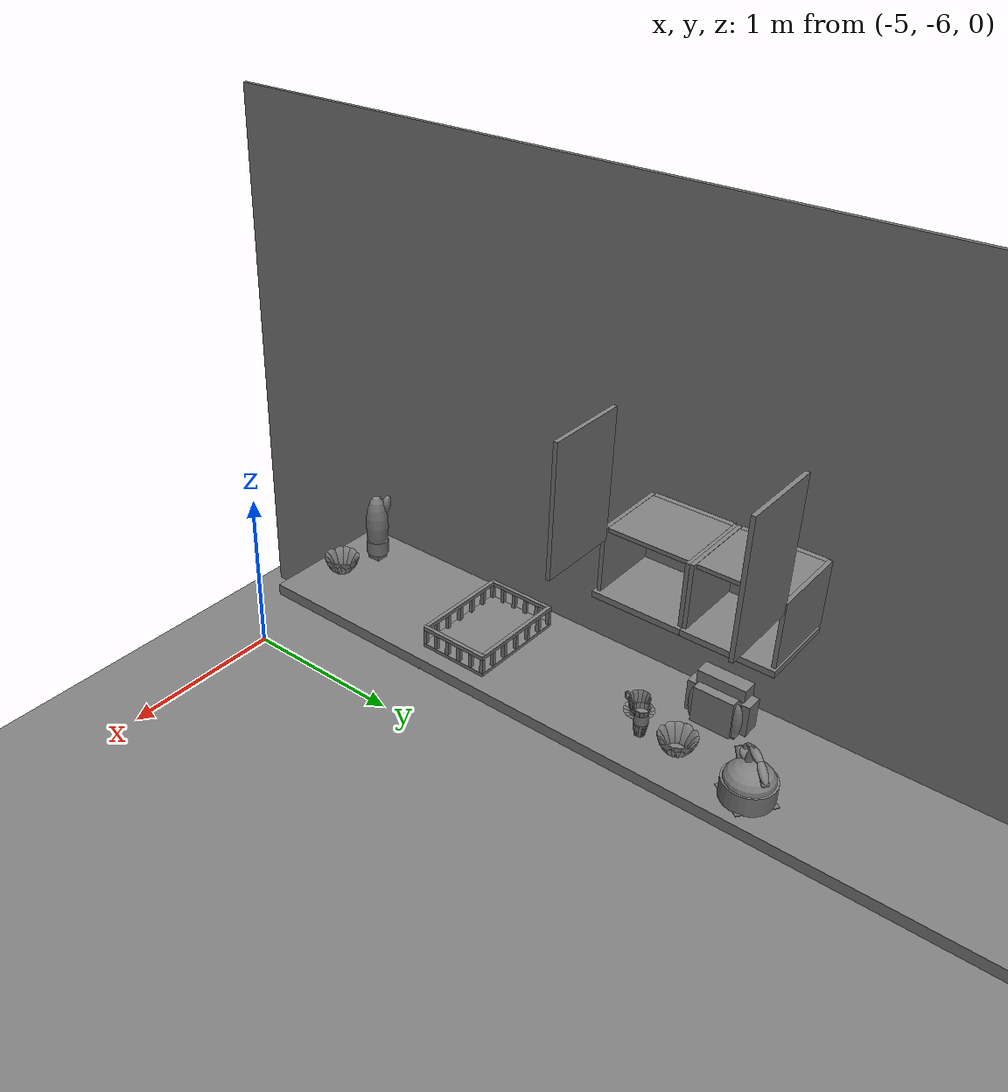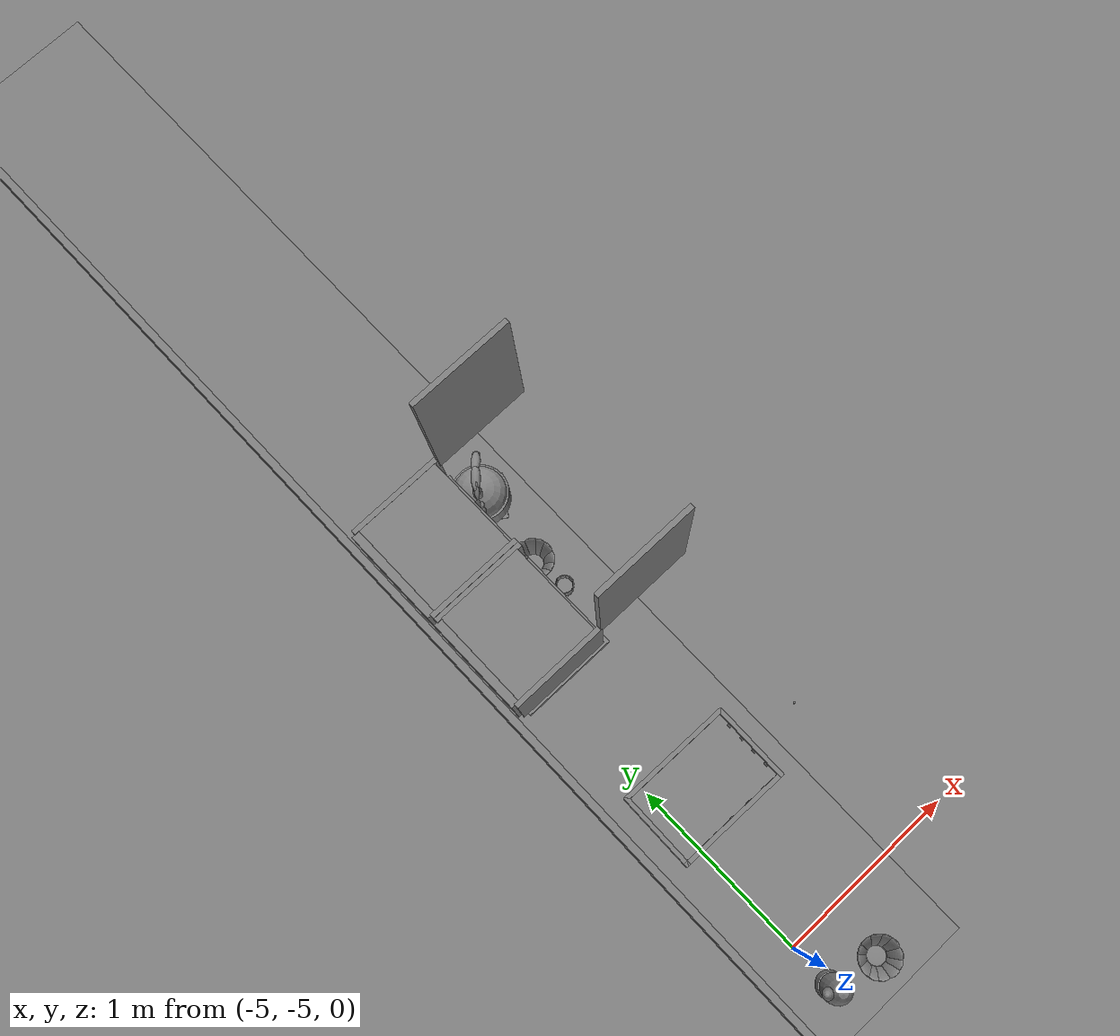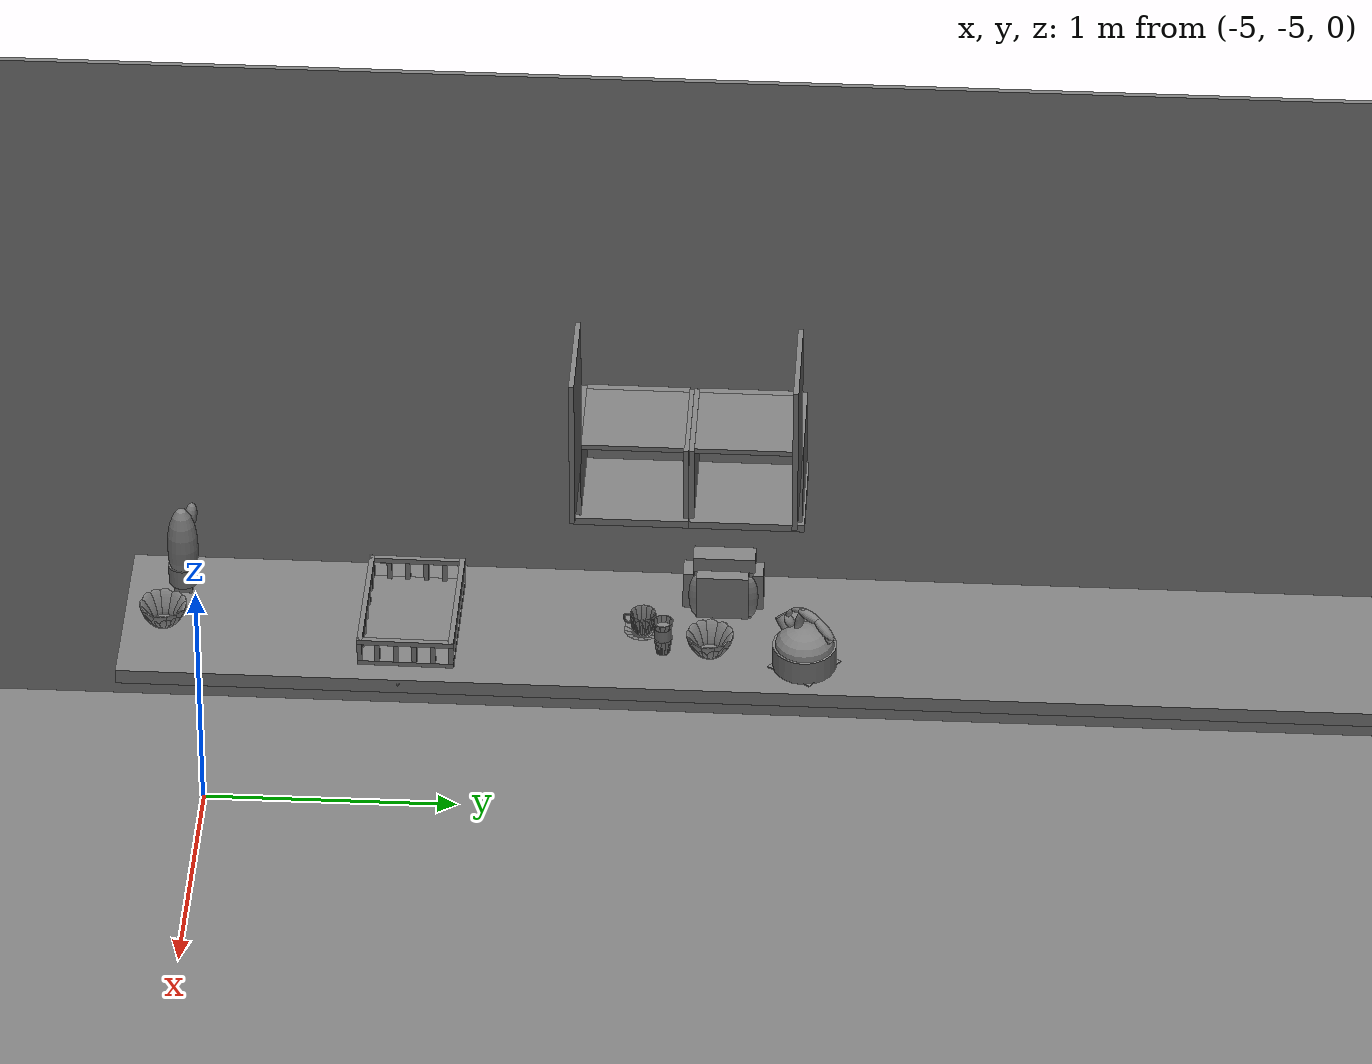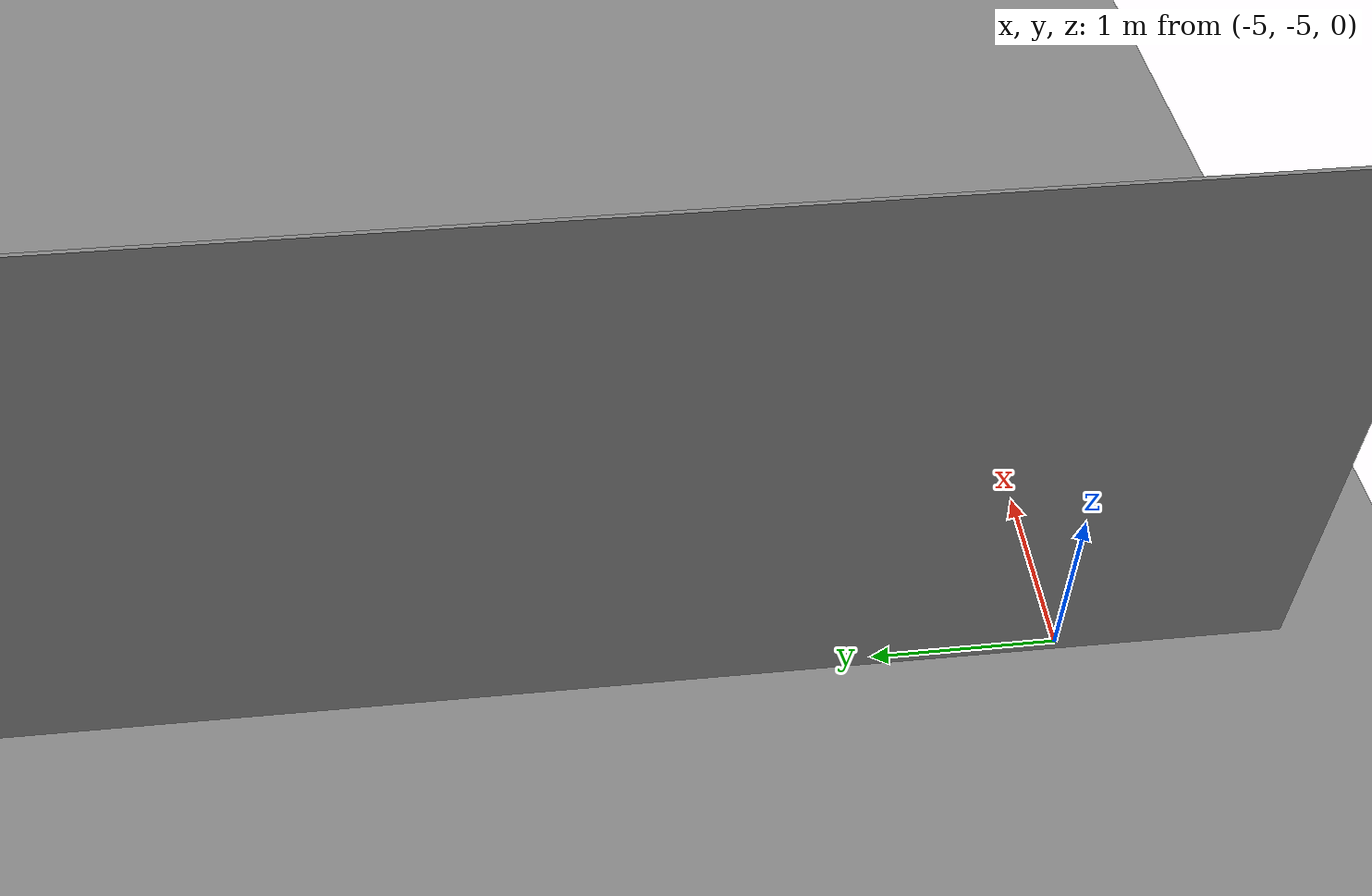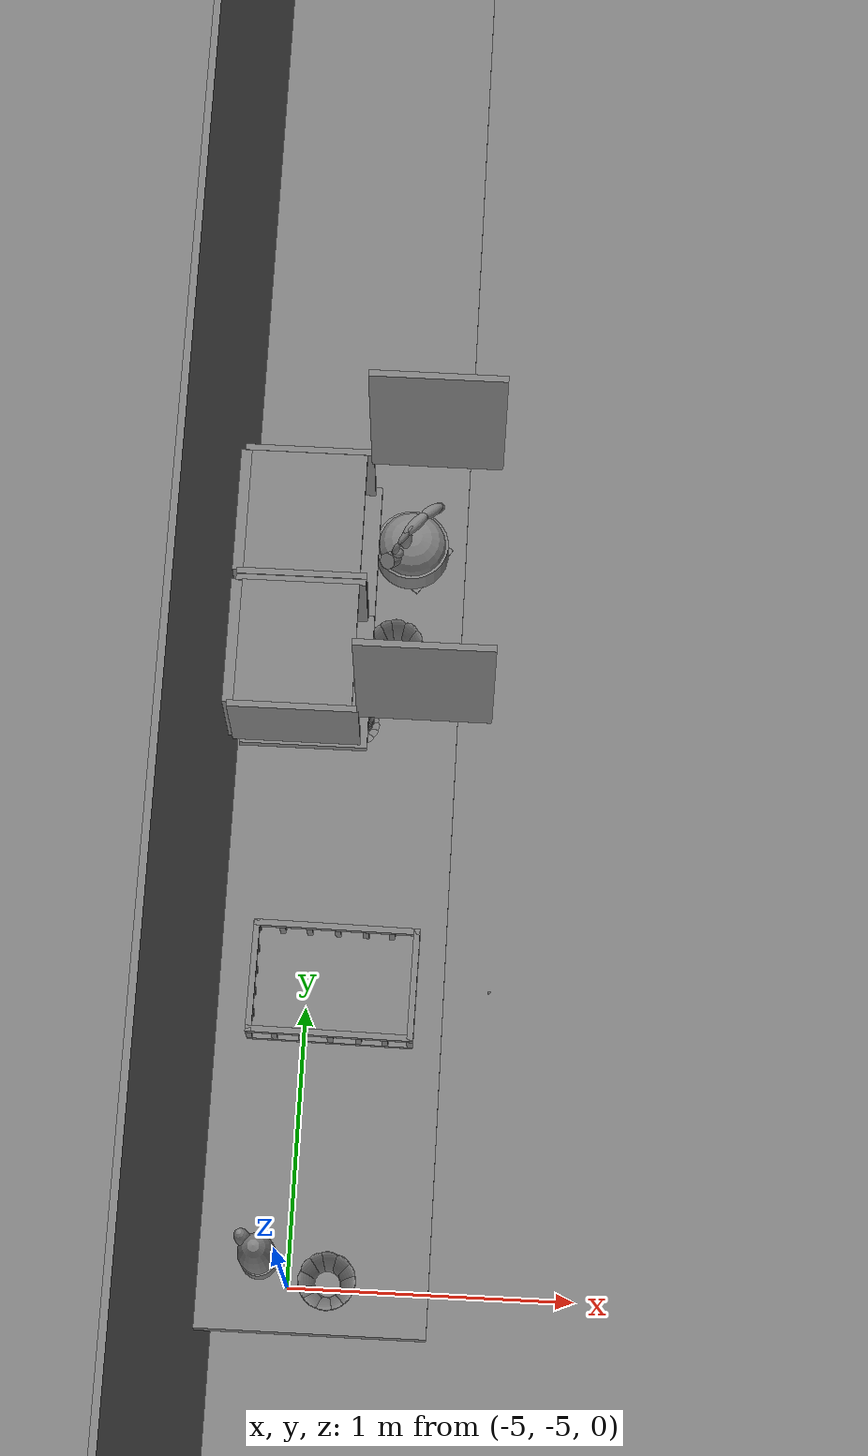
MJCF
<mujoco>
    <option gravity="0.000000000 0.000000000 -9.810000420" timestep="0.0049999999" integrator="implicitfast" density="9.8000002" viscosity="1.8000001e-05" noslip_iterations="10" iterations="100" sdf_iterations="50">
        <flag multiccd="disable"/>
    </option>
    <size memory="1000M"/>
    <compiler coordinate="local"/>
    <worldbody>
        <light cutoff="30" pos="0 1 1" dir="0 -1 -2"/>
        <light cutoff="30" pos="0 -1 1" dir="0 1 -2"/>
        <body pos="0.000000000 0.000000000 0.000000000" euler="0.000000000 0.000000000 0.000000000" name="Static Objcets_Static Objcets">
            <geom contype="1" conaffinity="1" density="1000" type="box" material="" rgba="0.500000000 0.500000000 0.500000000 1.000000000" solimp="0.899999976 0.949999988 0.001000000" friction="1.000000000 0.005000000 0.000100000" solref="0.020000000 1.000000000" margin="0" condim="3" group="0" pos="-5.189302921 -3.293644905 1.760152459" quat="0.707107067 0.707106471 0.000000000 0.000000000" size="0.025000000 0.159999996 0.200000003" name="Static Objcets_geom_37C9DB1D_205C_4135_B551_0E05F6CFD01A"/>
            <geom contype="1" conaffinity="1" density="1000" type="box" material="" rgba="0.500000000 0.500000000 0.500000000 1.000000000" solimp="0.899999976 0.949999988 0.001000000" friction="1.000000000 0.005000000 0.000100000" solref="0.020000000 1.000000000" margin="0" condim="3" group="0" pos="-4.999745846 -3.497932911 1.764780521" quat="0.707107067 0.707106471 0.000000000 0.000000000" size="0.200000003 0.159999996 0.010000000" name="Static Objcets_geom_DB503B25_8A2A_4DFB_9B6D_C88CA87CB224"/>
            <geom contype="1" conaffinity="1" density="1000" type="box" material="" rgba="0.500000000 0.500000000 0.500000000 1.000000000" solimp="0.899999976 0.949999988 0.001000000" friction="1.000000000 0.005000000 0.000100000" solref="0.020000000 1.000000000" margin="0" condim="3" group="0" pos="-4.979488373 -3.297635794 1.591412544" quat="0.707106829 0.707106709 0.000000000 0.000000000" size="0.200000003 0.015000000 0.219999999" name="Static Objcets_geom_B57428BA_48F9_4B58_82CF_3958ADAA4700"/>
            <geom contype="1" conaffinity="1" density="1000" type="box" material="" rgba="0.500000000 0.500000000 0.500000000 1.000000000" solimp="0.899999976 0.949999988 0.001000000" friction="1.000000000 0.005000000 0.000100000" solref="0.020000000 1.000000000" margin="0" condim="3" group="0" pos="-4.999745846 -3.087441683 1.763863802" quat="0.707107067 0.707106471 0.000000000 0.000000000" size="0.200000003 0.159999996 0.010000000" name="Static Objcets_geom_32B47D97_1C0A_4189_ACBA_E203634AE1D0"/>
            <geom contype="1" conaffinity="1" density="1000" type="box" material="" rgba="0.500000000 0.500000000 0.500000000 1.000000000" solimp="0.899999976 0.949999988 0.001000000" friction="1.000000000 0.005000000 0.000100000" solref="0.020000000 1.000000000" margin="0" condim="3" group="0" pos="-5.000125408 -3.294431210 1.913951039" quat="0.707107067 0.707106471 0.000000000 0.000000000" size="0.180000007 0.010000000 0.200000003" name="Static Objcets_geom_960F6845_78AB_45BD_9904_CCCE7A0354A7"/>
            <geom contype="1" conaffinity="1" density="1000" type="box" material="" rgba="0.500000000 0.500000000 0.500000000 1.000000000" solimp="0.899999976 0.949999988 0.001000000" friction="1.000000000 0.005000000 0.000100000" solref="0.020000000 1.000000000" margin="0" condim="3" group="0" pos="-4.873187065 -2.461376429 0.977675021" quat="0.707107067 0.707106471 0.000000000 0.000000000" size="0.370000005 0.029999999 2.799999952" name="Static Objcets_geom_5DF2FE1C_2772_4C6F_B440_850B4CF0B0CB"/>
            <geom contype="1" conaffinity="1" density="1000" type="box" material="" rgba="0.500000000 0.500000000 0.500000000 1.000000000" solimp="0.899999976 0.949999988 0.001000000" friction="1.000000000 0.005000000 0.000100000" solref="0.020000000 1.000000000" margin="0" condim="3" group="0" pos="-5.244853973 -2.375543594 1.820221663" quat="0.707107008 0.707106531 0.000000000 0.000000000" size="0.010000000 1.500000000 3.700000048" name="Static Objcets_geom_A5428AC7_BF09_447F_9ACF_F20EE92330A8"/>
            <geom contype="1" conaffinity="1" density="1000" type="box" material="" rgba="0.500000000 0.500000000 0.500000000 1.000000000" solimp="0.899999976 0.949999988 0.001000000" friction="1.000000000 0.005000000 0.000100000" solref="0.020000000 1.000000000" margin="0" condim="3" group="0" pos="-0.720102787 0.222944975 -1.102830648" quat="0.000000954 1.000000000 0.000000000 0.000000000" size="8.000000000 8.000000000 0.010000000" name="Static Objcets_geom_420C86CA_A5C4_4DA9_8522_A19B935AEE6B"/>
            <geom contype="1" conaffinity="1" density="1000" type="box" material="" rgba="0.500000000 0.500000000 0.500000000 1.000000000" solimp="0.899999976 0.949999988 0.001000000" friction="1.000000000 0.005000000 0.000100000" solref="0.020000000 1.000000000" margin="0" condim="3" group="0" pos="-4.999745846 -2.653569937 1.764779806" quat="0.707107067 0.707106471 0.000000000 0.000000000" size="0.200000003 0.159999996 0.010000000" name="Static Objcets_geom_A94B13EC_DE08_49A5_A25F_3AAA1D3AF4B6"/>
            <geom contype="1" conaffinity="1" density="1000" type="box" material="" rgba="0.500000000 0.500000000 0.500000000 1.000000000" solimp="0.899999976 0.949999988 0.001000000" friction="1.000000000 0.005000000 0.000100000" solref="0.020000000 1.000000000" margin="0" condim="3" group="0" pos="-5.000125408 -2.861802340 1.913950682" quat="0.707107067 0.707106471 0.000000000 0.000000000" size="0.180000007 0.010000000 0.200000003" name="Static Objcets_geom_7AD50E43_05A5_41B6_93C8_F5B95109F5A1"/>
            <geom contype="1" conaffinity="1" density="1000" type="box" material="" rgba="0.500000000 0.500000000 0.500000000 1.000000000" solimp="0.899999976 0.949999988 0.001000000" friction="1.000000000 0.005000000 0.000100000" solref="0.020000000 1.000000000" margin="0" condim="3" group="0" pos="-5.189302921 -2.861564636 1.760152102" quat="0.707107067 0.707106471 0.000000000 0.000000000" size="0.025000000 0.159999996 0.200000003" name="Static Objcets_geom_1D59441B_061E_4FDD_AF59_8840EE514955"/>
            <geom contype="1" conaffinity="1" density="1000" type="box" material="" rgba="0.500000000 0.500000000 0.500000000 1.000000000" solimp="0.899999976 0.949999988 0.001000000" friction="1.000000000 0.005000000 0.000100000" solref="0.020000000 1.000000000" margin="0" condim="3" group="0" pos="-4.979488373 -2.855390549 1.591412187" quat="0.707106709 0.707106769 0.000000000 0.000000000" size="0.200000003 0.015000000 0.219999999" name="Static Objcets_geom_DC32BE04_C8BA_4F6C_BF46_5CA6532F3C29"/>
            <geom contype="1" conaffinity="1" density="1000" type="box" material="" rgba="0.500000000 0.500000000 0.500000000 1.000000000" solimp="0.899999976 0.949999988 0.001000000" friction="1.000000000 0.005000000 0.000100000" solref="0.020000000 1.000000000" margin="0" condim="3" group="0" pos="-4.999745846 -3.066934109 1.765979409" quat="0.707107067 0.707106471 0.000000000 0.000000000" size="0.200000003 0.159999996 0.010000000" name="Static Objcets_geom_CA4784C9_4319_4085_9996_FD62E3559159"/>
        </body>
        <body pos="1000.000000000 1000.000000000 1.000000000" euler="0.000000000 0.000000000 0.000000000" name="openloong_gripper_2f85_fix_base_usda_jar_01">
            <geom contype="1" conaffinity="1" density="1000" type="box" material="" rgba="0.500000000 0.500000000 0.500000000 1.000000000" solimp="0.899999976 0.949999988 0.001000000" friction="1.000000000 0.005000000 0.000100000" solref="0.020000000 1.000000000" margin="0" condim="3" group="0" pos="0.000000000 0.000000000 0.006158113" quat="1.000000000 0.000000000 0.000000000 0.000000000" size="0.020000000 0.020000000 0.005000000" name="openloong_gripper_2f85_fix_base_usda_geom_F57A3BDA_FBAC_4A1A_951F_D8F755E258C1"/>
            <geom contype="1" conaffinity="1" density="1000" type="cylinder" material="" rgba="0.500000000 0.500000000 0.500000000 1.000000000" solimp="0.899999976 0.949999988 0.001000000" friction="1.000000000 0.005000000 0.000100000" solref="0.020000000 1.000000000" margin="0" condim="3" group="0" pos="0.000000000 0.000000000 0.062744498" quat="1.000000000 0.000000000 0.000000000 0.000000000" size="0.041000001 0.052999999 1.000000000" name="openloong_gripper_2f85_fix_base_usda_geom_C2BA6315_1B8B_4203_B590_E56E1C82C5FE"/>
            <geom contype="1" conaffinity="1" density="1000" type="ellipsoid" material="" rgba="0.500000000 0.500000000 0.500000000 1.000000000" solimp="0.899999976 0.949999988 0.001000000" friction="1.000000000 0.005000000 0.000100000" solref="0.020000000 1.000000000" margin="0" condim="3" group="0" pos="0.000000000 0.000000000 0.122252703" quat="1.000000000 0.000000000 0.000000000 0.000000000" size="0.035999998 0.035999998 0.010000000" name="openloong_gripper_2f85_fix_base_usda_geom_82DD9CAD_04B1_41C1_86AE_E2E5D650D180"/>
            <geom contype="1" conaffinity="1" density="1000" type="cylinder" material="" rgba="0.500000000 0.500000000 0.500000000 1.000000000" solimp="0.899999976 0.949999988 0.001000000" friction="1.000000000 0.005000000 0.000100000" solref="0.020000000 1.000000000" margin="0" condim="3" group="0" pos="0.000000000 0.000000000 0.015747190" quat="1.000000000 0.000000000 0.000000000 0.000000000" size="0.035000000 0.010000000 1.000000000" name="openloong_gripper_2f85_fix_base_usda_geom_5465A950_55E1_4A52_A0A9_7B4CD0DB728C"/>
            <geom contype="1" conaffinity="1" density="1000" type="ellipsoid" material="" rgba="0.500000000 0.500000000 0.500000000 1.000000000" solimp="0.899999976 0.949999988 0.001000000" friction="1.000000000 0.005000000 0.000100000" solref="0.020000000 1.000000000" margin="0" condim="3" group="0" pos="0.000000000 0.000000000 0.115815401" quat="1.000000000 0.000000000 0.000000000 0.000000000" size="0.039999999 0.039999999 0.010000000" name="openloong_gripper_2f85_fix_base_usda_geom_E7699EF8_655C_464C_A6EE_A3E043E78332"/>
            <geom contype="1" conaffinity="1" density="1000" type="cylinder" material="" rgba="0.500000000 0.500000000 0.500000000 1.000000000" solimp="0.899999976 0.949999988 0.001000000" friction="1.000000000 0.005000000 0.000100000" solref="0.020000000 1.000000000" margin="0" condim="3" group="0" pos="0.000000000 0.000000000 0.133183479" quat="1.000000000 0.000000000 0.000000000 0.000000000" size="0.037999999 0.006500000 1.000000000" name="openloong_gripper_2f85_fix_base_usda_geom_282B1DA9_C0CD_4AC1_A1ED_EE08E42334FD"/>
            <freejoint name="openloong_gripper_2f85_fix_base_usda_jar_01_joint"/>
            <site size="0.005000000 0.005000000 0.005000000" rgba="0.500000000 0.500000000 0.500000000 1.000000000" pos="0.000000000 0.000000000 0.000000000" quat="1.000000000 0.000000000 0.000000000 0.000000000" group="0" type="sphere" name="openloong_gripper_2f85_fix_base_usda_jar_01site"/>
        </body>
        <body pos="1000.000000000 1000.000000000 1.000000000" euler="0.000000000 0.000000000 0.000000000" name="openloong_gripper_2f85_fix_base_usda_salt">
            <geom contype="1" conaffinity="1" density="1000" type="box" material="" rgba="0.500000000 0.500000000 0.500000000 1.000000000" solimp="0.899999976 0.949999988 0.001000000" friction="1.000000000 0.005000000 0.000100000" solref="0.020000000 1.000000000" margin="0" condim="3" group="0" pos="0.000305176 0.000000000 0.084862232" quat="1.000000000 0.000000000 0.000000000 0.000000000" size="0.048999999 0.018999999 0.005000000" name="openloong_gripper_2f85_fix_base_usda_geom_6CA79C92_A6EA_4C13_9BF6_E4B861FD3ED1"/>
            <geom contype="1" conaffinity="1" density="1000" type="box" material="" rgba="0.500000000 0.500000000 0.500000000 1.000000000" solimp="0.899999976 0.949999988 0.001000000" friction="1.000000000 0.005000000 0.000100000" solref="0.020000000 1.000000000" margin="0" condim="3" group="0" pos="0.000305176 0.000000000 0.104564309" quat="1.000000000 0.000000000 0.000000000 0.000000000" size="0.052000001 0.014000000 0.005000000" name="openloong_gripper_2f85_fix_base_usda_geom_BF224F0A_D2B8_4705_BCE5_8F94E5C568ED"/>
            <geom contype="1" conaffinity="1" density="1000" type="box" material="" rgba="0.500000000 0.500000000 0.500000000 1.000000000" solimp="0.899999976 0.949999988 0.001000000" friction="1.000000000 0.005000000 0.000100000" solref="0.020000000 1.000000000" margin="0" condim="3" group="0" pos="0.000305176 0.000000000 0.114487171" quat="1.000000000 0.000000000 0.000000000 0.000000000" size="0.054000001 0.011500000 0.005000000" name="openloong_gripper_2f85_fix_base_usda_geom_3D8E8F02_E0D1_4F68_B873_F378DFB0729B"/>
            <geom contype="1" conaffinity="1" density="1000" type="box" material="" rgba="0.500000000 0.500000000 0.500000000 1.000000000" solimp="0.899999976 0.949999988 0.001000000" friction="1.000000000 0.005000000 0.000100000" solref="0.020000000 1.000000000" margin="0" condim="3" group="0" pos="0.000305176 0.000000000 0.075103164" quat="1.000000000 0.000000000 0.000000000 0.000000000" size="0.048000000 0.020000000 0.005000000" name="openloong_gripper_2f85_fix_base_usda_geom_882D8885_3F4B_4F33_9FC6_C61CAB167AC3"/>
            <geom contype="1" conaffinity="1" density="1000" type="box" material="" rgba="0.500000000 0.500000000 0.500000000 1.000000000" solimp="0.899999976 0.949999988 0.001000000" friction="1.000000000 0.005000000 0.000100000" solref="0.020000000 1.000000000" margin="0" condim="3" group="0" pos="0.000305176 0.000000000 0.134892464" quat="1.000000000 0.000000000 0.000000000 0.000000000" size="0.057000000 0.007000000 0.005000000" name="openloong_gripper_2f85_fix_base_usda_geom_AD90801E_9A09_4ADD_9E3E_0179B4950268"/>
            <geom contype="1" conaffinity="1" density="1000" type="box" material="" rgba="0.500000000 0.500000000 0.500000000 1.000000000" solimp="0.899999976 0.949999988 0.001000000" friction="1.000000000 0.005000000 0.000100000" solref="0.020000000 1.000000000" margin="0" condim="3" group="0" pos="0.000305176 0.000000000 0.094920278" quat="1.000000000 0.000000000 0.000000000 0.000000000" size="0.050000001 0.017000001 0.005000000" name="openloong_gripper_2f85_fix_base_usda_geom_F2131ADF_6963_4A45_9D2D_94845B50E556"/>
            <geom contype="1" conaffinity="1" density="1000" type="box" material="" rgba="0.500000000 0.500000000 0.500000000 1.000000000" solimp="0.899999976 0.949999988 0.001000000" friction="1.000000000 0.005000000 0.000100000" solref="0.020000000 1.000000000" margin="0" condim="3" group="0" pos="0.000305176 0.000000000 0.065204859" quat="1.000000000 0.000000000 0.000000000 0.000000000" size="0.045000002 0.021000000 0.005000000" name="openloong_gripper_2f85_fix_base_usda_geom_283F19BB_7CE4_4052_83EF_EA818D6B4616"/>
            <geom contype="1" conaffinity="1" density="1000" type="box" material="" rgba="0.500000000 0.500000000 0.500000000 1.000000000" solimp="0.899999976 0.949999988 0.001000000" friction="1.000000000 0.005000000 0.000100000" solref="0.020000000 1.000000000" margin="0" condim="3" group="0" pos="0.000305176 0.000000000 0.144135714" quat="1.000000000 0.000000000 0.000000000 0.000000000" size="0.059000000 0.005000000 0.004000000" name="openloong_gripper_2f85_fix_base_usda_geom_8012FBEB_47AD_4CF2_940B_438B612B9C04"/>
            <geom contype="1" conaffinity="1" density="1000" type="box" material="" rgba="0.500000000 0.500000000 0.500000000 1.000000000" solimp="0.899999976 0.949999988 0.001000000" friction="1.000000000 0.005000000 0.000100000" solref="0.020000000 1.000000000" margin="0" condim="3" group="0" pos="0.000000000 0.000000000 0.031593561" quat="1.000000000 0.000000000 0.000000000 0.000000000" size="0.041999999 0.024000000 0.029999999" name="openloong_gripper_2f85_fix_base_usda_geom_447CDE90_B368_4717_BFA9_25BC94C60805"/>
            <geom contype="1" conaffinity="1" density="1000" type="box" material="" rgba="0.500000000 0.500000000 0.500000000 1.000000000" solimp="0.899999976 0.949999988 0.001000000" friction="1.000000000 0.005000000 0.000100000" solref="0.020000000 1.000000000" margin="0" condim="3" group="0" pos="0.000305176 0.000000000 0.124608755" quat="1.000000000 0.000000000 0.000000000 0.000000000" size="0.055000000 0.008000000 0.005000000" name="openloong_gripper_2f85_fix_base_usda_geom_75C9223D_CA83_41AE_A204_65F21DE20C52"/>
            <freejoint name="openloong_gripper_2f85_fix_base_usda_salt_joint"/>
            <site size="0.005000000 0.005000000 0.005000000" rgba="0.500000000 0.500000000 0.500000000 1.000000000" pos="0.000000000 0.000000000 0.000000000" quat="1.000000000 0.000000000 0.000000000 0.000000000" group="0" type="sphere" name="openloong_gripper_2f85_fix_base_usda_saltsite"/>
        </body>
        <body pos="1000.000000000 1000.000000000 1.000000000" euler="0.000000000 0.000000000 0.000000000" name="openloong_gripper_2f85_fix_base_usda_bow_yellow_kps">
            <geom contype="1" conaffinity="1" density="1000" type="ellipsoid" material="" rgba="0.500000000 0.500000000 0.500000000 1.000000000" solimp="0.899999976 0.949999988 0.001000000" friction="1.000000000 0.005000000 0.000100000" solref="0.020000000 1.000000000" margin="0" condim="3" group="0" pos="-0.052185059 0.040283203 0.044118762" quat="0.919264615 -0.076883033 -0.225593656 -0.313287765" size="0.010000000 0.039999999 0.052000001" name="openloong_gripper_2f85_fix_base_usda_geom_52EFCC73_05E5_48DF_8F9E_9F6134F6309D"/>
            <geom contype="1" conaffinity="1" density="1000" type="ellipsoid" material="" rgba="0.500000000 0.500000000 0.500000000 1.000000000" solimp="0.899999976 0.949999988 0.001000000" friction="1.000000000 0.005000000 0.000100000" solref="0.020000000 1.000000000" margin="0" condim="3" group="0" pos="-0.000061035 0.065979004 0.044118762" quat="0.687598765 -0.168314874 -0.168741167 -0.685860336" size="0.010000000 0.039999999 0.052000001" name="openloong_gripper_2f85_fix_base_usda_geom_8CD0F94E_44BA_45B9_85EA_6AF1B3198D52"/>
            <geom contype="1" conaffinity="1" density="1000" type="box" material="" rgba="0.500000000 0.500000000 0.500000000 1.000000000" solimp="0.899999976 0.949999988 0.001000000" friction="1.000000000 0.005000000 0.000100000" solref="0.020000000 1.000000000" margin="0" condim="3" group="0" pos="0.000061035 0.000000000 -0.002001643" quat="1.000000000 0.000000000 0.000000000 0.000000000" size="0.029999999 0.029999999 0.002000000" name="openloong_gripper_2f85_fix_base_usda_geom_879C95D5_3879_4F42_8506_D6589F4F087E"/>
            <geom contype="1" conaffinity="1" density="1000" type="ellipsoid" material="" rgba="0.500000000 0.500000000 0.500000000 1.000000000" solimp="0.899999976 0.949999988 0.001000000" friction="1.000000000 0.005000000 0.000100000" solref="0.020000000 1.000000000" margin="0" condim="3" group="0" pos="0.029418945 -0.059082031 0.044118762" quat="0.825555861 0.125530601 0.202597082 -0.511521280" size="0.010000000 0.039999999 0.052000001" name="openloong_gripper_2f85_fix_base_usda_geom_52ED2E8B_158F_491B_AD75_7CE69F4B7AB7"/>
            <geom contype="1" conaffinity="1" density="1000" type="ellipsoid" material="" rgba="0.500000000 0.500000000 0.500000000 1.000000000" solimp="0.899999976 0.949999988 0.001000000" friction="1.000000000 0.005000000 0.000100000" solref="0.020000000 1.000000000" margin="0" condim="3" group="0" pos="0.000244141 -0.065979004 0.044118762" quat="0.687598765 0.168314651 0.168741375 -0.685860336" size="0.010000000 0.039999999 0.052000001" name="openloong_gripper_2f85_fix_base_usda_geom_6B3C9337_7BF1_48BE_9824_24931BEBA9C3"/>
            <geom contype="1" conaffinity="1" density="1000" type="ellipsoid" material="" rgba="0.500000000 0.500000000 0.500000000 1.000000000" solimp="0.899999976 0.949999988 0.001000000" friction="1.000000000 0.005000000 0.000100000" solref="0.020000000 1.000000000" margin="0" condim="3" group="0" pos="0.000061035 0.000000000 0.000446677" quat="1.000000000 0.000000000 0.000000000 0.000000000" size="0.039999999 0.039999999 0.002000000" name="openloong_gripper_2f85_fix_base_usda_geom_7060FE88_4E8E_4F0C_A9DD_2CE5EF8F7D70"/>
            <geom contype="1" conaffinity="1" density="1000" type="ellipsoid" material="" rgba="0.500000000 0.500000000 0.500000000 1.000000000" solimp="0.899999976 0.949999988 0.001000000" friction="1.000000000 0.005000000 0.000100000" solref="0.020000000 1.000000000" margin="0" condim="3" group="0" pos="0.059082031 0.029541016 0.044118762" quat="0.223252773 -0.231952220 -0.054787423 -0.945174456" size="0.010000000 0.039999999 0.052000001" name="openloong_gripper_2f85_fix_base_usda_geom_239F2073_6A0E_4CBE_8164_E54683C06B44"/>
            <geom contype="1" conaffinity="1" density="1000" type="ellipsoid" material="" rgba="0.500000000 0.500000000 0.500000000 1.000000000" solimp="0.899999976 0.949999988 0.001000000" friction="1.000000000 0.005000000 0.000100000" solref="0.020000000 1.000000000" margin="0" condim="3" group="0" pos="0.000061035 0.000000000 0.007335305" quat="1.000000000 0.000000000 0.000000000 0.000000000" size="0.039999999 0.039999999 0.002000000" name="openloong_gripper_2f85_fix_base_usda_geom_882D70EA_6E0E_4408_B28A_2AFCAD036E7F"/>
            <geom contype="1" conaffinity="1" density="1000" type="ellipsoid" material="" rgba="0.500000000 0.500000000 0.500000000 1.000000000" solimp="0.899999976 0.949999988 0.001000000" friction="1.000000000 0.005000000 0.000100000" solref="0.020000000 1.000000000" margin="0" condim="3" group="0" pos="-0.029296875 0.059082031 0.044118762" quat="0.825555861 -0.125530809 -0.202596918 -0.511521280" size="0.010000000 0.039999999 0.052000001" name="openloong_gripper_2f85_fix_base_usda_geom_AA02DB54_44E6_462E_82A1_BA33E362C44D"/>
            <geom contype="1" conaffinity="1" density="1000" type="ellipsoid" material="" rgba="0.500000000 0.500000000 0.500000000 1.000000000" solimp="0.899999976 0.949999988 0.001000000" friction="1.000000000 0.005000000 0.000100000" solref="0.020000000 1.000000000" margin="0" condim="3" group="0" pos="0.040222168 0.052368164 0.044118762" quat="0.429593176 -0.213750049 -0.105424821 -0.871002972" size="0.010000000 0.039999999 0.052000001" name="openloong_gripper_2f85_fix_base_usda_geom_C6A4AE92_4550_478B_86DE_7FCAC1415CE3"/>
            <geom contype="1" conaffinity="1" density="1000" type="ellipsoid" material="" rgba="0.500000000 0.500000000 0.500000000 1.000000000" solimp="0.899999976 0.949999988 0.001000000" friction="1.000000000 0.005000000 0.000100000" solref="0.020000000 1.000000000" margin="0" condim="3" group="0" pos="0.066040039 0.000000000 0.044118762" quat="0.971183062 -0.000000156 0.238334835 0.000000030" size="0.010000000 0.039999999 0.052000001" name="openloong_gripper_2f85_fix_base_usda_geom_1B5C1A26_D72D_4FA1_8E3C_1FBAE9D7672C"/>
            <geom contype="1" conaffinity="1" density="1000" type="ellipsoid" material="" rgba="0.500000000 0.500000000 0.500000000 1.000000000" solimp="0.899999976 0.949999988 0.001000000" friction="1.000000000 0.005000000 0.000100000" solref="0.020000000 1.000000000" margin="0" condim="3" group="0" pos="0.052307129 -0.040283203 0.044118762" quat="0.919264674 0.076882750 0.225593731 -0.313287705" size="0.010000000 0.039999999 0.052000001" name="openloong_gripper_2f85_fix_base_usda_geom_E131D3FE_088E_4A7F_8661_063EA1F3B1CB"/>
            <geom contype="1" conaffinity="1" density="1000" type="ellipsoid" material="" rgba="0.500000000 0.500000000 0.500000000 1.000000000" solimp="0.899999976 0.949999988 0.001000000" friction="1.000000000 0.005000000 0.000100000" solref="0.020000000 1.000000000" margin="0" condim="3" group="0" pos="-0.065917969 0.000000000 0.044118762" quat="0.971183062 -0.000000142 -0.238334835 0.000000030" size="0.010000000 0.039999999 0.052000001" name="openloong_gripper_2f85_fix_base_usda_geom_CC4A0764_1E49_4713_9399_DC63C8A1E4AB"/>
            <geom contype="1" conaffinity="1" density="1000" type="ellipsoid" material="" rgba="0.500000000 0.500000000 0.500000000 1.000000000" solimp="0.899999976 0.949999988 0.001000000" friction="1.000000000 0.005000000 0.000100000" solref="0.020000000 1.000000000" margin="0" condim="3" group="0" pos="-0.058898926 -0.029541016 0.044118762" quat="0.223252758 0.231952101 0.054787733 -0.945174575" size="0.010000000 0.039999999 0.052000001" name="openloong_gripper_2f85_fix_base_usda_geom_F9BBC3E7_1A25_470C_81D2_7E076FB26082"/>
            <geom contype="1" conaffinity="1" density="1000" type="ellipsoid" material="" rgba="0.500000000 0.500000000 0.500000000 1.000000000" solimp="0.899999976 0.949999988 0.001000000" friction="1.000000000 0.005000000 0.000100000" solref="0.020000000 1.000000000" margin="0" condim="3" group="0" pos="-0.040100098 -0.052368164 0.044118762" quat="0.429593235 0.213749886 0.105425082 -0.871003032" size="0.010000000 0.039999999 0.052000001" name="openloong_gripper_2f85_fix_base_usda_geom_15AA8EA3_02B1_4E8D_88D5_ED160EB2F42C"/>
            <freejoint name="openloong_gripper_2f85_fix_base_usda_bow_yellow_kps_joint"/>
            <site size="0.005000000 0.005000000 0.005000000" rgba="0.500000000 0.500000000 0.500000000 1.000000000" pos="0.000000000 0.000000000 0.000000000" quat="0.999961913 0.008726534 0.000000000 0.000000000" group="0" type="sphere" name="openloong_gripper_2f85_fix_base_usda_bow_yellow_kps"/>
        </body>
        <body pos="-4.004791737 -4.258792400 1.726932287" euler="-168.696533203 8.342100143 115.107803345" mocap="true" name="spotlight2_SpotLight"/>
        <body pos="-4.145106792 -4.212274075 1.789211035" euler="76.195930481 24.571821213 -150.320816040" mocap="true" name="spotlight5_SpotLight"/>
        <body pos="-4.178371429 -4.117174149 1.852068663" euler="115.939613342 81.077026367 58.116329193" mocap="true" name="spotlight6_SpotLight"/>
        <body pos="1000.000000000 1000.000000000 1.000000000" euler="0.000000000 0.000000000 0.000000000" name="openloong_gripper_2f85_fix_base_usda_coffeecup_white_kps">
            <geom contype="1" conaffinity="1" density="1000" type="capsule" material="" rgba="0.500000000 0.500000000 0.500000000 1.000000000" solimp="0.899999976 0.949999988 0.001000000" friction="1.000000000 0.005000000 0.000100000" solref="0.020000000 1.000000000" margin="0" condim="3" group="0" pos="-0.000854492 -0.065795898 0.050029993" quat="0.343559504 -0.613204718 0.626912475 0.336047262" size="0.004000000 0.005000000 1.000000000" name="openloong_gripper_2f85_fix_base_usda_geom_A28686AF_B410_47FE_9786_671E33D6F818"/>
            <geom contype="1" conaffinity="1" density="1000" type="ellipsoid" material="" rgba="0.500000000 0.500000000 0.500000000 1.000000000" solimp="0.899999976 0.949999988 0.001000000" friction="1.000000000 0.005000000 0.000100000" solref="0.020000000 1.000000000" margin="0" condim="3" group="0" pos="-0.000793457 -0.038452148 0.048040152" quat="0.711656272 0.066323131 -0.067805752 0.696095467" size="0.005000000 0.029999999 0.048999999" name="openloong_gripper_2f85_fix_base_usda_geom_49E21DD8_1D11_43C4_8745_D5CA8E6E7265"/>
            <geom contype="1" conaffinity="1" density="1000" type="ellipsoid" material="" rgba="0.500000000 0.500000000 0.500000000 1.000000000" solimp="0.899999976 0.949999988 0.001000000" friction="1.000000000 0.005000000 0.000100000" solref="0.020000000 1.000000000" margin="0" condim="3" group="0" pos="0.037719727 -0.001892090 0.048040152" quat="0.995387912 0.001371633 0.094835162 -0.014391154" size="0.005000000 0.029999999 0.048999999" name="openloong_gripper_2f85_fix_base_usda_geom_03B6CFC7_988E_409D_9E34_C2967C6E7A41"/>
            <geom contype="1" conaffinity="1" density="1000" type="ellipsoid" material="" rgba="0.500000000 0.500000000 0.500000000 1.000000000" solimp="0.899999976 0.949999988 0.001000000" friction="1.000000000 0.005000000 0.000100000" solref="0.020000000 1.000000000" margin="0" condim="3" group="0" pos="0.033996582 0.015502930 0.048040152" quat="0.970659733 -0.021051638 0.092478797 0.220962167" size="0.005000000 0.029999999 0.048999999" name="openloong_gripper_2f85_fix_base_usda_geom_1BDB6F12_13D6_4C9B_B6F2_D0B01D108FED"/>
            <geom contype="1" conaffinity="1" density="1000" type="box" material="" rgba="0.500000000 0.500000000 0.500000000 1.000000000" solimp="0.899999976 0.949999988 0.001000000" friction="1.000000000 0.005000000 0.000100000" solref="0.020000000 1.000000000" margin="0" condim="3" group="0" pos="0.000793457 -0.000183105 0.000156164" quat="0.714879215 0.000000000 0.000000000 0.699247897" size="0.020000000 0.020000000 0.002000000" name="openloong_gripper_2f85_fix_base_usda_geom_3B0780B6_0818_43CA_A125_DB4838AEF0FF"/>
            <geom contype="1" conaffinity="1" density="1000" type="ellipsoid" material="" rgba="0.500000000 0.500000000 0.500000000 1.000000000" solimp="0.899999976 0.949999988 0.001000000" friction="1.000000000 0.005000000 0.000100000" solref="0.020000000 1.000000000" margin="0" condim="3" group="0" pos="-0.019409180 -0.033081055 0.048040152" quat="0.866879702 0.046630561 -0.082595348 0.489411235" size="0.005000000 0.029999999 0.048999999" name="openloong_gripper_2f85_fix_base_usda_geom_E1EBEA1C_5151_42D8_BC27_EA9A743030C3"/>
            <geom contype="1" conaffinity="1" density="1000" type="ellipsoid" material="" rgba="0.500000000 0.500000000 0.500000000 1.000000000" solimp="0.899999976 0.949999988 0.001000000" friction="1.000000000 0.005000000 0.000100000" solref="0.020000000 1.000000000" margin="0" condim="3" group="0" pos="-0.016052246 0.033264160 0.048040152" quat="0.840792537 -0.050782297 -0.080109790 -0.532983541" size="0.005000000 0.029999999 0.048999999" name="openloong_gripper_2f85_fix_base_usda_geom_3313F2F6_F04D_483D_AE71_D6288862356E"/>
            <geom contype="1" conaffinity="1" density="1000" type="capsule" material="" rgba="0.500000000 0.500000000 0.500000000 1.000000000" solimp="0.899999976 0.949999988 0.001000000" friction="1.000000000 0.005000000 0.000100000" solref="0.020000000 1.000000000" margin="0" condim="3" group="0" pos="-0.000549316 -0.053527832 0.046825886" quat="0.505496025 -0.494442940 0.505495846 0.494442940" size="0.004000000 0.005000000 1.000000000" name="openloong_gripper_2f85_fix_base_usda_geom_99B37069_E5D3_471F_8BB5_C81C9F913186"/>
            <geom contype="1" conaffinity="1" density="1000" type="ellipsoid" material="" rgba="0.500000000 0.500000000 0.500000000 1.000000000" solimp="0.899999976 0.949999988 0.001000000" friction="1.000000000 0.005000000 0.000100000" solref="0.020000000 1.000000000" margin="0" condim="3" group="0" pos="-0.032104492 0.018920898 0.048040152" quat="0.958129764 -0.025742561 -0.091288343 -0.270168930" size="0.005000000 0.029999999 0.048999999" name="openloong_gripper_2f85_fix_base_usda_geom_6AF33BEC_6010_4B56_B610_DEB728E072D6"/>
            <geom contype="1" conaffinity="1" density="1000" type="ellipsoid" material="" rgba="0.500000000 0.500000000 0.500000000 1.000000000" solimp="0.899999976 0.949999988 0.001000000" friction="1.000000000 0.005000000 0.000100000" solref="0.020000000 1.000000000" margin="0" condim="3" group="0" pos="-0.037597656 0.000305176 0.048040152" quat="0.995387554 -0.001371440 -0.094839431 -0.014389008" size="0.005000000 0.029999999 0.048999999" name="openloong_gripper_2f85_fix_base_usda_geom_E6C69A84_5954_48B5_93B3_C6ADCB601D8A"/>
            <geom contype="1" conaffinity="1" density="1000" type="capsule" material="" rgba="0.500000000 0.500000000 0.500000000 1.000000000" solimp="0.899999976 0.949999988 0.001000000" friction="1.000000000 0.005000000 0.000100000" solref="0.020000000 1.000000000" margin="0" condim="3" group="0" pos="-0.000366211 -0.043762207 0.044118762" quat="0.260488123 -0.651174724 0.665731549 0.254792154" size="0.004000000 0.003000000 1.000000000" name="openloong_gripper_2f85_fix_base_usda_geom_7AA9457E_669A_4E8B_AC56_5BDA2B064352"/>
            <geom contype="1" conaffinity="1" density="1000" type="capsule" material="" rgba="0.500000000 0.500000000 0.500000000 1.000000000" solimp="0.899999976 0.949999988 0.001000000" friction="1.000000000 0.005000000 0.000100000" solref="0.020000000 1.000000000" margin="0" condim="3" group="0" pos="-0.000915527 -0.068542480 0.082936406" quat="0.624995589 -0.339446366 0.347034454 0.611329615" size="0.004000000 0.004000000 1.000000000" name="openloong_gripper_2f85_fix_base_usda_geom_2932C1BC_369C_4B3A_A2A3_9C9D5D657E26"/>
            <geom contype="1" conaffinity="1" density="1000" type="ellipsoid" material="" rgba="0.500000000 0.500000000 0.500000000 1.000000000" solimp="0.899999976 0.949999988 0.001000000" friction="1.000000000 0.005000000 0.000100000" solref="0.020000000 1.000000000" margin="0" condim="3" group="0" pos="0.016113281 -0.034851074 0.048040152" quat="0.840793252 0.050779939 0.080106191 -0.532983422" size="0.005000000 0.029999999 0.048999999" name="openloong_gripper_2f85_fix_base_usda_geom_1FF06055_9B11_4BCA_9101_C9563FEDE48D"/>
            <geom contype="1" conaffinity="1" density="1000" type="ellipsoid" material="" rgba="0.500000000 0.500000000 0.500000000 1.000000000" solimp="0.899999976 0.949999988 0.001000000" friction="1.000000000 0.005000000 0.000100000" solref="0.020000000 1.000000000" margin="0" condim="3" group="0" pos="0.000854492 0.036865234 0.048040152" quat="0.711656570 -0.066320375 0.067802906 0.696095705" size="0.005000000 0.029999999 0.048999999" name="openloong_gripper_2f85_fix_base_usda_geom_97694F9E_228F_4374_911B_EEFF46C5CD28"/>
            <geom contype="1" conaffinity="1" density="1000" type="ellipsoid" material="" rgba="0.500000000 0.500000000 0.500000000 1.000000000" solimp="0.899999976 0.949999988 0.001000000" friction="1.000000000 0.005000000 0.000100000" solref="0.020000000 1.000000000" margin="0" condim="3" group="0" pos="-0.033935547 -0.017089844 0.048040152" quat="0.970659137 0.021052625 -0.092483103 0.220962465" size="0.005000000 0.029999999 0.048999999" name="openloong_gripper_2f85_fix_base_usda_geom_A0168A40_0215_4E68_8FDA_7D73AA7F2223"/>
            <geom contype="1" conaffinity="1" density="1000" type="ellipsoid" material="" rgba="0.500000000 0.500000000 0.500000000 1.000000000" solimp="0.899999976 0.949999988 0.001000000" friction="1.000000000 0.005000000 0.000100000" solref="0.020000000 1.000000000" margin="0" condim="3" group="0" pos="0.019531250 0.031494141 0.048040152" quat="0.866880119 -0.046628602 0.082591817 0.489411235" size="0.005000000 0.029999999 0.048999999" name="openloong_gripper_2f85_fix_base_usda_geom_B399DD42_957F_49F0_A3F0_A20DBC2FA08A"/>
            <geom contype="1" conaffinity="1" density="1000" type="ellipsoid" material="" rgba="0.500000000 0.500000000 0.500000000 1.000000000" solimp="0.899999976 0.949999988 0.001000000" friction="1.000000000 0.005000000 0.000100000" solref="0.020000000 1.000000000" margin="0" condim="3" group="0" pos="0.032165527 -0.020507812 0.048040152" quat="0.958128154 0.025740955 0.091285400 -0.270175666" size="0.005000000 0.029999999 0.048999999" name="openloong_gripper_2f85_fix_base_usda_geom_02C15B3C_9466_4865_901B_EDC570F300B7"/>
            <geom contype="1" conaffinity="1" density="1000" type="capsule" material="" rgba="0.500000000 0.500000000 0.500000000 1.000000000" solimp="0.899999976 0.949999988 0.001000000" friction="1.000000000 0.005000000 0.000100000" solref="0.020000000 1.000000000" margin="0" condim="3" group="0" pos="-0.000610352 -0.056823730 0.083572865" quat="0.452654332 -0.541215360 0.553313971 0.442756712" size="0.004000000 0.009000000 1.000000000" name="openloong_gripper_2f85_fix_base_usda_geom_5FDFD1DB_1CF5_4AA3_B05B_5BDEDEC04CB6"/>
            <geom contype="1" conaffinity="1" density="1000" type="ellipsoid" material="" rgba="0.500000000 0.500000000 0.500000000 1.000000000" solimp="0.899999976 0.949999988 0.001000000" friction="1.000000000 0.005000000 0.000100000" solref="0.020000000 1.000000000" margin="0" condim="3" group="0" pos="0.000061035 -0.000183105 0.001848221" quat="0.714879215 0.000000000 0.000000000 0.699247897" size="0.029999999 0.029999999 0.001000000" name="openloong_gripper_2f85_fix_base_usda_geom_383EA735_D38C_4E94_A958_0F43FC1FD38A"/>
            <geom contype="1" conaffinity="1" density="1000" type="capsule" material="" rgba="0.500000000 0.500000000 0.500000000 1.000000000" solimp="0.899999976 0.949999988 0.001000000" friction="1.000000000 0.005000000 0.000100000" solref="0.020000000 1.000000000" margin="0" condim="3" group="0" pos="-0.000976562 -0.071838379 0.066101432" quat="0.031849027 -0.698553741 0.714169443 0.031152546" size="0.004000000 0.012000000 1.000000000" name="openloong_gripper_2f85_fix_base_usda_geom_94EB7C7E_ED1C_4941_AC18_A312C272572C"/>
            <freejoint name="openloong_gripper_2f85_fix_base_usda_coffeecup_white_kps_joint"/>
            <site size="0.005000000 0.005000000 0.005000000" rgba="0.500000000 0.500000000 0.500000000 1.000000000" pos="0.000000000 0.000000000 0.000000000" quat="0.999961913 0.008726534 0.000000000 0.000000000" group="0" type="sphere" name="openloong_gripper_2f85_fix_base_usda_coffeecup_white_kps"/>
        </body>
        <body pos="1000.000000000 1000.000000000 1.000000000" euler="0.000000000 0.000000000 0.000000000" name="openloong_gripper_2f85_fix_base_usda_bottle_red">
            <geom contype="1" conaffinity="1" density="1000" type="ellipsoid" material="" rgba="0.500000000 0.500000000 0.500000000 1.000000000" solimp="0.899999976 0.949999988 0.001000000" friction="1.000000000 0.005000000 0.000100000" solref="0.020000000 1.000000000" margin="0" condim="3" group="0" pos="0.000000000 0.000000000 0.144284487" quat="1.000000000 0.000000000 0.000000000 0.000000000" size="0.021000000 0.021000000 0.079999998" name="openloong_gripper_2f85_fix_base_usda_geom_26C80742_4E1A_4EF1_B018_FE5EABD5A649"/>
            <geom contype="1" conaffinity="1" density="1000" type="cylinder" material="" rgba="0.500000000 0.500000000 0.500000000 1.000000000" solimp="0.899999976 0.949999988 0.001000000" friction="1.000000000 0.005000000 0.000100000" solref="0.020000000 1.000000000" margin="0" condim="3" group="0" pos="0.000000000 0.000000000 0.220618963" quat="1.000000000 0.000000000 0.000000000 0.000000000" size="0.016000001 0.010000000 1.000000000" name="openloong_gripper_2f85_fix_base_usda_geom_5FDA38CC_89A0_41AB_BF42_CAD886E505C3"/>
            <geom contype="1" conaffinity="1" density="1000" type="ellipsoid" material="" rgba="0.500000000 0.500000000 0.500000000 1.000000000" solimp="0.899999976 0.949999988 0.001000000" friction="1.000000000 0.005000000 0.000100000" solref="0.020000000 1.000000000" margin="0" condim="3" group="0" pos="0.000000000 0.000000000 0.118945479" quat="1.000000000 0.000000000 0.000000000 0.000000000" size="0.030999999 0.030999999 0.029999999" name="openloong_gripper_2f85_fix_base_usda_geom_5D2735EE_4B1C_4AE3_B440_AE12F0774551"/>
            <geom contype="1" conaffinity="1" density="1000" type="box" material="" rgba="0.500000000 0.500000000 0.500000000 1.000000000" solimp="0.899999976 0.949999988 0.001000000" friction="1.000000000 0.005000000 0.000100000" solref="0.020000000 1.000000000" margin="0" condim="3" group="0" pos="0.000000000 0.000000000 0.002189159" quat="1.000000000 0.000000000 0.000000000 0.000000000" size="0.020000000 0.020000000 0.003000000" name="openloong_gripper_2f85_fix_base_usda_geom_750A7FBE_E373_4C12_936D_2C90062639EF"/>
            <geom contype="1" conaffinity="1" density="1000" type="cylinder" material="" rgba="0.500000000 0.500000000 0.500000000 1.000000000" solimp="0.899999976 0.949999988 0.001000000" friction="1.000000000 0.005000000 0.000100000" solref="0.020000000 1.000000000" margin="0" condim="3" group="0" pos="0.000000000 -0.000366211 0.060884237" quat="1.000000000 0.000000000 0.000000000 0.000000000" size="0.030999999 0.057999998 1.000000000" name="openloong_gripper_2f85_fix_base_usda_geom_5231FD6B_F4B0_4C88_BA36_22FEC7823147"/>
            <freejoint name="openloong_gripper_2f85_fix_base_usda_bottle_red_joint"/>
            <site size="0.005000000 0.005000000 0.005000000" rgba="0.500000000 0.500000000 0.500000000 1.000000000" pos="0.000000000 0.000000000 0.000000000" quat="0.999961913 0.008726535 0.000000000 0.000000000" group="0" type="sphere" name="openloong_gripper_2f85_fix_base_usda_bottle_redsite"/>
        </body>
        <body pos="-4.860558510 -4.149443150 1.004824519" euler="0.000000000 0.000000000 -90.691101074" name="openloong_gripper_2f85_fix_base_usda_Basket_Kitchen_01">
            <geom contype="1" conaffinity="1" density="1000" type="box" material="" rgba="0.500000000 0.500000000 0.500000000 1.000000000" solimp="0.899999976 0.949999988 0.001000000" friction="1.000000000 0.005000000 0.000100000" solref="0.020000000 1.000000000" margin="0" condim="3" group="0" pos="-0.175679624 -0.000001907 0.109079957" quat="0.707106948 0.000000000 0.000000000 0.707106292" size="0.268999994 0.010000000 0.010500000" name="openloong_gripper_2f85_fix_base_usda_geom_A1831552_8A82_4563_8C37_FCC31C65D66D"/>
            <geom contype="1" conaffinity="1" density="1000" type="box" material="" rgba="0.500000000 0.500000000 0.500000000 1.000000000" solimp="0.899999976 0.949999988 0.001000000" friction="1.000000000 0.005000000 0.000100000" solref="0.020000000 1.000000000" margin="0" condim="3" group="0" pos="-0.176020086 0.002991676 0.059861541" quat="0.707106948 0.000000000 0.000000000 0.707106292" size="0.009500000 0.009500000 0.039999999" name="openloong_gripper_2f85_fix_base_usda_geom_F53BFEB3_44DB_4E37_9A95_DAE748F7610F"/>
            <geom contype="1" conaffinity="1" density="1000" type="box" material="" rgba="0.500000000 0.500000000 0.500000000 1.000000000" solimp="0.899999976 0.949999988 0.001000000" friction="1.000000000 0.005000000 0.000100000" solref="0.020000000 1.000000000" margin="0" condim="3" group="0" pos="0.176000476 0.002991199 0.059860587" quat="0.707106948 0.000000000 0.000000000 0.707106292" size="0.009500000 0.009500000 0.039999999" name="openloong_gripper_2f85_fix_base_usda_geom_22BFFB50_B9A3_4649_8A23_C0604E3EA91E"/>
            <geom contype="1" conaffinity="1" density="1000" type="box" material="" rgba="0.500000000 0.500000000 0.500000000 1.000000000" solimp="0.899999976 0.949999988 0.001000000" friction="1.000000000 0.005000000 0.000100000" solref="0.020000000 1.000000000" margin="0" condim="3" group="0" pos="0.176003337 0.259475470 0.059859991" quat="0.707106948 0.000000000 0.000000000 0.707106292" size="0.009500000 0.009500000 0.039999999" name="openloong_gripper_2f85_fix_base_usda_geom_03D47E42_8D0D_4D5D_BD4A_34BC7C3DF1E6"/>
            <geom contype="1" conaffinity="1" density="1000" type="box" material="" rgba="0.500000000 0.500000000 0.500000000 1.000000000" solimp="0.899999976 0.949999988 0.001000000" friction="1.000000000 0.005000000 0.000100000" solref="0.020000000 1.000000000" margin="0" condim="3" group="0" pos="-0.176020086 -0.088696003 0.059861422" quat="0.707106948 0.000000000 0.000000000 0.707106292" size="0.009500000 0.009500000 0.039999999" name="openloong_gripper_2f85_fix_base_usda_geom_E634AFBC_0E97_43FE_8191_45014CF2EE6C"/>
            <geom contype="1" conaffinity="1" density="1000" type="box" material="" rgba="0.500000000 0.500000000 0.500000000 1.000000000" solimp="0.899999976 0.949999988 0.001000000" friction="1.000000000 0.005000000 0.000100000" solref="0.020000000 1.000000000" margin="0" condim="3" group="0" pos="0.000000000 0.259647608 0.109079957" quat="0.707106948 0.000000000 0.000000000 0.707106292" size="0.010000000 0.185000002 0.010500000" name="openloong_gripper_2f85_fix_base_usda_geom_AFCECE03_6EB0_460E_90BC_F7E3D1A8622C"/>
            <geom contype="1" conaffinity="1" density="1000" type="box" material="" rgba="0.500000000 0.500000000 0.500000000 1.000000000" solimp="0.899999976 0.949999988 0.001000000" friction="1.000000000 0.005000000 0.000100000" solref="0.020000000 1.000000000" margin="0" condim="3" group="0" pos="0.176001906 -0.259545803 0.059860349" quat="0.707106948 0.000000000 0.000000000 0.707106292" size="0.009500000 0.009500000 0.039999999" name="openloong_gripper_2f85_fix_base_usda_geom_455A5DD7_CE79_44A7_AEFA_88BACA0ADCAC"/>
            <geom contype="1" conaffinity="1" density="1000" type="box" material="" rgba="0.500000000 0.500000000 0.500000000 1.000000000" solimp="0.899999976 0.949999988 0.001000000" friction="1.000000000 0.005000000 0.000100000" solref="0.020000000 1.000000000" margin="0" condim="3" group="0" pos="0.036305428 -0.259545326 0.059860587" quat="0.707106948 0.000000000 0.000000000 0.707106292" size="0.009500000 0.009500000 0.039999999" name="openloong_gripper_2f85_fix_base_usda_geom_2E6005C0_97B9_4FCB_9432_1F2A19E3AD0B"/>
            <geom contype="1" conaffinity="1" density="1000" type="box" material="" rgba="0.500000000 0.500000000 0.500000000 1.000000000" solimp="0.899999976 0.949999988 0.001000000" friction="1.000000000 0.005000000 0.000100000" solref="0.020000000 1.000000000" margin="0" condim="3" group="0" pos="0.000000119 -0.259647369 0.109079957" quat="0.707106948 0.000000000 0.000000000 0.707106292" size="0.010000000 0.185000002 0.010500000" name="openloong_gripper_2f85_fix_base_usda_geom_8F9810C1_400A_4EAD_BEFA_9DC74369381C"/>
            <geom contype="1" conaffinity="1" density="1000" type="box" material="" rgba="0.500000000 0.500000000 0.500000000 1.000000000" solimp="0.899999976 0.949999988 0.001000000" friction="1.000000000 0.005000000 0.000100000" solref="0.020000000 1.000000000" margin="0" condim="3" group="0" pos="-0.034950614 -0.259546280 0.059860826" quat="0.707106948 0.000000000 0.000000000 0.707106292" size="0.009500000 0.009500000 0.039999999" name="openloong_gripper_2f85_fix_base_usda_geom_E70D8447_08FA_419A_ADAB_3B6A6D06EF10"/>
            <geom contype="1" conaffinity="1" density="1000" type="box" material="" rgba="0.500000000 0.500000000 0.500000000 1.000000000" solimp="0.899999976 0.949999988 0.001000000" friction="1.000000000 0.005000000 0.000100000" solref="0.020000000 1.000000000" margin="0" condim="3" group="0" pos="0.108178139 0.259475708 0.059860229" quat="0.707106948 0.000000000 0.000000000 0.707106292" size="0.009500000 0.009500000 0.039999999" name="openloong_gripper_2f85_fix_base_usda_geom_EB899D93_E1D6_4CD9_B29A_BEA43E9D2C2F"/>
            <geom contype="1" conaffinity="1" density="1000" type="box" material="" rgba="0.500000000 0.500000000 0.500000000 1.000000000" solimp="0.899999976 0.949999988 0.001000000" friction="1.000000000 0.005000000 0.000100000" solref="0.020000000 1.000000000" margin="0" condim="3" group="0" pos="-0.106845737 0.259474993 0.059860826" quat="0.707106948 0.000000000 0.000000000 0.707106292" size="0.009500000 0.009500000 0.039999999" name="openloong_gripper_2f85_fix_base_usda_geom_29735DF9_F0B1_462B_9F3F_C3A96980B2C1"/>
            <geom contype="1" conaffinity="1" density="1000" type="box" material="" rgba="0.500000000 0.500000000 0.500000000 1.000000000" solimp="0.899999976 0.949999988 0.001000000" friction="1.000000000 0.005000000 0.000100000" solref="0.020000000 1.000000000" margin="0" condim="3" group="0" pos="-0.176020563 0.179505825 0.059861779" quat="0.707106948 0.000000000 0.000000000 0.707106292" size="0.009500000 0.009500000 0.039999999" name="openloong_gripper_2f85_fix_base_usda_geom_9B7FE866_FB43_45C7_BE8B_1E54C3CA1426"/>
            <geom contype="1" conaffinity="1" density="1000" type="box" material="" rgba="0.500000000 0.500000000 0.500000000 1.000000000" solimp="0.899999976 0.949999988 0.001000000" friction="1.000000000 0.005000000 0.000100000" solref="0.020000000 1.000000000" margin="0" condim="3" group="0" pos="-0.034949303 0.259475708 0.059860587" quat="0.707106948 0.000000000 0.000000000 0.707106292" size="0.009500000 0.009500000 0.039999999" name="openloong_gripper_2f85_fix_base_usda_geom_53BD36D7_7D4D_413E_8F3F_6A0035D51FB6"/>
            <geom contype="1" conaffinity="1" density="1000" type="box" material="" rgba="0.500000000 0.500000000 0.500000000 1.000000000" solimp="0.899999976 0.949999988 0.001000000" friction="1.000000000 0.005000000 0.000100000" solref="0.020000000 1.000000000" margin="0" condim="3" group="0" pos="0.175792098 -0.000002384 0.109079838" quat="0.707106948 0.000000000 0.000000000 0.707106292" size="0.268999994 0.010000000 0.010500000" name="openloong_gripper_2f85_fix_base_usda_geom_DBB8793F_A614_4442_B229_B8642F7C3669"/>
            <geom contype="1" conaffinity="1" density="1000" type="box" material="" rgba="0.500000000 0.500000000 0.500000000 1.000000000" solimp="0.899999976 0.949999988 0.001000000" friction="1.000000000 0.005000000 0.000100000" solref="0.020000000 1.000000000" margin="0" condim="3" group="0" pos="-0.000015259 0.000000000 0.010667920" quat="0.707106948 0.000000000 0.000000000 0.707106292" size="0.268999994 0.186000004 0.010500000" name="openloong_gripper_2f85_fix_base_usda_geom_49C9597D_7574_440A_9898_1A57BFBBEB13"/>
            <geom contype="1" conaffinity="1" density="1000" type="box" material="" rgba="0.500000000 0.500000000 0.500000000 1.000000000" solimp="0.899999976 0.949999988 0.001000000" friction="1.000000000 0.005000000 0.000100000" solref="0.020000000 1.000000000" margin="0" condim="3" group="0" pos="-0.176020026 0.094224930 0.059861660" quat="0.707106948 0.000000000 0.000000000 0.707106292" size="0.009500000 0.009500000 0.039999999" name="openloong_gripper_2f85_fix_base_usda_geom_6686C010_FC85_4B87_895F_3F50DAFC1691"/>
            <geom contype="1" conaffinity="1" density="1000" type="box" material="" rgba="0.500000000 0.500000000 0.500000000 1.000000000" solimp="0.899999976 0.949999988 0.001000000" friction="1.000000000 0.005000000 0.000100000" solref="0.020000000 1.000000000" margin="0" condim="3" group="0" pos="0.108177185 -0.259545326 0.059860349" quat="0.707106948 0.000000000 0.000000000 0.707106292" size="0.009500000 0.009500000 0.039999999" name="openloong_gripper_2f85_fix_base_usda_geom_58DA4818_D1A1_427D_89E2_854913EAB5D4"/>
            <geom contype="1" conaffinity="1" density="1000" type="box" material="" rgba="0.500000000 0.500000000 0.500000000 1.000000000" solimp="0.899999976 0.949999988 0.001000000" friction="1.000000000 0.005000000 0.000100000" solref="0.020000000 1.000000000" margin="0" condim="3" group="0" pos="-0.176020026 -0.177031994 0.059861183" quat="0.707106948 0.000000000 0.000000000 0.707106292" size="0.009500000 0.009500000 0.039999999" name="openloong_gripper_2f85_fix_base_usda_geom_6C53E999_E98A_4D10_8E5D_AEB827D0EE7B"/>
            <geom contype="1" conaffinity="1" density="1000" type="box" material="" rgba="0.500000000 0.500000000 0.500000000 1.000000000" solimp="0.899999976 0.949999988 0.001000000" friction="1.000000000 0.005000000 0.000100000" solref="0.020000000 1.000000000" margin="0" condim="3" group="0" pos="-0.176020086 -0.259545803 0.059861183" quat="0.707106948 0.000000000 0.000000000 0.707106292" size="0.009500000 0.009500000 0.039999999" name="openloong_gripper_2f85_fix_base_usda_geom_32C50E79_3ABA_4904_9158_00BC1AC6751D"/>
            <geom contype="1" conaffinity="1" density="1000" type="box" material="" rgba="0.500000000 0.500000000 0.500000000 1.000000000" solimp="0.899999976 0.949999988 0.001000000" friction="1.000000000 0.005000000 0.000100000" solref="0.020000000 1.000000000" margin="0" condim="3" group="0" pos="-0.106846333 -0.259545803 0.059861064" quat="0.707106948 0.000000000 0.000000000 0.707106292" size="0.009500000 0.009500000 0.039999999" name="openloong_gripper_2f85_fix_base_usda_geom_7C5BCD50_8D02_4995_ADA4_73625A85C39F"/>
            <geom contype="1" conaffinity="1" density="1000" type="box" material="" rgba="0.500000000 0.500000000 0.500000000 1.000000000" solimp="0.899999976 0.949999988 0.001000000" friction="1.000000000 0.005000000 0.000100000" solref="0.020000000 1.000000000" margin="0" condim="3" group="0" pos="0.176000595 0.094224453 0.059860826" quat="0.707106948 0.000000000 0.000000000 0.707106292" size="0.009500000 0.009500000 0.039999999" name="openloong_gripper_2f85_fix_base_usda_geom_854A7CF2_02F6_49DD_839F_C96A5C0F280A"/>
            <geom contype="1" conaffinity="1" density="1000" type="box" material="" rgba="0.500000000 0.500000000 0.500000000 1.000000000" solimp="0.899999976 0.949999988 0.001000000" friction="1.000000000 0.005000000 0.000100000" solref="0.020000000 1.000000000" margin="0" condim="3" group="0" pos="0.176001072 -0.088696480 0.059860587" quat="0.707106948 0.000000000 0.000000000 0.707106292" size="0.009500000 0.009500000 0.039999999" name="openloong_gripper_2f85_fix_base_usda_geom_7424111C_3765_455C_9642_ACD6D21A75E7"/>
            <geom contype="1" conaffinity="1" density="1000" type="box" material="" rgba="0.500000000 0.500000000 0.500000000 1.000000000" solimp="0.899999976 0.949999988 0.001000000" friction="1.000000000 0.005000000 0.000100000" solref="0.020000000 1.000000000" margin="0" condim="3" group="0" pos="0.036306858 0.259475946 0.059860349" quat="0.707106948 0.000000000 0.000000000 0.707106292" size="0.009500000 0.009500000 0.039999999" name="openloong_gripper_2f85_fix_base_usda_geom_DC4F3DD1_02D3_4510_8409_BAE32240F862"/>
            <geom contype="1" conaffinity="1" density="1000" type="box" material="" rgba="0.500000000 0.500000000 0.500000000 1.000000000" solimp="0.899999976 0.949999988 0.001000000" friction="1.000000000 0.005000000 0.000100000" solref="0.020000000 1.000000000" margin="0" condim="3" group="0" pos="0.176001430 -0.177032471 0.059860349" quat="0.707106948 0.000000000 0.000000000 0.707106292" size="0.009500000 0.009500000 0.039999999" name="openloong_gripper_2f85_fix_base_usda_geom_A0217E60_44F8_4A10_BDA8_B54D0F4CFB8F"/>
            <geom contype="1" conaffinity="1" density="1000" type="box" material="" rgba="0.500000000 0.500000000 0.500000000 1.000000000" solimp="0.899999976 0.949999988 0.001000000" friction="1.000000000 0.005000000 0.000100000" solref="0.020000000 1.000000000" margin="0" condim="3" group="0" pos="0.175999999 0.179504871 0.059860945" quat="0.707106948 0.000000000 0.000000000 0.707106292" size="0.009500000 0.009500000 0.039999999" name="openloong_gripper_2f85_fix_base_usda_geom_D39C3CEC_9989_4CF6_B710_114974573428"/>
            <geom contype="1" conaffinity="1" density="1000" type="box" material="" rgba="0.500000000 0.500000000 0.500000000 1.000000000" solimp="0.899999976 0.949999988 0.001000000" friction="1.000000000 0.005000000 0.000100000" solref="0.020000000 1.000000000" margin="0" condim="3" group="0" pos="-0.176020026 0.259474516 0.059860945" quat="0.707106948 0.000000000 0.000000000 0.707106292" size="0.009500000 0.009500000 0.039999999" name="openloong_gripper_2f85_fix_base_usda_geom_E9376B17_6CD7_4087_AB7B_D3379B3E56C3"/>
            <freejoint name="openloong_gripper_2f85_fix_base_usda_Basket_Kitchen_01_joint"/>
        </body>
        <body pos="-4.705342293 -3.169416904 1.103703976" euler="0.000000000 0.000000000 0.000000000" name="Interactive Objcets_cup_02">
            <geom contype="1" conaffinity="1" density="1000" type="box" material="" rgba="0.500000000 0.500000000 0.500000000 1.000000000" solimp="0.899999976 0.949999988 0.001000000" friction="1.000000000 0.005000000 0.000100000" solref="0.020000000 1.000000000" margin="0" condim="3" group="0" pos="0.022285938 0.016949892 -0.037281752" quat="0.893179297 -0.070051625 0.034732576 -0.442851186" size="0.010000000 0.001000000 0.035000000" name="Interactive Objcets_geom_DA319E97_5915_4FCE_AABD_BA70F79F05F7"/>
            <geom contype="1" conaffinity="1" density="1000" type="box" material="" rgba="0.500000000 0.500000000 0.500000000 1.000000000" solimp="0.899999976 0.949999988 0.001000000" friction="1.000000000 0.005000000 0.000100000" solref="0.020000000 1.000000000" margin="0" condim="3" group="0" pos="0.034549713 0.000000000 0.062637210" quat="0.704941988 -0.055288255 0.055288251 -0.704942048" size="0.010000000 0.001000000 0.015000000" name="Interactive Objcets_geom_9176F84F_22E0_456D_84A8_43B160BD6308"/>
            <geom contype="1" conaffinity="1" density="1000" type="box" material="" rgba="0.500000000 0.500000000 0.500000000 1.000000000" solimp="0.899999976 0.949999988 0.001000000" friction="1.000000000 0.005000000 0.000100000" solref="0.020000000 1.000000000" margin="0" condim="3" group="0" pos="0.029378891 -0.018181801 0.062637210" quat="0.870895982 0.068302706 0.038053915 0.485208035" size="0.010000000 0.001000000 0.015000000" name="Interactive Objcets_geom_890CF524_F722_461D_99F7_F0D16D81D2C1"/>
            <geom contype="1" conaffinity="1" density="1000" type="box" material="" rgba="0.500000000 0.500000000 0.500000000 1.000000000" solimp="0.899999976 0.949999988 0.001000000" friction="1.000000000 0.005000000 0.000100000" solref="0.020000000 1.000000000" margin="0" condim="3" group="0" pos="0.000000000 -0.034549713 0.062637210" quat="0.996938646 0.078187965 0.000000000 0.000000000" size="0.010000000 0.001000000 0.015000000" name="Interactive Objcets_geom_B6CD734F_FBC7_45C8_B1BF_818D8360F86B"/>
            <geom contype="1" conaffinity="1" density="1000" type="cylinder" material="" rgba="0.500000000 0.500000000 0.500000000 1.000000000" solimp="0.899999976 0.949999988 0.001000000" friction="1.000000000 0.005000000 0.000100000" solref="0.020000000 1.000000000" margin="0" condim="3" group="0" pos="0.000000000 0.000000000 0.022491097" quat="1.000000000 0.000000030 0.000000000 0.000000000" size="0.033000000 0.025000000 1.000000000" name="Interactive Objcets_geom_7DD2F66A_54D6_4729_8C73_4841BAAB3A74"/>
            <geom contype="1" conaffinity="1" density="1000" type="box" material="" rgba="0.500000000 0.500000000 0.500000000 1.000000000" solimp="0.899999976 0.949999988 0.001000000" friction="1.000000000 0.005000000 0.000100000" solref="0.020000000 1.000000000" margin="0" condim="3" group="0" pos="0.000000000 0.034549713 0.062637210" quat="0.996938646 -0.078187965 0.000000000 0.000000000" size="0.010000000 0.001000000 0.015000000" name="Interactive Objcets_geom_2A49EE3D_C3E1_4EC3_81FD_BDCC66466366"/>
            <geom contype="1" conaffinity="1" density="1000" type="box" material="" rgba="0.500000000 0.500000000 0.500000000 1.000000000" solimp="0.899999976 0.949999988 0.001000000" friction="1.000000000 0.005000000 0.000100000" solref="0.020000000 1.000000000" margin="0" condim="3" group="0" pos="0.011943817 0.025323629 -0.037281752" quat="0.972834349 -0.076298930 0.017089661 -0.217898533" size="0.010000000 0.001000000 0.035000000" name="Interactive Objcets_geom_6CB76FD6_771D_4FB9_827E_782D48709A19"/>
            <geom contype="1" conaffinity="1" density="1000" type="box" material="" rgba="0.500000000 0.500000000 0.500000000 1.000000000" solimp="0.899999976 0.949999988 0.001000000" friction="1.000000000 0.005000000 0.000100000" solref="0.020000000 1.000000000" margin="0" condim="3" group="0" pos="0.025214195 -0.011892319 -0.037281752" quat="0.841975451 0.066034243 0.041866414 0.533820212" size="0.010000000 0.001000000 0.035000000" name="Interactive Objcets_geom_14735886_832B_4265_BFD8_67CC2558F427"/>
            <geom contype="1" conaffinity="1" density="1000" type="box" material="" rgba="0.500000000 0.500000000 0.500000000 1.000000000" solimp="0.899999976 0.949999988 0.001000000" friction="1.000000000 0.005000000 0.000100000" solref="0.020000000 1.000000000" margin="0" condim="3" group="0" pos="-0.027999878 0.000000000 -0.037281752" quat="0.704941988 0.055288255 -0.055288251 -0.704942048" size="0.010000000 0.001000000 0.035000000" name="Interactive Objcets_geom_F40A906E_56B8_4C70_95DA_B82CC637A3F3"/>
            <geom contype="1" conaffinity="1" density="1000" type="box" material="" rgba="0.500000000 0.500000000 0.500000000 1.000000000" solimp="0.899999976 0.949999988 0.001000000" friction="1.000000000 0.005000000 0.000100000" solref="0.020000000 1.000000000" margin="0" condim="3" group="0" pos="0.017436981 -0.029826880 0.062637210" quat="0.962265730 0.075468659 0.020441191 0.260636479" size="0.010000000 0.001000000 0.015000000" name="Interactive Objcets_geom_284C3A30_A0B4_4F59_A229_F3FEB7D7CC04"/>
            <geom contype="1" conaffinity="1" density="1000" type="box" material="" rgba="0.500000000 0.500000000 0.500000000 1.000000000" solimp="0.899999976 0.949999988 0.001000000" friction="1.000000000 0.005000000 0.000100000" solref="0.020000000 1.000000000" margin="0" condim="3" group="0" pos="0.029827118 0.017437220 0.062637210" quat="0.864722252 -0.067819774 0.038910985 -0.496126890" size="0.010000000 0.001000000 0.015000000" name="Interactive Objcets_geom_0457D89A_1968_45B2_AEB5_F511D1EEEF64"/>
            <geom contype="1" conaffinity="1" density="1000" type="box" material="" rgba="0.500000000 0.500000000 0.500000000 1.000000000" solimp="0.899999976 0.949999988 0.001000000" friction="1.000000000 0.005000000 0.000100000" solref="0.020000000 1.000000000" margin="0" condim="3" group="0" pos="0.000000000 0.027877331 -0.037281752" quat="0.996938646 -0.078187965 0.000000000 0.000000000" size="0.010000000 0.001000000 0.035000000" name="Interactive Objcets_geom_DDC7943A_F092_4A6A_8787_E63FAC1A43C9"/>
            <geom contype="1" conaffinity="1" density="1000" type="box" material="" rgba="0.500000000 0.500000000 0.500000000 1.000000000" solimp="0.899999976 0.949999988 0.001000000" friction="1.000000000 0.005000000 0.000100000" solref="0.020000000 1.000000000" margin="0" condim="3" group="0" pos="-0.025214195 0.011891127 -0.037281752" quat="0.841975451 -0.066034243 -0.041866414 0.533820212" size="0.010000000 0.001000000 0.035000000" name="Interactive Objcets_geom_8C3A62C5_C43E_44DB_A681_75A6D1AAA1B3"/>
            <geom contype="1" conaffinity="1" density="1000" type="box" material="" rgba="0.500000000 0.500000000 0.500000000 1.000000000" solimp="0.899999976 0.949999988 0.001000000" friction="1.000000000 0.005000000 0.000100000" solref="0.020000000 1.000000000" margin="0" condim="3" group="0" pos="-0.022286415 -0.016949654 -0.037281752" quat="0.893179297 0.070051625 -0.034732576 -0.442851186" size="0.010000000 0.001000000 0.035000000" name="Interactive Objcets_geom_9B6C7B08_2F62_48E9_AF90_01C6F16032E2"/>
            <geom contype="1" conaffinity="1" density="1000" type="box" material="" rgba="0.500000000 0.500000000 0.500000000 1.000000000" solimp="0.899999976 0.949999988 0.001000000" friction="1.000000000 0.005000000 0.000100000" solref="0.020000000 1.000000000" margin="0" condim="3" group="0" pos="-0.016875744 0.022189617 -0.037281752" quat="0.944716334 -0.074092269 -0.024973858 0.318430305" size="0.010000000 0.001000000 0.035000000" name="Interactive Objcets_geom_0A97E697_9384_4D5A_BD4B_11EFC03309E4"/>
            <geom contype="1" conaffinity="1" density="1000" type="box" material="" rgba="0.500000000 0.500000000 0.500000000 1.000000000" solimp="0.899999976 0.949999988 0.001000000" friction="1.000000000 0.005000000 0.000100000" solref="0.020000000 1.000000000" margin="0" condim="3" group="0" pos="0.018182278 0.029379368 0.062637210" quat="0.958910167 -0.075206861 0.021389510 -0.272722572" size="0.010000000 0.001000000 0.015000000" name="Interactive Objcets_geom_73A44B46_077E_44ED_B84B_29295CF94027"/>
            <geom contype="1" conaffinity="1" density="1000" type="box" material="" rgba="0.500000000 0.500000000 0.500000000 1.000000000" solimp="0.899999976 0.949999988 0.001000000" friction="1.000000000 0.005000000 0.000100000" solref="0.020000000 1.000000000" margin="0" condim="3" group="0" pos="0.000000000 0.000000000 -0.075536966" quat="1.000000000 0.000000000 0.000000000 0.000000000" size="0.015000000 0.015000000 0.002000000" name="Interactive Objcets_geom_B580C2AD_756B_4C7F_ACC7_635DECF830FE"/>
            <geom contype="1" conaffinity="1" density="1000" type="box" material="" rgba="0.500000000 0.500000000 0.500000000 1.000000000" solimp="0.899999976 0.949999988 0.001000000" friction="1.000000000 0.005000000 0.000100000" solref="0.020000000 1.000000000" margin="0" condim="3" group="0" pos="-0.018181324 -0.029377937 0.062637210" quat="0.958910167 0.075206861 -0.021389510 -0.272722572" size="0.010000000 0.001000000 0.015000000" name="Interactive Objcets_geom_140D041D_0AAA_4183_B7BC_F4CB41391E91"/>
            <geom contype="1" conaffinity="1" density="1000" type="box" material="" rgba="0.500000000 0.500000000 0.500000000 1.000000000" solimp="0.899999976 0.949999988 0.001000000" friction="1.000000000 0.005000000 0.000100000" solref="0.020000000 1.000000000" margin="0" condim="3" group="0" pos="0.027999878 0.000000000 -0.037281752" quat="0.704941988 -0.055288255 0.055288251 -0.704942048" size="0.010000000 0.001000000 0.035000000" name="Interactive Objcets_geom_BC957C3E_383F_4DD8_A445_06E55F4725AD"/>
            <geom contype="1" conaffinity="1" density="1000" type="box" material="" rgba="0.500000000 0.500000000 0.500000000 1.000000000" solimp="0.899999976 0.949999988 0.001000000" friction="1.000000000 0.005000000 0.000100000" solref="0.020000000 1.000000000" margin="0" condim="3" group="0" pos="0.016875744 -0.022189379 -0.037281752" quat="0.944716334 0.074092269 0.024973858 0.318430305" size="0.010000000 0.001000000 0.035000000" name="Interactive Objcets_geom_C9BB832A_75CB_47B2_A5BC_1529050F0680"/>
            <geom contype="1" conaffinity="1" density="1000" type="box" material="" rgba="0.500000000 0.500000000 0.500000000 1.000000000" solimp="0.899999976 0.949999988 0.001000000" friction="1.000000000 0.005000000 0.000100000" solref="0.020000000 1.000000000" margin="0" condim="3" group="0" pos="-0.029377937 0.018182278 0.062637210" quat="0.870895982 -0.068302706 -0.038053915 0.485208035" size="0.010000000 0.001000000 0.015000000" name="Interactive Objcets_geom_248D6C81_40EB_4D60_8D1C_7326D7988745"/>
            <geom contype="1" conaffinity="1" density="1000" type="box" material="" rgba="0.500000000 0.500000000 0.500000000 1.000000000" solimp="0.899999976 0.949999988 0.001000000" friction="1.000000000 0.005000000 0.000100000" solref="0.020000000 1.000000000" margin="0" condim="3" group="0" pos="-0.017436504 0.029826880 0.062637210" quat="0.962265730 -0.075468659 -0.020441191 0.260636479" size="0.010000000 0.001000000 0.015000000" name="Interactive Objcets_geom_645B1FB5_DA68_4C57_B4BE_3871DF0E1D64"/>
            <geom contype="1" conaffinity="1" density="1000" type="box" material="" rgba="0.500000000 0.500000000 0.500000000 1.000000000" solimp="0.899999976 0.949999988 0.001000000" friction="1.000000000 0.005000000 0.000100000" solref="0.020000000 1.000000000" margin="0" condim="3" group="0" pos="-0.034549713 0.000000000 0.062637210" quat="0.704941988 0.055288255 -0.055288251 -0.704942048" size="0.010000000 0.001000000 0.015000000" name="Interactive Objcets_geom_6C731DD2_AB3E_4511_B22B_8A6A3E497C37"/>
            <geom contype="1" conaffinity="1" density="1000" type="box" material="" rgba="0.500000000 0.500000000 0.500000000 1.000000000" solimp="0.899999976 0.949999988 0.001000000" friction="1.000000000 0.005000000 0.000100000" solref="0.020000000 1.000000000" margin="0" condim="3" group="0" pos="-0.029826641 -0.017436504 0.062637210" quat="0.864722252 0.067819774 -0.038910985 -0.496126890" size="0.010000000 0.001000000 0.015000000" name="Interactive Objcets_geom_DD4F27C2_F27B_47B8_AAF6_05A41D65BE96"/>
            <geom contype="1" conaffinity="1" density="1000" type="box" material="" rgba="0.500000000 0.500000000 0.500000000 1.000000000" solimp="0.899999976 0.949999988 0.001000000" friction="1.000000000 0.005000000 0.000100000" solref="0.020000000 1.000000000" margin="0" condim="3" group="0" pos="0.000000000 -0.027877331 -0.037281752" quat="0.996938646 0.078187965 0.000000000 0.000000000" size="0.010000000 0.001000000 0.035000000" name="Interactive Objcets_geom_3E9EE70D_1D19_495E_A12C_F7425F41B331"/>
            <freejoint name="Interactive Objcets_cup_02"/>
        </body>
        <body pos="-5.046103477 -5.051773071 1.001502514" euler="0.000000000 0.000000000 0.000000000" name="Interactive Objcets_huapen">
            <geom contype="1" conaffinity="1" density="1000" type="ellipsoid" material="" rgba="0.500000000 0.500000000 0.500000000 1.000000000" solimp="0.899999976 0.949999988 0.001000000" friction="1.000000000 0.005000000 0.000100000" solref="0.020000000 1.000000000" margin="0" condim="3" group="0" pos="0.008062840 0.004346371 0.205056787" quat="1.000000000 0.000000000 0.000000000 0.000000000" size="0.059999999 0.059999999 0.180000007" name="Interactive Objcets_huapen_hua_7D9AA1C7_13C9_4D37_BD17_05358CEDFA68"/>
            <geom contype="1" conaffinity="1" density="1000" type="ellipsoid" material="" rgba="0.500000000 0.500000000 0.500000000 1.000000000" solimp="0.899999976 0.949999988 0.001000000" friction="1.000000000 0.005000000 0.000100000" solref="0.020000000 1.000000000" margin="0" condim="3" group="0" pos="-0.029900074 0.033599377 0.321917295" quat="0.992658079 -0.083605267 -0.087364964 0.002748166" size="0.025000000 0.025000000 0.059999999" name="Interactive Objcets_huapen_hua_2F137024_256F_4CD0_B797_E114802B6564"/>
            <geom contype="1" conaffinity="1" density="1000" type="box" material="" rgba="0.500000000 0.500000000 0.500000000 1.000000000" solimp="0.899999976 0.949999988 0.001000000" friction="1.000000000 0.005000000 0.000100000" solref="0.020000000 1.000000000" margin="0" condim="3" group="0" pos="0.008062840 0.003952503 0.020566106" quat="1.000000000 0.000000000 0.000000000 0.000000000" size="0.035000000 0.035000000 0.020000000" name="Interactive Objcets_huapen_hua_77E878C9_D1FC_43DA_9A1A_D4983EDF9679"/>
            <geom contype="1" conaffinity="1" density="1000" type="cylinder" material="" rgba="0.500000000 0.500000000 0.500000000 1.000000000" solimp="0.899999976 0.949999988 0.001000000" friction="1.000000000 0.005000000 0.000100000" solref="0.020000000 1.000000000" margin="0" condim="3" group="0" pos="0.008062840 0.003952026 0.080107450" quat="1.000000000 0.000000000 0.000000000 0.000000000" size="0.057999998 0.039999999 1.000000000" name="Interactive Objcets_huapen_hua_F42669B3_C1FE_4BB6_A95D_BFA461B04406"/>
            <freejoint name="Interactive Objcets_huapen"/>
        </body>
        <body pos="-4.721817970 -2.990536690 1.027358174" euler="0.000000000 0.000000000 89.999946594" name="Interactive Objcets_bow_02">
            <geom contype="1" conaffinity="1" density="1000" type="ellipsoid" material="" rgba="0.500000000 0.500000000 0.500000000 1.000000000" solimp="0.899999976 0.949999988 0.001000000" friction="1.000000000 0.005000000 0.000100000" solref="0.020000000 1.000000000" margin="0" condim="3" group="0" pos="0.052321676 -0.040297508 0.044118762" quat="0.919264674 0.076882742 0.225593731 -0.313287675" size="0.010000000 0.039999999 0.052000001" name="Interactive Objcets_geom_42758960_5AA7_41F9_9B7E_CB1FFF59F821"/>
            <geom contype="1" conaffinity="1" density="1000" type="ellipsoid" material="" rgba="0.500000000 0.500000000 0.500000000 1.000000000" solimp="0.899999976 0.949999988 0.001000000" friction="1.000000000 0.005000000 0.000100000" solref="0.020000000 1.000000000" margin="0" condim="3" group="0" pos="0.040234569 0.052338600 0.044118762" quat="0.429593176 -0.213750035 -0.105424814 -0.871002913" size="0.010000000 0.039999999 0.052000001" name="Interactive Objcets_geom_99678FDD_39CA_458A_A797_A8868487533E"/>
            <geom contype="1" conaffinity="1" density="1000" type="ellipsoid" material="" rgba="0.500000000 0.500000000 0.500000000 1.000000000" solimp="0.899999976 0.949999988 0.001000000" friction="1.000000000 0.005000000 0.000100000" solref="0.020000000 1.000000000" margin="0" condim="3" group="0" pos="0.029448029 -0.059084892 0.044118762" quat="0.825555801 0.125530601 0.202597082 -0.511521280" size="0.010000000 0.039999999 0.052000001" name="Interactive Objcets_geom_F75DCC8F_E9F8_4507_A6A0_C8BB7D88410C"/>
            <geom contype="1" conaffinity="1" density="1000" type="ellipsoid" material="" rgba="0.500000000 0.500000000 0.500000000 1.000000000" solimp="0.899999976 0.949999988 0.001000000" friction="1.000000000 0.005000000 0.000100000" solref="0.020000000 1.000000000" margin="0" condim="3" group="0" pos="-0.058925860 -0.029528141 0.044118762" quat="0.223252773 0.231952101 0.054787740 -0.945174515" size="0.010000000 0.039999999 0.052000001" name="Interactive Objcets_geom_0A9FEABC_33E0_49CB_AED4_106A47AB7262"/>
            <geom contype="1" conaffinity="1" density="1000" type="ellipsoid" material="" rgba="0.500000000 0.500000000 0.500000000 1.000000000" solimp="0.899999976 0.949999988 0.001000000" friction="1.000000000 0.005000000 0.000100000" solref="0.020000000 1.000000000" margin="0" condim="3" group="0" pos="-0.040080305 -0.052354336 0.044118762" quat="0.429593205 0.213749886 0.105425082 -0.871003032" size="0.010000000 0.039999999 0.052000001" name="Interactive Objcets_geom_8B59BA0D_98E5_4B5D_937B_B9E78B400559"/>
            <geom contype="1" conaffinity="1" density="1000" type="ellipsoid" material="" rgba="0.500000000 0.500000000 0.500000000 1.000000000" solimp="0.899999976 0.949999988 0.001000000" friction="1.000000000 0.005000000 0.000100000" solref="0.020000000 1.000000000" margin="0" condim="3" group="0" pos="0.000082973 0.000000000 0.005656481" quat="1.000000000 0.000000000 0.000000000 0.000000000" size="0.039999999 0.039999999 0.002000000" name="Interactive Objcets_geom_DDADC3B5_4ED4_4CB1_88DD_11ECAFBD3790"/>
            <geom contype="1" conaffinity="1" density="1000" type="ellipsoid" material="" rgba="0.500000000 0.500000000 0.500000000 1.000000000" solimp="0.899999976 0.949999988 0.001000000" friction="1.000000000 0.005000000 0.000100000" solref="0.020000000 1.000000000" margin="0" condim="3" group="0" pos="-0.065898418 -0.000007629 0.044118762" quat="0.971183062 -0.000000142 -0.238334835 0.000000030" size="0.010000000 0.039999999 0.052000001" name="Interactive Objcets_geom_22F23F77_3ED9_4E79_9E6F_2E2CED4480BA"/>
            <geom contype="1" conaffinity="1" density="1000" type="ellipsoid" material="" rgba="0.500000000 0.500000000 0.500000000 1.000000000" solimp="0.899999976 0.949999988 0.001000000" friction="1.000000000 0.005000000 0.000100000" solref="0.020000000 1.000000000" margin="0" condim="3" group="0" pos="-0.000090118 0.065967560 0.044118762" quat="0.687598705 -0.168314859 -0.168741152 -0.685860336" size="0.010000000 0.039999999 0.052000001" name="Interactive Objcets_geom_56B3F37D_A04A_4C7C_82C3_EF87461867C0"/>
            <geom contype="1" conaffinity="1" density="1000" type="ellipsoid" material="" rgba="0.500000000 0.500000000 0.500000000 1.000000000" solimp="0.899999976 0.949999988 0.001000000" friction="1.000000000 0.005000000 0.000100000" solref="0.020000000 1.000000000" margin="0" condim="3" group="0" pos="-0.052167647 0.040282249 0.044118762" quat="0.919264615 -0.076883025 -0.225593641 -0.313287735" size="0.010000000 0.039999999 0.052000001" name="Interactive Objcets_geom_309C67C0_1D38_45D3_9AF2_14A7A9F33B13"/>
            <geom contype="1" conaffinity="1" density="1000" type="ellipsoid" material="" rgba="0.500000000 0.500000000 0.500000000 1.000000000" solimp="0.899999976 0.949999988 0.001000000" friction="1.000000000 0.005000000 0.000100000" solref="0.020000000 1.000000000" margin="0" condim="3" group="0" pos="0.059080135 0.029512405 0.044118762" quat="0.223252743 -0.231952220 -0.054787420 -0.945174456" size="0.010000000 0.039999999 0.052000001" name="Interactive Objcets_geom_DF480213_5CC8_422C_9006_9ACA9C061F7A"/>
            <geom contype="1" conaffinity="1" density="1000" type="ellipsoid" material="" rgba="0.500000000 0.500000000 0.500000000 1.000000000" solimp="0.899999976 0.949999988 0.001000000" friction="1.000000000 0.005000000 0.000100000" solref="0.020000000 1.000000000" margin="0" condim="3" group="0" pos="0.000243668 -0.065982819 0.044118762" quat="0.687598705 0.168314636 0.168741375 -0.685860336" size="0.010000000 0.039999999 0.052000001" name="Interactive Objcets_geom_84987F17_1434_4F5A_BF61_708BB9E0EC61"/>
            <geom contype="1" conaffinity="1" density="1000" type="ellipsoid" material="" rgba="0.500000000 0.500000000 0.500000000 1.000000000" solimp="0.899999976 0.949999988 0.001000000" friction="1.000000000 0.005000000 0.000100000" solref="0.020000000 1.000000000" margin="0" condim="3" group="0" pos="0.066052437 -0.000007629 0.044118762" quat="0.971183062 -0.000000156 0.238334835 0.000000030" size="0.010000000 0.039999999 0.052000001" name="Interactive Objcets_geom_AC72BF00_603A_429C_883B_D097C1AE8A1F"/>
            <geom contype="1" conaffinity="1" density="1000" type="ellipsoid" material="" rgba="0.500000000 0.500000000 0.500000000 1.000000000" solimp="0.899999976 0.949999988 0.001000000" friction="1.000000000 0.005000000 0.000100000" solref="0.020000000 1.000000000" margin="0" condim="3" group="0" pos="0.000082973 0.000000000 0.000446677" quat="1.000000000 0.000000000 0.000000000 0.000000000" size="0.039999999 0.039999999 0.002000000" name="Interactive Objcets_geom_A2088997_AB4C_4DD6_8D78_BDC3C1714147"/>
            <geom contype="1" conaffinity="1" density="1000" type="ellipsoid" material="" rgba="0.500000000 0.500000000 0.500000000 1.000000000" solimp="0.899999976 0.949999988 0.001000000" friction="1.000000000 0.005000000 0.000100000" solref="0.020000000 1.000000000" margin="0" condim="3" group="0" pos="-0.029293532 0.059069633 0.044118762" quat="0.825555801 -0.125530809 -0.202596903 -0.511521280" size="0.010000000 0.039999999 0.052000001" name="Interactive Objcets_geom_B3167393_F456_4C50_AB3A_BB36920F2EC7"/>
            <freejoint name="Interactive Objcets_bow_02"/>
        </body>
        <body pos="-4.835184574 -3.254794121 1.033557892" euler="0.000000000 0.000000000 0.000000000" name="Interactive Objcets_cupplate_01">
            <geom contype="1" conaffinity="1" density="1000" type="ellipsoid" material="" rgba="0.500000000 0.500000000 0.500000000 1.000000000" solimp="0.899999976 0.949999988 0.001000000" friction="1.000000000 0.005000000 0.000100000" solref="0.020000000 1.000000000" margin="0" condim="3" group="0" pos="0.022432804 0.052464008 0.000154614" quat="0.455865860 -0.467545629 -0.308059722 -0.691871881" size="0.002000000 0.020000000 0.017000001" name="Interactive Objcets_geom_8F0A00E1_3D40_4ABC_93EF_7E32867E3205"/>
            <geom contype="1" conaffinity="1" density="1000" type="ellipsoid" material="" rgba="0.500000000 0.500000000 0.500000000 1.000000000" solimp="0.899999976 0.949999988 0.001000000" friction="1.000000000 0.005000000 0.000100000" solref="0.020000000 1.000000000" margin="0" condim="3" group="0" pos="-0.052522659 0.022613287 0.000154614" quat="0.811438143 -0.113215551 -0.548344791 -0.167535841" size="0.002000000 0.020000000 0.017000001" name="Interactive Objcets_geom_AE5A7F5E_117F_4147_8285_942EE050FD7A"/>
            <geom contype="1" conaffinity="1" density="1000" type="ellipsoid" material="" rgba="0.500000000 0.500000000 0.500000000 1.000000000" solimp="0.899999976 0.949999988 0.001000000" friction="1.000000000 0.005000000 0.000100000" solref="0.020000000 1.000000000" margin="0" condim="3" group="0" pos="0.052457333 0.022318602 0.000154614" quat="0.165263638 -0.548659503 -0.111679509 -0.811904132" size="0.002000000 0.020000000 0.017000001" name="Interactive Objcets_geom_1520F23A_DFB0_4500_994C_51AB8873BFF2"/>
            <geom contype="1" conaffinity="1" density="1000" type="ellipsoid" material="" rgba="0.500000000 0.500000000 0.500000000 1.000000000" solimp="0.899999976 0.949999988 0.001000000" friction="1.000000000 0.005000000 0.000100000" solref="0.020000000 1.000000000" margin="0" condim="3" group="0" pos="0.057000160 0.000000477 0.000000000" quat="0.828553081 0.000000000 0.559910476 0.000000000" size="0.002000000 0.020000000 0.017000001" name="Interactive Objcets_geom_1B6A3AA7_A9FA_4A8D_9D08_0B1033B9C5BF"/>
            <geom contype="1" conaffinity="1" density="1000" type="ellipsoid" material="" rgba="0.500000000 0.500000000 0.500000000 1.000000000" solimp="0.899999976 0.949999988 0.001000000" friction="1.000000000 0.005000000 0.000100000" solref="0.020000000 1.000000000" margin="0" condim="3" group="0" pos="-0.000003815 -0.057095528 0.000000000" quat="0.586347640 0.395597160 0.396235406 -0.585402966" size="0.002000000 0.020000000 0.017000001" name="Interactive Objcets_geom_AD8AB61B_BF8A_48C8_90A5_081645A3E342"/>
            <geom contype="1" conaffinity="1" density="1000" type="ellipsoid" material="" rgba="0.500000000 0.500000000 0.500000000 1.000000000" solimp="0.899999976 0.949999988 0.001000000" friction="1.000000000 0.005000000 0.000100000" solref="0.020000000 1.000000000" margin="0" condim="3" group="0" pos="-0.041719437 -0.039082766 0.000000000" quat="0.304989874 0.520597219 0.206102297 -0.770377457" size="0.002000000 0.020000000 0.017000001" name="Interactive Objcets_geom_1A40A6FE_D7CE_413E_B56F_37AAC5645168"/>
            <geom contype="1" conaffinity="1" density="1000" type="ellipsoid" material="" rgba="0.500000000 0.500000000 0.500000000 1.000000000" solimp="0.899999976 0.949999988 0.001000000" friction="1.000000000 0.005000000 0.000100000" solref="0.020000000 1.000000000" margin="0" condim="3" group="0" pos="0.041527748 0.039082766 0.000154614" quat="0.304989874 -0.520597219 -0.206102297 -0.770377457" size="0.002000000 0.020000000 0.017000001" name="Interactive Objcets_geom_60FBBF90_29DC_4A9F_BC63_6D02D21E78BC"/>
            <geom contype="1" conaffinity="1" density="1000" type="ellipsoid" material="" rgba="0.500000000 0.500000000 0.500000000 1.000000000" solimp="0.899999976 0.949999988 0.001000000" friction="1.000000000 0.005000000 0.000100000" solref="0.020000000 1.000000000" margin="0" condim="3" group="0" pos="-0.057191849 0.000000477 0.000154614" quat="0.828553081 0.000000000 -0.559910476 0.000000000" size="0.002000000 0.020000000 0.017000001" name="Interactive Objcets_geom_44165FA6_FBEF_4B14_8CFA_7ACA33B795B3"/>
            <geom contype="1" conaffinity="1" density="1000" type="ellipsoid" material="" rgba="0.500000000 0.500000000 0.500000000 1.000000000" solimp="0.899999976 0.949999988 0.001000000" friction="1.000000000 0.005000000 0.000100000" solref="0.020000000 1.000000000" margin="0" condim="3" group="0" pos="0.000000000 0.000000000 -0.007192612" quat="1.000000000 0.000000000 0.000000000 0.000000000" size="0.039999999 0.039999999 0.001000000" name="Interactive Objcets_geom_4C4BE053_5786_44D8_9D8D_32A6B158A160"/>
            <geom contype="1" conaffinity="1" density="1000" type="ellipsoid" material="" rgba="0.500000000 0.500000000 0.500000000 1.000000000" solimp="0.899999976 0.949999988 0.001000000" friction="1.000000000 0.005000000 0.000100000" solref="0.020000000 1.000000000" margin="0" condim="3" group="0" pos="0.022139072 -0.052588940 0.000000119" quat="0.690592766 0.309367865 0.466681093 -0.457801163" size="0.002000000 0.020000000 0.017000001" name="Interactive Objcets_geom_0F8D4191_36D5_4EA0_BC0E_F09FB358D020"/>
            <geom contype="1" conaffinity="1" density="1000" type="ellipsoid" material="" rgba="0.500000000 0.500000000 0.500000000 1.000000000" solimp="0.899999976 0.949999988 0.001000000" friction="1.000000000 0.005000000 0.000100000" solref="0.020000000 1.000000000" margin="0" condim="3" group="0" pos="-0.052649021 -0.022319317 0.000000119" quat="0.165263638 0.548659503 0.111679509 -0.811904132" size="0.002000000 0.020000000 0.017000001" name="Interactive Objcets_geom_1B2FD343_4E43_4005_9DAC_7E5B665400BA"/>
            <geom contype="1" conaffinity="1" density="1000" type="ellipsoid" material="" rgba="0.500000000 0.500000000 0.500000000 1.000000000" solimp="0.899999976 0.949999988 0.001000000" friction="1.000000000 0.005000000 0.000100000" solref="0.020000000 1.000000000" margin="0" condim="3" group="0" pos="0.052331448 -0.022612572 0.000000000" quat="0.811438143 0.113215551 0.548344791 -0.167535841" size="0.002000000 0.020000000 0.017000001" name="Interactive Objcets_geom_6CAC8933_005B_423F_BA9A_3EA05A5CD5EB"/>
            <geom contype="1" conaffinity="1" density="1000" type="ellipsoid" material="" rgba="0.500000000 0.500000000 0.500000000 1.000000000" solimp="0.899999976 0.949999988 0.001000000" friction="1.000000000 0.005000000 0.000100000" solref="0.020000000 1.000000000" margin="0" condim="3" group="0" pos="-0.000187874 0.057096481 0.000154614" quat="0.586347640 -0.395597160 -0.396235406 -0.585402966" size="0.002000000 0.020000000 0.017000001" name="Interactive Objcets_geom_717EFA9E_85CF_4611_8D30_B6748F588E89"/>
            <geom contype="1" conaffinity="1" density="1000" type="ellipsoid" material="" rgba="0.500000000 0.500000000 0.500000000 1.000000000" solimp="0.899999976 0.949999988 0.001000000" friction="1.000000000 0.005000000 0.000100000" solref="0.020000000 1.000000000" margin="0" condim="3" group="0" pos="-0.039110661 0.041686535 0.000154614" quat="0.760133922 -0.222795680 -0.513674736 -0.329691947" size="0.002000000 0.020000000 0.017000001" name="Interactive Objcets_geom_6E82D5D7_80A6_4C86_AD84_CFC6CD177D48"/>
            <geom contype="1" conaffinity="1" density="1000" type="ellipsoid" material="" rgba="0.500000000 0.500000000 0.500000000 1.000000000" solimp="0.899999976 0.949999988 0.001000000" friction="1.000000000 0.005000000 0.000100000" solref="0.020000000 1.000000000" margin="0" condim="3" group="0" pos="-0.022624493 -0.052463770 0.000000000" quat="0.455865860 0.467545629 0.308059722 -0.691871881" size="0.002000000 0.020000000 0.017000001" name="Interactive Objcets_geom_3D7C4435_9DD3_46A7_8A24_F51C6591B09D"/>
            <geom contype="1" conaffinity="1" density="1000" type="ellipsoid" material="" rgba="0.500000000 0.500000000 0.500000000 1.000000000" solimp="0.899999976 0.949999988 0.001000000" friction="1.000000000 0.005000000 0.000100000" solref="0.020000000 1.000000000" margin="0" condim="3" group="0" pos="0.000000000 0.000000000 -0.006308794" quat="1.000000000 0.000000000 0.000000000 0.000000000" size="0.035000000 0.035000000 0.001000000" name="Interactive Objcets_geom_241E32FF_4461_49E3_90BD_3E60D26E6BA7"/>
            <geom contype="1" conaffinity="1" density="1000" type="ellipsoid" material="" rgba="0.500000000 0.500000000 0.500000000 1.000000000" solimp="0.899999976 0.949999988 0.001000000" friction="1.000000000 0.005000000 0.000100000" solref="0.020000000 1.000000000" margin="0" condim="3" group="0" pos="-0.022329807 0.052588463 0.000154614" quat="0.690592766 -0.309367865 -0.466681093 -0.457801163" size="0.002000000 0.020000000 0.017000001" name="Interactive Objcets_geom_388DC406_E2D2_4653_8C1B_A91F0E471C28"/>
            <geom contype="1" conaffinity="1" density="1000" type="ellipsoid" material="" rgba="0.500000000 0.500000000 0.500000000 1.000000000" solimp="0.899999976 0.949999988 0.001000000" friction="1.000000000 0.005000000 0.000100000" solref="0.020000000 1.000000000" margin="0" condim="3" group="0" pos="0.038919926 -0.041685820 0.000000000" quat="0.760133922 0.222795680 0.513674736 -0.329691947" size="0.002000000 0.020000000 0.017000001" name="Interactive Objcets_geom_2B4209B6_D172_4CDF_8F12_0DB638DE8CD6"/>
            <freejoint name="Interactive Objcets_cupplate_01"/>
        </body>
        <body pos="-4.685121059 -2.618872881 1.139834642" euler="-89.999885559 -75.046211243 -179.999633789" name="Interactive Objcets_shuihu">
            <geom contype="1" conaffinity="1" density="1000" type="ellipsoid" material="" rgba="0.500000000 0.500000000 0.500000000 1.000000000" solimp="0.899999976 0.949999988 0.001000000" friction="1.000000000 0.005000000 0.000100000" solref="0.020000000 1.000000000" margin="0" condim="3" group="0" pos="0.076839805 0.041928887 0.028444767" quat="0.777403057 0.260122687 0.543099582 -0.181723833" size="0.020000000 0.029999999 0.015000000" name="Interactive Objcets_geom_4260D8F4_0276_4AE1_B8D5_9403A8FA09EE"/>
            <geom contype="1" conaffinity="1" density="1000" type="cylinder" material="" rgba="0.500000000 0.500000000 0.500000000 1.000000000" solimp="0.899999976 0.949999988 0.001000000" friction="1.000000000 0.005000000 0.000100000" solref="0.020000000 1.000000000" margin="0" condim="3" group="0" pos="0.006719470 -0.083229184 -0.000185013" quat="0.579664290 -0.579662681 0.404957741 0.404956520" size="0.123000003 0.050000001 1.000000000" name="Interactive Objcets_geom_D3A5F4C2_FFA6_47A4_A3C3_B40EAD439BAD"/>
            <geom contype="1" conaffinity="1" density="1000" type="cylinder" material="" rgba="0.500000000 0.500000000 0.500000000 1.000000000" solimp="0.899999976 0.949999988 0.001000000" friction="1.000000000 0.005000000 0.000100000" solref="0.020000000 1.000000000" margin="0" condim="3" group="0" pos="0.097564876 0.019223809 0.042538166" quat="0.757945418 -0.330064029 0.507527351 0.242883876" size="0.027000001 0.032499999 1.000000000" name="Interactive Objcets_geom_744F7D7F_C916_4CDB_9F0B_D547911FF53F"/>
            <geom contype="1" conaffinity="1" density="1000" type="ellipsoid" material="" rgba="0.500000000 0.500000000 0.500000000 1.000000000" solimp="0.899999976 0.949999988 0.001000000" friction="1.000000000 0.005000000 0.000100000" solref="0.020000000 1.000000000" margin="0" condim="3" group="0" pos="0.006307602 -0.038442492 -0.000561237" quat="0.579664290 -0.579662681 0.404957741 0.404956520" size="0.115000002 0.115000002 0.079999998" name="Interactive Objcets_geom_D7DC6EEF_22C8_4EF0_B528_AA809728B98D"/>
            <geom contype="1" conaffinity="1" density="1000" type="ellipsoid" material="" rgba="0.500000000 0.500000000 0.500000000 1.000000000" solimp="0.899999976 0.949999988 0.001000000" friction="1.000000000 0.005000000 0.000100000" solref="0.020000000 1.000000000" margin="0" condim="3" group="0" pos="0.079775751 0.074323297 0.032407284" quat="0.807211578 -0.212389767 0.536951303 0.122406662" size="0.011000000 0.029999999 0.010000000" name="Interactive Objcets_geom_902B3E58_9283_4D5C_8428_40BF79C122D9"/>
            <geom contype="1" conaffinity="1" density="1000" type="cylinder" material="" rgba="0.500000000 0.500000000 0.500000000 1.000000000" solimp="0.899999976 0.949999988 0.001000000" friction="1.000000000 0.005000000 0.000100000" solref="0.020000000 1.000000000" margin="0" condim="3" group="0" pos="-0.109747589 0.061178923 -0.054180622" quat="0.791120291 -0.252390862 0.522301614 0.193980843" size="0.017000001 0.015000000 1.000000000" name="Interactive Objcets_geom_2B1470C1_8C53_4D40_97BD_A1C98A3D769D"/>
            <geom contype="1" conaffinity="1" density="1000" type="box" material="" rgba="0.500000000 0.500000000 0.500000000 1.000000000" solimp="0.899999976 0.949999988 0.001000000" friction="1.000000000 0.005000000 0.000100000" solref="0.020000000 1.000000000" margin="0" condim="3" group="0" pos="0.006720424 -0.132364750 -0.000183582" quat="0.579664230 -0.579662681 0.404957652 0.404956520" size="0.100000001 0.100000001 0.005000000" name="Interactive Objcets_geom_2BC77F8E_9021_4FCE_ABA4_7CB461CB4E73"/>
            <geom contype="1" conaffinity="1" density="1000" type="ellipsoid" material="" rgba="0.500000000 0.500000000 0.500000000 1.000000000" solimp="0.899999976 0.949999988 0.001000000" friction="1.000000000 0.005000000 0.000100000" solref="0.020000000 1.000000000" margin="0" condim="3" group="0" pos="-0.012925148 0.115441918 -0.008463383" quat="0.573223114 -0.617213011 0.363985062 0.397464871" size="0.020000000 0.059999999 0.017999999" name="Interactive Objcets_geom_C92A236F_FB56_438D_819E_1C886D57C56F"/>
            <geom contype="1" conaffinity="1" density="1000" type="ellipsoid" material="" rgba="0.500000000 0.500000000 0.500000000 1.000000000" solimp="0.899999976 0.949999988 0.001000000" friction="1.000000000 0.005000000 0.000100000" solref="0.020000000 1.000000000" margin="0" condim="3" group="0" pos="0.036164403 0.116219044 0.012343884" quat="0.691036344 -0.468154669 0.465933800 0.293608427" size="0.011000000 0.039999999 0.010000000" name="Interactive Objcets_geom_4B377F76_BC8E_4C47_8CA6_89562B462C09"/>
            <geom contype="1" conaffinity="1" density="1000" type="ellipsoid" material="" rgba="0.500000000 0.500000000 0.500000000 1.000000000" solimp="0.899999976 0.949999988 0.001000000" friction="1.000000000 0.005000000 0.000100000" solref="0.020000000 1.000000000" margin="0" condim="3" group="0" pos="-0.081469536 0.090929627 -0.040654182" quat="0.423473954 -0.728255510 0.250199795 0.477193654" size="0.020000000 0.059999999 0.017999999" name="Interactive Objcets_geom_41D95179_C2E8_46D9_9423_793E1A76C304"/>
            <geom contype="1" conaffinity="1" density="1000" type="ellipsoid" material="" rgba="0.500000000 0.500000000 0.500000000 1.000000000" solimp="0.899999976 0.949999988 0.001000000" friction="1.000000000 0.005000000 0.000100000" solref="0.020000000 1.000000000" margin="0" condim="3" group="0" pos="0.031587839 0.066336274 0.011863232" quat="0.813834965 -0.098448642 0.568551302 0.068776846" size="0.020000000 0.059999999 0.015000000" name="Interactive Objcets_geom_199DE663_E588_407C_AB32_085FDD3770CD"/>
            <freejoint name="Interactive Objcets_shuihu"/>
        </body>
        <body pos="-4.821335316 -5.105734825 1.007418752" euler="0.000000000 0.000000000 89.999946594" name="Interactive Objcets_bow_04">
            <geom contype="1" conaffinity="1" density="1000" type="ellipsoid" material="" rgba="0.500000000 0.500000000 0.500000000 1.000000000" solimp="0.899999976 0.949999988 0.001000000" friction="1.000000000 0.005000000 0.000100000" solref="0.020000000 1.000000000" margin="0" condim="3" group="0" pos="0.052321672 -0.040297985 0.044118762" quat="0.919264674 0.076882720 0.225593746 -0.313287675" size="0.010000000 0.039999999 0.052000001" name="Interactive Objcets_geom_53BCDCFB_3B40_44F2_BF35_E14E1736BB17"/>
            <geom contype="1" conaffinity="1" density="1000" type="ellipsoid" material="" rgba="0.500000000 0.500000000 0.500000000 1.000000000" solimp="0.899999976 0.949999988 0.001000000" friction="1.000000000 0.005000000 0.000100000" solref="0.020000000 1.000000000" margin="0" condim="3" group="0" pos="0.059080124 0.029511929 0.044118762" quat="0.223252952 -0.231952190 -0.054787360 -0.945174456" size="0.010000000 0.039999999 0.052000001" name="Interactive Objcets_geom_9A866CF5_4F8A_4CCB_B148_742719FA2741"/>
            <geom contype="1" conaffinity="1" density="1000" type="ellipsoid" material="" rgba="0.500000000 0.500000000 0.500000000 1.000000000" solimp="0.899999976 0.949999988 0.001000000" friction="1.000000000 0.005000000 0.000100000" solref="0.020000000 1.000000000" margin="0" condim="3" group="0" pos="0.000082970 0.000000000 0.003118873" quat="1.000000000 0.000000000 0.000000000 0.000000000" size="0.039999999 0.039999999 0.002000000" name="Interactive Objcets_geom_98B34A57_0990_45F7_844E_EDBC01D437D3"/>
            <geom contype="1" conaffinity="1" density="1000" type="ellipsoid" material="" rgba="0.500000000 0.500000000 0.500000000 1.000000000" solimp="0.899999976 0.949999988 0.001000000" friction="1.000000000 0.005000000 0.000100000" solref="0.020000000 1.000000000" margin="0" condim="3" group="0" pos="-0.040080309 -0.052354813 0.044118762" quat="0.429593146 0.213749856 0.105425127 -0.871003032" size="0.010000000 0.039999999 0.052000001" name="Interactive Objcets_geom_24C2C6B0_8A60_4551_A05F_6325E749CC01"/>
            <geom contype="1" conaffinity="1" density="1000" type="ellipsoid" material="" rgba="0.500000000 0.500000000 0.500000000 1.000000000" solimp="0.899999976 0.949999988 0.001000000" friction="1.000000000 0.005000000 0.000100000" solref="0.020000000 1.000000000" margin="0" condim="3" group="0" pos="0.000243664 -0.065983295 0.044118762" quat="0.687598884 0.168314576 0.168741226 -0.685860336" size="0.010000000 0.039999999 0.052000001" name="Interactive Objcets_geom_851519F8_1F44_4E0E_9BE7_E84B89D9FED9"/>
            <geom contype="1" conaffinity="1" density="1000" type="ellipsoid" material="" rgba="0.500000000 0.500000000 0.500000000 1.000000000" solimp="0.899999976 0.949999988 0.001000000" friction="1.000000000 0.005000000 0.000100000" solref="0.020000000 1.000000000" margin="0" condim="3" group="0" pos="-0.065898657 -0.000007629 0.044118762" quat="0.971183062 -0.000000142 -0.238334835 0.000000030" size="0.010000000 0.039999999 0.052000001" name="Interactive Objcets_geom_25684FBA_B509_451A_A8E0_0238A5CE41D7"/>
            <geom contype="1" conaffinity="1" density="1000" type="ellipsoid" material="" rgba="0.500000000 0.500000000 0.500000000 1.000000000" solimp="0.899999976 0.949999988 0.001000000" friction="1.000000000 0.005000000 0.000100000" solref="0.020000000 1.000000000" margin="0" condim="3" group="0" pos="-0.052167892 0.040281773 0.044118762" quat="0.919264615 -0.076883025 -0.225593626 -0.313287735" size="0.010000000 0.039999999 0.052000001" name="Interactive Objcets_geom_DFD5510B_02CF_45E6_97A6_ECEE9F6655F3"/>
            <geom contype="1" conaffinity="1" density="1000" type="ellipsoid" material="" rgba="0.500000000 0.500000000 0.500000000 1.000000000" solimp="0.899999976 0.949999988 0.001000000" friction="1.000000000 0.005000000 0.000100000" solref="0.020000000 1.000000000" margin="0" condim="3" group="0" pos="-0.029293537 0.059069157 0.044118762" quat="0.825556040 -0.125530839 -0.202596709 -0.511521041" size="0.010000000 0.039999999 0.052000001" name="Interactive Objcets_geom_40DAFAEC_8B19_445B_81E5_6260F98A7675"/>
            <geom contype="1" conaffinity="1" density="1000" type="ellipsoid" material="" rgba="0.500000000 0.500000000 0.500000000 1.000000000" solimp="0.899999976 0.949999988 0.001000000" friction="1.000000000 0.005000000 0.000100000" solref="0.020000000 1.000000000" margin="0" condim="3" group="0" pos="0.000082970 0.000000000 0.000446677" quat="1.000000000 0.000000000 0.000000000 0.000000000" size="0.039999999 0.039999999 0.002000000" name="Interactive Objcets_geom_2E2B722E_48D6_4593_BE74_8212B08DADAE"/>
            <geom contype="1" conaffinity="1" density="1000" type="ellipsoid" material="" rgba="0.500000000 0.500000000 0.500000000 1.000000000" solimp="0.899999976 0.949999988 0.001000000" friction="1.000000000 0.005000000 0.000100000" solref="0.020000000 1.000000000" margin="0" condim="3" group="0" pos="0.029448032 -0.059085369 0.044118762" quat="0.825555801 0.125530601 0.202597082 -0.511521280" size="0.010000000 0.039999999 0.052000001" name="Interactive Objcets_geom_373F56AA_EADE_4D5F_A128_1AA049457FDF"/>
            <geom contype="1" conaffinity="1" density="1000" type="ellipsoid" material="" rgba="0.500000000 0.500000000 0.500000000 1.000000000" solimp="0.899999976 0.949999988 0.001000000" friction="1.000000000 0.005000000 0.000100000" solref="0.020000000 1.000000000" margin="0" condim="3" group="0" pos="0.066051960 -0.000007629 0.044118762" quat="0.971183062 -0.000000156 0.238334835 0.000000030" size="0.010000000 0.039999999 0.052000001" name="Interactive Objcets_geom_630348B9_556D_4D79_B519_82CB161AEBAC"/>
            <geom contype="1" conaffinity="1" density="1000" type="ellipsoid" material="" rgba="0.500000000 0.500000000 0.500000000 1.000000000" solimp="0.899999976 0.949999988 0.001000000" friction="1.000000000 0.005000000 0.000100000" solref="0.020000000 1.000000000" margin="0" condim="3" group="0" pos="-0.058925867 -0.029528618 0.044118762" quat="0.223252863 0.231952116 0.054787725 -0.945174456" size="0.010000000 0.039999999 0.052000001" name="Interactive Objcets_geom_647C2479_012F_4AE3_8773_4B558BD10702"/>
            <geom contype="1" conaffinity="1" density="1000" type="ellipsoid" material="" rgba="0.500000000 0.500000000 0.500000000 1.000000000" solimp="0.899999976 0.949999988 0.001000000" friction="1.000000000 0.005000000 0.000100000" solref="0.020000000 1.000000000" margin="0" condim="3" group="0" pos="0.040234327 0.052339077 0.044118762" quat="0.429593533 -0.213750005 -0.105424747 -0.871002972" size="0.010000000 0.039999999 0.052000001" name="Interactive Objcets_geom_13623461_A66C_46A6_9E39_76C9639223F5"/>
            <geom contype="1" conaffinity="1" density="1000" type="ellipsoid" material="" rgba="0.500000000 0.500000000 0.500000000 1.000000000" solimp="0.899999976 0.949999988 0.001000000" friction="1.000000000 0.005000000 0.000100000" solref="0.020000000 1.000000000" margin="0" condim="3" group="0" pos="-0.000090122 0.065967083 0.044118762" quat="0.687598825 -0.168314755 -0.168741047 -0.685860395" size="0.010000000 0.039999999 0.052000001" name="Interactive Objcets_geom_544F192B_787A_4517_B365_3C07F6F5AF19"/>
            <freejoint name="Interactive Objcets_bow_04"/>
        </body>
        <body pos="-5.020127296 -2.953741550 1.135127425" euler="89.999946594 0.000000000 0.000000000" name="Interactive Objcets_Bread">
            <geom contype="1" conaffinity="1" density="1000" type="box" material="" rgba="0.500000000 0.500000000 0.500000000 1.000000000" solimp="0.899999976 0.949999988 0.001000000" friction="1.000000000 0.005000000 0.000100000" solref="0.020000000 1.000000000" margin="0" condim="3" group="0" pos="-0.008702755 -0.017670274 -0.135069147" quat="0.707107067 -0.707106471 0.000000021 -0.000000021" size="0.045000002 0.020000000 0.079999998" name="Interactive Objcets_geom_D28ECA8B_1A95_4719_9EE3_5F3E73739E4F"/>
            <geom contype="1" conaffinity="1" density="1000" type="box" material="" rgba="0.500000000 0.500000000 0.500000000 1.000000000" solimp="0.899999976 0.949999988 0.001000000" friction="1.000000000 0.005000000 0.000100000" solref="0.020000000 1.000000000" margin="0" condim="3" group="0" pos="0.033925056 -0.123201847 0.086778767" quat="0.707107067 -0.707106471 0.000000021 -0.000000021" size="0.020000000 0.020000000 0.005000000" name="Interactive Objcets_geom_6F5BC90D_51DC_40B7_98E1_F9E1D7BD0CC0"/>
            <geom contype="1" conaffinity="1" density="1000" type="box" material="" rgba="0.500000000 0.500000000 0.500000000 1.000000000" solimp="0.899999976 0.949999988 0.001000000" friction="1.000000000 0.005000000 0.000100000" solref="0.020000000 1.000000000" margin="0" condim="3" group="0" pos="-0.008702755 -0.016588926 0.000174277" quat="0.707107067 -0.707106471 0.000000021 -0.000000021" size="0.090000004 0.100000001 0.094999999" name="Interactive Objcets_geom_CF07DA68_2996_4DE0_BC7A_2B60371BE0A9"/>
            <geom contype="1" conaffinity="1" density="1000" type="ellipsoid" material="" rgba="0.500000000 0.500000000 0.500000000 1.000000000" solimp="0.899999976 0.949999988 0.001000000" friction="1.000000000 0.005000000 0.000100000" solref="0.020000000 1.000000000" margin="0" condim="3" group="0" pos="-0.067312241 -0.026057482 -0.101716787" quat="0.707107067 -0.707106471 0.000000021 -0.000000021" size="0.020000000 0.029999999 0.094999999" name="Interactive Objcets_geom_4FAB01F1_735A_4C37_B7EA_1EC123FFCBC1"/>
            <geom contype="1" conaffinity="1" density="1000" type="ellipsoid" material="" rgba="0.500000000 0.500000000 0.500000000 1.000000000" solimp="0.899999976 0.949999988 0.001000000" friction="1.000000000 0.005000000 0.000100000" solref="0.020000000 1.000000000" margin="0" condim="3" group="0" pos="0.052222252 -0.026057363 0.101459242" quat="0.707107067 -0.707106471 0.000000021 -0.000000021" size="0.020000000 0.029999999 0.094999999" name="Interactive Objcets_geom_3B7C6733_0852_4319_B60D_2405FB45B823"/>
            <geom contype="1" conaffinity="1" density="1000" type="box" material="" rgba="0.500000000 0.500000000 0.500000000 1.000000000" solimp="0.899999976 0.949999988 0.001000000" friction="1.000000000 0.005000000 0.000100000" solref="0.020000000 1.000000000" margin="0" condim="3" group="0" pos="-0.050020695 -0.123201847 0.086778767" quat="0.707107067 -0.707106471 0.000000021 -0.000000021" size="0.020000000 0.020000000 0.005000000" name="Interactive Objcets_geom_AAB212C3_6DED_4132_8917_CB9B3AAD7961"/>
            <geom contype="1" conaffinity="1" density="1000" type="box" material="" rgba="0.500000000 0.500000000 0.500000000 1.000000000" solimp="0.899999976 0.949999988 0.001000000" friction="1.000000000 0.005000000 0.000100000" solref="0.020000000 1.000000000" margin="0" condim="3" group="0" pos="0.033925056 -0.123201728 -0.092369899" quat="0.707107067 -0.707106471 0.000000021 -0.000000021" size="0.020000000 0.020000000 0.005000000" name="Interactive Objcets_geom_6C3E4767_E088_43D1_ACBF_243D5181EE79"/>
            <geom contype="1" conaffinity="1" density="1000" type="ellipsoid" material="" rgba="0.500000000 0.500000000 0.500000000 1.000000000" solimp="0.899999976 0.949999988 0.001000000" friction="1.000000000 0.005000000 0.000100000" solref="0.020000000 1.000000000" margin="0" condim="3" group="0" pos="-0.069190502 -0.026057363 0.101458766" quat="0.707107067 -0.707106471 0.000000021 -0.000000021" size="0.020000000 0.029999999 0.094999999" name="Interactive Objcets_geom_499DDC30_7BC9_419C_9276_2973AD8A626F"/>
            <geom contype="1" conaffinity="1" density="1000" type="box" material="" rgba="0.500000000 0.500000000 0.500000000 1.000000000" solimp="0.899999976 0.949999988 0.001000000" friction="1.000000000 0.005000000 0.000100000" solref="0.020000000 1.000000000" margin="0" condim="3" group="0" pos="-0.008702755 -0.017670155 0.134585604" quat="0.707107067 -0.707106471 0.000000021 -0.000000021" size="0.045000002 0.020000000 0.079999998" name="Interactive Objcets_geom_6E96CBE3_C0C8_46FA_B891_9243005F2527"/>
            <geom contype="1" conaffinity="1" density="1000" type="box" material="" rgba="0.500000000 0.500000000 0.500000000 1.000000000" solimp="0.899999976 0.949999988 0.001000000" friction="1.000000000 0.005000000 0.000100000" solref="0.020000000 1.000000000" margin="0" condim="3" group="0" pos="-0.050020695 -0.123201728 -0.092370376" quat="0.707107067 -0.707106471 0.000000021 -0.000000021" size="0.020000000 0.020000000 0.005000000" name="Interactive Objcets_geom_BAFB2971_9E02_4603_938E_124A60E0D953"/>
            <geom contype="1" conaffinity="1" density="1000" type="box" material="" rgba="0.500000000 0.500000000 0.500000000 1.000000000" solimp="0.899999976 0.949999988 0.001000000" friction="1.000000000 0.005000000 0.000100000" solref="0.020000000 1.000000000" margin="0" condim="3" group="0" pos="-0.008702755 0.104617000 -0.003706597" quat="0.707107067 -0.707106471 0.000000021 -0.000000021" size="0.039999999 0.119999997 0.030999999" name="Interactive Objcets_geom_8A304EB4_B83C_486E_B328_AFEF6638DF90"/>
            <geom contype="1" conaffinity="1" density="1000" type="ellipsoid" material="" rgba="0.500000000 0.500000000 0.500000000 1.000000000" solimp="0.899999976 0.949999988 0.001000000" friction="1.000000000 0.005000000 0.000100000" solref="0.020000000 1.000000000" margin="0" condim="3" group="0" pos="0.052222252 -0.026057243 -0.106481344" quat="0.707107067 -0.707106471 0.000000021 -0.000000021" size="0.020000000 0.029999999 0.094999999" name="Interactive Objcets_geom_F16E8FD3_9003_4929_83BB_954893A66A68"/>
            <freejoint name="Interactive Objcets_Bread"/>
        </body>
        <body pos="-4.827295780 -3.287638187 1.074643731" euler="0.000000000 0.000000000 89.999992371" name="Interactive Objcets_coffeecup_01">
            <geom contype="1" conaffinity="1" density="1000" type="ellipsoid" material="" rgba="0.500000000 0.500000000 0.500000000 1.000000000" solimp="0.899999976 0.949999988 0.001000000" friction="1.000000000 0.005000000 0.000100000" solref="0.020000000 1.000000000" margin="0" condim="3" group="0" pos="0.035336256 0.000558376 -0.043215394" quat="0.999999881 0.000000000 0.000000000 0.000000000" size="0.029999999 0.029999999 0.001000000" name="Interactive Objcets_geom_24C1673F_32CC_4391_A0B6_523E16E8D025"/>
            <geom contype="1" conaffinity="1" density="1000" type="ellipsoid" material="" rgba="0.500000000 0.500000000 0.500000000 1.000000000" solimp="0.899999976 0.949999988 0.001000000" friction="1.000000000 0.005000000 0.000100000" solref="0.020000000 1.000000000" margin="0" condim="3" group="0" pos="0.067416430 -0.018191338 0.002976775" quat="0.961934388 0.024418317 0.091648072 -0.256293803" size="0.005000000 0.029999999 0.048999999" name="Interactive Objcets_geom_B1CF0EA8_42DE_49FD_91AF_FDEEBD709BEB"/>
            <geom contype="1" conaffinity="1" density="1000" type="ellipsoid" material="" rgba="0.500000000 0.500000000 0.500000000 1.000000000" solimp="0.899999976 0.949999988 0.001000000" friction="1.000000000 0.005000000 0.000100000" solref="0.020000000 1.000000000" margin="0" condim="3" group="0" pos="0.034471050 -0.037125111 0.002976775" quat="0.701517045 0.067293778 0.066836871 -0.706313014" size="0.005000000 0.029999999 0.048999999" name="Interactive Objcets_geom_22990121_9090_456C_B835_0591B02C80B8"/>
            <geom contype="1" conaffinity="1" density="1000" type="ellipsoid" material="" rgba="0.500000000 0.500000000 0.500000000 1.000000000" solimp="0.899999976 0.949999988 0.001000000" friction="1.000000000 0.005000000 0.000100000" solref="0.020000000 1.000000000" margin="0" condim="3" group="0" pos="0.035336256 0.000558376 -0.045152068" quat="0.999999881 0.000000000 0.000000000 0.000000000" size="0.029999999 0.029999999 0.001000000" name="Interactive Objcets_geom_F3477C45_407F_4BF7_BBBC_5DD5129B60FD"/>
            <geom contype="1" conaffinity="1" density="1000" type="ellipsoid" material="" rgba="0.500000000 0.500000000 0.500000000 1.000000000" solimp="0.899999976 0.949999988 0.001000000" friction="1.000000000 0.005000000 0.000100000" solref="0.020000000 1.000000000" margin="0" condim="3" group="0" pos="0.001010895 -0.016271591 0.002976775" quat="0.228377163 0.092315644 0.021758538 -0.968941689" size="0.005000000 0.029999999 0.048999999" name="Interactive Objcets_geom_04A798AB_07C6_4E3E_ABD5_C13AEEA52F8E"/>
            <geom contype="1" conaffinity="1" density="1000" type="capsule" material="" rgba="0.500000000 0.500000000 0.500000000 1.000000000" solimp="0.899999976 0.949999988 0.001000000" friction="1.000000000 0.005000000 0.000100000" solref="0.020000000 1.000000000" margin="0" condim="3" group="0" pos="-0.021276474 0.000000000 0.038509369" quat="0.633189917 0.000000000 0.773996413 0.000000000" size="0.004000000 0.009000000 1.000000000" name="Interactive Objcets_geom_B40C7FF1_4FD9_4C80_8D81_4BBD0BF9024F"/>
            <geom contype="1" conaffinity="1" density="1000" type="capsule" material="" rgba="0.500000000 0.500000000 0.500000000 1.000000000" solimp="0.899999976 0.949999988 0.001000000" friction="1.000000000 0.005000000 0.000100000" solref="0.020000000 1.000000000" margin="0" condim="3" group="0" pos="-0.018014431 0.000000000 0.001762271" quat="0.707106769 -0.000000004 0.707106709 -0.000000088" size="0.004000000 0.005000000 1.000000000" name="Interactive Objcets_geom_3796741C_00F8_4F27_985B_E990E6528C04"/>
            <geom contype="1" conaffinity="1" density="1000" type="ellipsoid" material="" rgba="0.500000000 0.500000000 0.500000000 1.000000000" solimp="0.899999976 0.949999988 0.001000000" friction="1.000000000 0.005000000 0.000100000" solref="0.020000000 1.000000000" margin="0" condim="3" group="0" pos="0.068445444 0.017385960 0.002976775" quat="0.228377223 -0.092319682 -0.021759447 -0.968941331" size="0.005000000 0.029999999 0.048999999" name="Interactive Objcets_geom_97A8DED2_0D22_48BA_8448_477BBB4CD25C"/>
            <geom contype="1" conaffinity="1" density="1000" type="ellipsoid" material="" rgba="0.500000000 0.500000000 0.500000000 1.000000000" solimp="0.899999976 0.949999988 0.001000000" friction="1.000000000 0.005000000 0.000100000" solref="0.020000000 1.000000000" margin="0" condim="3" group="0" pos="0.002039194 0.019308567 0.002976775" quat="0.961933970 -0.024419386 -0.091652036 -0.256293654" size="0.005000000 0.029999999 0.048999999" name="Interactive Objcets_geom_03BA26AA_2FDB_470D_BE4B_7E91DE69FE09"/>
            <geom contype="1" conaffinity="1" density="1000" type="ellipsoid" material="" rgba="0.500000000 0.500000000 0.500000000 1.000000000" solimp="0.899999976 0.949999988 0.001000000" friction="1.000000000 0.005000000 0.000100000" solref="0.020000000 1.000000000" margin="0" condim="3" group="0" pos="0.034984604 0.038240910 0.002976775" quat="0.701516926 -0.067296736 -0.066839755 -0.706312656" size="0.005000000 0.029999999 0.048999999" name="Interactive Objcets_geom_23B37498_B26C_44EF_AC49_A5F50EFBB3C5"/>
            <geom contype="1" conaffinity="1" density="1000" type="ellipsoid" material="" rgba="0.500000000 0.500000000 0.500000000 1.000000000" solimp="0.899999976 0.949999988 0.001000000" friction="1.000000000 0.005000000 0.000100000" solref="0.020000000 1.000000000" margin="0" condim="3" group="0" pos="0.017669693 0.034160614 0.002976775" quat="0.848410904 -0.049618516 -0.080835648 -0.520770907" size="0.005000000 0.029999999 0.048999999" name="Interactive Objcets_geom_D7F3ABD5_D7A9_4405_8933_C96AF30E75E3"/>
            <geom contype="1" conaffinity="1" density="1000" type="ellipsoid" material="" rgba="0.500000000 0.500000000 0.500000000 1.000000000" solimp="0.899999976 0.949999988 0.001000000" friction="1.000000000 0.005000000 0.000100000" solref="0.020000000 1.000000000" margin="0" condim="3" group="0" pos="-0.002956629 0.000558376 0.002976775" quat="0.995491505 0.000000004 -0.094849378 -0.000000089" size="0.005000000 0.029999999 0.048999999" name="Interactive Objcets_geom_8266D38B_8D20_4AD1_8636_18B39CCE09C8"/>
            <geom contype="1" conaffinity="1" density="1000" type="ellipsoid" material="" rgba="0.500000000 0.500000000 0.500000000 1.000000000" solimp="0.899999976 0.949999988 0.001000000" friction="1.000000000 0.005000000 0.000100000" solref="0.020000000 1.000000000" margin="0" condim="3" group="0" pos="0.051787138 -0.033043861 0.002976775" quat="0.848411202 0.049616337 0.080832161 -0.520771146" size="0.005000000 0.029999999 0.048999999" name="Interactive Objcets_geom_E2882349_677C_443E_BC1F_DDD665A0DF61"/>
            <geom contype="1" conaffinity="1" density="1000" type="capsule" material="" rgba="0.500000000 0.500000000 0.500000000 1.000000000" solimp="0.899999976 0.949999988 0.001000000" friction="1.000000000 0.005000000 0.000100000" solref="0.020000000 1.000000000" margin="0" condim="3" group="0" pos="-0.030251026 0.000000000 0.004966617" quat="0.480583906 -0.000000000 0.876948774 -0.000000126" size="0.004000000 0.005000000 1.000000000" name="Interactive Objcets_geom_1BB0D7B7_0DD4_4BFF_BE26_383764EFE636"/>
            <geom contype="1" conaffinity="1" density="1000" type="capsule" material="" rgba="0.500000000 0.500000000 0.500000000 1.000000000" solimp="0.899999976 0.949999988 0.001000000" friction="1.000000000 0.005000000 0.000100000" solref="0.020000000 1.000000000" margin="0" condim="3" group="0" pos="-0.036300898 0.000000000 0.021037936" quat="0.044551343 -0.000000000 0.999007046 -0.000000126" size="0.004000000 0.012000000 1.000000000" name="Interactive Objcets_geom_D0D0EC70_4904_49D1_AB32_FC97937D7D19"/>
            <geom contype="1" conaffinity="1" density="1000" type="capsule" material="" rgba="0.500000000 0.500000000 0.500000000 1.000000000" solimp="0.899999976 0.949999988 0.001000000" friction="1.000000000 0.005000000 0.000100000" solref="0.020000000 1.000000000" margin="0" condim="3" group="0" pos="-0.008219719 0.000000000 -0.000944734" quat="0.364379913 0.000000063 0.931250274 -0.000000063" size="0.004000000 0.003000000 1.000000000" name="Interactive Objcets_geom_0468B650_8A3A_4D22_9C50_E2C648E30961"/>
            <geom contype="1" conaffinity="1" density="1000" type="capsule" material="" rgba="0.500000000 0.500000000 0.500000000 1.000000000" solimp="0.899999976 0.949999988 0.001000000" friction="1.000000000 0.005000000 0.000100000" solref="0.020000000 1.000000000" margin="0" condim="3" group="0" pos="-0.033022881 0.000000000 0.037873149" quat="0.874267220 0.000000042 0.485444903 -0.000000084" size="0.004000000 0.004000000 1.000000000" name="Interactive Objcets_geom_EEF189D2_A6AD_4F94_9B46_E8522D85699C"/>
            <geom contype="1" conaffinity="1" density="1000" type="ellipsoid" material="" rgba="0.500000000 0.500000000 0.500000000 1.000000000" solimp="0.899999976 0.949999988 0.001000000" friction="1.000000000 0.005000000 0.000100000" solref="0.020000000 1.000000000" margin="0" condim="3" group="0" pos="0.015755907 -0.032001972 0.002976775" quat="0.496025920 0.082232773 0.047258731 -0.863112032" size="0.005000000 0.029999999 0.048999999" name="Interactive Objcets_geom_87E70E30_0BBC_473B_8D20_8150CBDED54C"/>
            <geom contype="1" conaffinity="1" density="1000" type="ellipsoid" material="" rgba="0.500000000 0.500000000 0.500000000 1.000000000" solimp="0.899999976 0.949999988 0.001000000" friction="1.000000000 0.005000000 0.000100000" solref="0.020000000 1.000000000" margin="0" condim="3" group="0" pos="0.072411790 0.000558376 0.002976775" quat="0.995491922 -0.000000019 0.094845265 -0.000000089" size="0.005000000 0.029999999 0.048999999" name="Interactive Objcets_geom_EE4F490D_CE5A_488A_9E38_B6338F26AC12"/>
            <geom contype="1" conaffinity="1" density="1000" type="ellipsoid" material="" rgba="0.500000000 0.500000000 0.500000000 1.000000000" solimp="0.899999976 0.949999988 0.001000000" friction="1.000000000 0.005000000 0.000100000" solref="0.020000000 1.000000000" margin="0" condim="3" group="0" pos="0.053700209 0.033117294 0.002976775" quat="0.496025741 -0.082236379 -0.047260769 -0.863111615" size="0.005000000 0.029999999 0.048999999" name="Interactive Objcets_geom_F6D4A1E5_4555_47C1_AB42_D73B8D16787F"/>
            <freejoint name="Interactive Objcets_coffeecup_01"/>
        </body>
        <body pos="-4.805274963 -2.665403366 1.876015186" euler="89.999877930 89.999969482 0.000000000" name="Interactive Objcets_guimen_02">
            <geom contype="1" conaffinity="1" density="1000" type="box" material="" rgba="0.500000000 0.500000000 0.500000000 1.000000000" solimp="0.899999976 0.949999988 0.001000000" friction="1.000000000 0.005000000 0.000100000" solref="0.020000000 1.000000000" margin="0" condim="3" group="0" pos="0.006727815 0.314709663 0.203009367" quat="0.999999940 0.000000000 0.000000000 0.000000000" size="0.010000000 0.317999989 0.204999998" name="Interactive Objcets_geom_6BD94557_D591_45FD_98A9_20889DDD655B"/>
            <joint armature="0" stiffness="0" damping="1" axis="0.000000 1.000000 0.000000" type="hinge" name="Interactive Objcets_guimen_02"/>
        </body>
        <body pos="-4.802892208 -3.488179445 1.876015186" euler="89.999992371 -89.999946594 0.000000000" name="Interactive Objcets_guimen_01">
            <geom contype="1" conaffinity="1" density="1000" type="box" material="" rgba="0.500000000 0.500000000 0.500000000 1.000000000" solimp="0.899999976 0.949999988 0.001000000" friction="1.000000000 0.005000000 0.000100000" solref="0.020000000 1.000000000" margin="0" condim="3" group="0" pos="0.006727934 0.314709902 -0.203009605" quat="1.000000000 0.000000119 -0.000000119 0.000000000" size="0.010000000 0.317999989 0.204999998" name="Interactive Objcets_geom_47E808BF_2D1B_4165_9D87_098549DE875C"/>
            <joint armature="0" stiffness="0" damping="1" axis="0.000000 1.000000 0.000000" type="hinge" name="Interactive Objcets_guimen_01"/>
        </body>
        <body pos="-4.356668472 -4.161190033 -0.097664952" euler="0.000000000 0.000000000 180.000000000" mocap="true" name="openloong_gripper_2f85_fix_base_usda_leftHandMocap"/>
        <body pos="-4.356668472 -4.161190033 -0.097664952" euler="0.000000000 0.000000000 180.000000000" mocap="true" name="openloong_gripper_2f85_fix_base_usda_rightHandMocap"/>
        <body pos="-4.356668472 -4.161190033 1.102335095" euler="0.000000000 0.000000000 180.000000000" name="openloong_gripper_2f85_fix_base_usda_base_link">
            <geom contype="1" conaffinity="1" density="1000" type="mesh" material="" rgba="0.783999979 0.783999979 0.783999979 1.000000000" solimp="0.899999976 0.949999988 0.001000000" friction="1.000000000 0.005000000 0.000100000" solref="0.020000000 1.000000000" margin="0" condim="3" group="3" mesh="base_link" pos="0.000000000 0.000000000 0.000000000" quat="1.000000000 0.000000000 0.000000000 0.000000000" size="1.000000000 1.000000000 1.000000000" name="openloong_gripper_2f85_fix_base_usda__geom_7_4C5939B4_0BD1_4E7C_BFCC_79F8AEAD5E73"/>
            <site size="0.005000000 0.005000000 0.005000000" rgba="0.500000000 0.500000000 0.500000000 1.000000000" pos="0.000000000 0.000000000 0.000000000" quat="1.000000000 0.000000000 0.000000000 0.000000000" group="0" type="sphere" name="openloong_gripper_2f85_fix_base_usda_imu"/>
            <inertial mass="22.447001" pos="-0.005664100 -0.001336700 0.238289997" diaginertia="0.374352545 0.277180195 0.220617250" quat="0.999247074 0.035235517 -0.015086859 0.006023135"/>
            <body pos="0.000000000 0.000000000 0.300000072" euler="0.000000000 0.000000000 0.000000000" name="openloong_gripper_2f85_fix_base_usda_dummy_body">
                <geom contype="1" conaffinity="1" density="1000" type="sphere" material="" rgba="0.783999979 0.783999979 0.783999979 1.000000000" solimp="0.899999976 0.949999988 0.001000000" friction="1.000000000 0.005000000 0.000100000" solref="0.020000000 1.000000000" margin="0" condim="3" group="3" pos="0.000000000 0.000000000 0.000000000" quat="1.000000000 0.000000000 0.000000000 0.000000000" size="0.010000000 0.000000000 0.000000000" name="openloong_gripper_2f85_fix_base_usda__geom_8_A0E09752_509E_42D9_99B6_BBB4FB9FFDC0"/>
                <joint armature="0.0099999998" stiffness="0" damping="0.1" axis="0.000000 0.000000 1.000000" type="hinge" name="openloong_gripper_2f85_fix_base_usda_dummy_joint"/>
                <site size="0.010000000 0.005000000 0.005000000" rgba="0.500000000 0.500000000 0.500000000 1.000000000" pos="0.000000000 0.000000000 0.000000000" quat="1.000000000 0.000000000 0.000000000 0.000000000" group="3" type="sphere" name="openloong_gripper_2f85_fix_base_usda_dummy_site"/>
            </body>
            <body pos="0.009000063 0.000000000 0.406399965" euler="0.000000000 0.000000000 0.000000000" name="openloong_gripper_2f85_fix_base_usda_Link_head_yaw">
                <geom contype="1" conaffinity="1" density="1000" type="mesh" material="" rgba="0.783999979 0.783999979 0.783999979 1.000000000" solimp="0.899999976 0.949999988 0.001000000" friction="1.000000000 0.005000000 0.000100000" solref="0.020000000 1.000000000" margin="0" condim="3" group="3" mesh="Link_head_yaw" pos="0.000000000 0.000000000 0.000000000" quat="1.000000000 0.000000000 0.000000000 0.000000000" size="1.000000000 1.000000000 1.000000000" name="openloong_gripper_2f85_fix_base_usda__geom_10_CE3EACCE_C9CE_4BA0_B240_5F4A5E5C26C4"/>
                <inertial mass="0.84249002" pos="0.000000000 -0.002081400 0.044801001" diaginertia="0.000700588 0.000629000 0.000553812" quat="0.706933022 -0.015675601 0.015677100 0.706933022"/>
                <body pos="0.000000000 -0.034600019 0.048499942" euler="0.000000000 0.000000000 0.000000000" name="openloong_gripper_2f85_fix_base_usda_Link_head_pitch">
                    <geom contype="1" conaffinity="1" density="1000" type="mesh" material="" rgba="0.783999979 0.783999979 0.783999979 1.000000000" solimp="0.899999976 0.949999988 0.001000000" friction="1.000000000 0.005000000 0.000100000" solref="0.020000000 1.000000000" margin="0" condim="3" group="3" mesh="Link_head_pitch" pos="0.000000000 0.000000000 0.000000000" quat="1.000000000 0.000000000 0.000000000 0.000000000" size="1.000000000 1.000000000 1.000000000" name="openloong_gripper_2f85_fix_base_usda__geom_12_F840DC21_0716_4DEC_B4F4_592B365B02D0"/>
                    <inertial mass="1.3943" pos="0.020569000 0.033004001 0.125000000" diaginertia="0.006381400 0.006289940 0.004481460" quat="0.973390222 0.008406822 0.228157058 0.019624906"/>
                    <body pos="0.000000000 0.029999971 0.000000000" euler="0.000000000 0.000000000 0.000000000" name="openloong_gripper_2f85_fix_base_usda_neck_center_body">
                        <site size="0.010000000 0.005000000 0.005000000" rgba="0.500000000 0.500000000 0.500000000 1.000000000" pos="0.000000000 0.000000000 0.000000000" quat="1.000000000 0.000000000 0.000000000 0.000000000" group="3" type="sphere" name="openloong_gripper_2f85_fix_base_usda_neck_center_site"/>
                        <body pos="0.019999981 0.000000000 0.149999976" euler="-0.000002229 39.998176575 -90.000205994" name="openloong_gripper_2f85_fix_base_usda_camera_head">
                            <site size="0.010000000 0.005000000 0.005000000" rgba="0.500000000 0.500000000 0.500000000 1.000000000" pos="0.000000000 0.000000000 0.000000000" quat="1.000000000 0.000000000 0.000000000 0.000000000" group="3" type="sphere" name="openloong_gripper_2f85_fix_base_usda_camera_head_site"/>
                        </body>
                    </body>
                </body>
            </body>
            <body pos="0.003999949 -0.161599994 0.392199993" euler="0.000000000 0.000000000 0.000000000" name="openloong_gripper_2f85_fix_base_usda_Link_arm_r_01">
                <geom contype="1" conaffinity="1" density="1000" type="mesh" material="" rgba="0.783999979 0.783999979 0.783999979 1.000000000" solimp="0.899999976 0.949999988 0.001000000" friction="1.000000000 0.005000000 0.000100000" solref="0.020000000 1.000000000" margin="0" condim="3" group="3" mesh="Link_arm_r_01" pos="0.000000000 0.000000000 0.000000000" quat="1.000000000 0.000000000 0.000000000 0.000000000" size="1.000000000 1.000000000 1.000000000" name="openloong_gripper_2f85_fix_base_usda__geom_14_760F231C_9FD9_4AEB_BEC2_EF3878CF819C"/>
                <joint armature="0.0099999998" stiffness="0" damping="1" axis="0.000000 -1.000000 0.000000" limited="true" range="-170.000015259 170.000015259" type="hinge" name="openloong_gripper_2f85_fix_base_usda_J_arm_r_01"/>
                <inertial mass="0.75641" pos="0.004494600 -0.038293999 -0.000001874" diaginertia="0.000842990 0.000803050 0.000587120" quat="-0.000163502 0.707098067 0.000812463 0.707115054"/>
                <body pos="-0.042000055 -0.041000009 0.000000000" euler="0.000000000 0.000000000 0.000000000" name="openloong_gripper_2f85_fix_base_usda_Link_arm_r_02">
                    <geom contype="1" conaffinity="1" density="1000" type="mesh" material="" rgba="0.783999979 0.783999979 0.783999979 1.000000000" solimp="0.899999976 0.949999988 0.001000000" friction="1.000000000 0.005000000 0.000100000" solref="0.020000000 1.000000000" margin="0" condim="3" group="3" mesh="Link_arm_r_02" pos="0.000000000 0.000000000 0.000000000" quat="1.000000000 0.000000000 0.000000000 0.000000000" size="1.000000000 1.000000000 1.000000000" name="openloong_gripper_2f85_fix_base_usda__geom_16_CA936FBD_AF4E_40BA_BC70_F849BCED95EB"/>
                    <joint armature="0.0099999998" stiffness="0" damping="1" axis="-1.000000 0.000000 0.000000" limited="true" range="-105.000244141 105.000244141" type="hinge" name="openloong_gripper_2f85_fix_base_usda_J_arm_r_02"/>
                    <inertial mass="0.98500001" pos="0.041999999 -0.067430697 0.000000000" diaginertia="0.002262690 0.001730990 0.001154020" quat="0.500000000 0.500000000 -0.500000000 0.500000000"/>
                    <body pos="0.042000055 -0.122600019 0.000000000" euler="0.000000000 0.000000000 0.000000000" name="openloong_gripper_2f85_fix_base_usda_Link_arm_r_03">
                        <geom contype="1" conaffinity="1" density="1000" type="mesh" material="" rgba="0.783999979 0.783999979 0.783999979 1.000000000" solimp="0.899999976 0.949999988 0.001000000" friction="1.000000000 0.005000000 0.000100000" solref="0.020000000 1.000000000" margin="0" condim="3" group="3" mesh="Link_arm_r_03" pos="0.000000000 0.000000000 0.000000000" quat="1.000000000 0.000000000 0.000000000 0.000000000" size="1.000000000 1.000000000 1.000000000" name="openloong_gripper_2f85_fix_base_usda__geom_18_FC576BBD_540D_4691_9375_ACEC265F77C2"/>
                        <joint armature="0.0099999998" stiffness="0" damping="1" axis="0.000000 -1.000000 0.000000" limited="true" range="-170.000015259 170.000015259" type="hinge" name="openloong_gripper_2f85_fix_base_usda_J_arm_r_03"/>
                        <inertial mass="0.95899999" pos="-0.001413580 -0.164663002 0.020757901" diaginertia="0.002101340 0.002064590 0.000754802" quat="0.560480952 0.454391927 -0.443732947 0.531497955"/>
                        <body pos="0.035300016 -0.177399993 0.024000049" euler="0.000000000 0.000000000 0.000000000" name="openloong_gripper_2f85_fix_base_usda_Link_arm_r_04">
                            <geom contype="1" conaffinity="1" density="1000" type="mesh" material="" rgba="0.783999979 0.783999979 0.783999979 1.000000000" solimp="0.899999976 0.949999988 0.001000000" friction="1.000000000 0.005000000 0.000100000" solref="0.020000000 1.000000000" margin="0" condim="3" group="3" mesh="Link_arm_r_04" pos="0.000000000 0.000000000 0.000000000" quat="1.000000000 0.000000000 0.000000000 0.000000000" size="1.000000000 1.000000000 1.000000000" name="openloong_gripper_2f85_fix_base_usda__geom_20_9121891A_9696_40D2_A2E2_07AF2BB78049"/>
                            <joint armature="0.0099999998" stiffness="0" damping="1" axis="-1.000000 0.000000 0.000000" limited="true" range="0.000000000 170.000015259" type="hinge" name="openloong_gripper_2f85_fix_base_usda_J_arm_r_04"/>
                            <inertial mass="0.60000002" pos="-0.038727000 -0.060766999 -0.021003000" diaginertia="0.001092610 0.000712422 0.000645102" quat="0.327701002 0.632602990 -0.467366993 0.523443997"/>
                            <body pos="-0.035300016 -0.103500009 -0.024000049" euler="0.000000000 0.000000000 0.000000000" name="openloong_gripper_2f85_fix_base_usda_Link_arm_r_05">
                                <geom contype="1" conaffinity="1" density="1000" type="mesh" material="" rgba="0.783999979 0.783999979 0.783999979 1.000000000" solimp="0.899999976 0.949999988 0.001000000" friction="1.000000000 0.005000000 0.000100000" solref="0.020000000 1.000000000" margin="0" condim="3" group="3" mesh="Link_arm_r_05" pos="0.000000000 0.000000000 0.000000000" quat="1.000000000 0.000000000 0.000000000 0.000000000" size="1.000000000 1.000000000 1.000000000" name="openloong_gripper_2f85_fix_base_usda__geom_22_04D2F742_A940_4E40_B5BE_866E230E47F7"/>
                                <joint armature="0.0099999998" stiffness="0" damping="1" axis="0.000000 -1.000000 0.000000" limited="true" range="-170.000015259 170.000015259" type="hinge" name="openloong_gripper_2f85_fix_base_usda_J_arm_r_05"/>
                                <inertial mass="0.68976003" pos="0.000032712 -0.068658002 -0.000111780" diaginertia="0.002522510 0.002411100 0.000448695" quat="0.707660973 0.706543028 -0.002603360 0.002470550"/>
                                <body pos="-0.026499987 -0.196500003 0.000000000" euler="0.000000000 0.000000000 0.000000000" name="openloong_gripper_2f85_fix_base_usda_Link_arm_r_06">
                                    <geom contype="1" conaffinity="1" density="1000" type="mesh" material="" rgba="0.783999979 0.783999979 0.783999979 1.000000000" solimp="0.899999976 0.949999988 0.001000000" friction="1.000000000 0.005000000 0.000100000" solref="0.020000000 1.000000000" margin="0" condim="3" group="3" mesh="Link_arm_r_06" pos="0.000000000 0.000000000 0.000000000" quat="1.000000000 0.000000000 0.000000000 0.000000000" size="1.000000000 1.000000000 1.000000000" name="openloong_gripper_2f85_fix_base_usda__geom_24_EB53136E_C7C9_4ACB_8F4D_020802787F79"/>
                                    <joint armature="0.0099999998" stiffness="0" damping="1" axis="1.000000 0.000000 0.000000" limited="true" range="-105.000244141 105.000244141" type="hinge" name="openloong_gripper_2f85_fix_base_usda_J_arm_r_06"/>
                                    <inertial mass="0.28" pos="0.026078001 -0.000000896 0.001663700" diaginertia="0.000156930 0.000145601 0.000104979" quat="0.707080841 0.001851080 0.001883810 0.707127810"/>
                                    <body pos="0.026499987 0.000000000 0.031800032" euler="0.000000000 0.000000000 0.000000000" name="openloong_gripper_2f85_fix_base_usda_Link_arm_r_07">
                                        <geom contype="1" conaffinity="1" density="1000" type="mesh" material="" rgba="0.783999979 0.783999979 0.783999979 1.000000000" solimp="0.899999976 0.949999988 0.001000000" friction="1.000000000 0.005000000 0.000100000" solref="0.020000000 1.000000000" margin="0" condim="3" group="3" mesh="Link_arm_r_07" pos="0.000000000 0.000000000 0.000000000" quat="1.000000000 0.000000000 0.000000000 0.000000000" size="1.000000000 1.000000000 1.000000000" name="openloong_gripper_2f85_fix_base_usda__geom_26_A8A98ABD_5201_4006_938B_C82EE7CB8367"/>
                                        <joint armature="0.0099999998" stiffness="0" damping="1" axis="0.000000 0.000000 1.000000" limited="true" range="-60.000133514 60.000133514" type="hinge" name="openloong_gripper_2f85_fix_base_usda_J_arm_r_07"/>
                                        <inertial mass="0.61353999" pos="-0.007859000 -0.158170000 -0.027736001" diaginertia="0.003037610 0.002570910 0.000729379" quat="0.427542925 0.443532884 -0.553093910 0.560867906"/>
                                        <body pos="0.000000000 0.000000000 -0.149999976" euler="150.000350952 0.000000000 0.000000000" name="openloong_gripper_2f85_fix_base_usda_camera_wrist_r">
                                            <site size="0.010000000 0.005000000 0.005000000" rgba="0.500000000 0.500000000 0.500000000 1.000000000" pos="0.000000000 0.000000000 0.000000000" quat="1.000000000 0.000000000 0.000000000 0.000000000" group="3" type="sphere" name="openloong_gripper_2f85_fix_base_usda_camera_wrist_r_site"/>
                                        </body>
                                        <body pos="0.000000000 -0.219999999 -0.032999992" euler="0.000000000 0.000000000 179.999969482" name="openloong_gripper_2f85_fix_base_usda_ee_center_body_r">
                                            <site size="0.010000000 0.005000000 0.005000000" rgba="0.500000000 0.500000000 0.500000000 1.000000000" pos="0.000000000 0.000000000 0.000000000" quat="1.000000000 0.000000000 0.000000000 0.000000000" group="3" type="sphere" name="openloong_gripper_2f85_fix_base_usda_ee_center_site_r"/>
                                        </body>
                                        <body pos="0.000000000 -0.065999985 -0.031000018" euler="89.999984741 0.000000000 180.000000000" name="openloong_gripper_2f85_fix_base_usda_zbr_base_link">
                                            <geom contype="1" conaffinity="1" density="1000" type="mesh" material="" rgba="0.783999979 0.783999979 0.783999979 1.000000000" solimp="0.899999976 0.949999988 0.001000000" friction="1.000000000 0.005000000 0.000100000" solref="0.020000000 1.000000000" margin="0" condim="3" group="3" mesh="base" pos="0.000000238 0.000000000 0.000000000" quat="1.000000000 0.000000000 0.000000000 0.000000000" size="1.000000238 1.000000238 1.000000238" name="openloong_gripper_2f85_fix_base_usda__geom_30_5182C00B_8CA1_4601_A812_104E5A0800B1"/>
                                            <inertial mass="0.77744102" pos="0.000000000 -0.000027039 0.035467502" diaginertia="0.000260285 0.000225381 0.000152708" quat="0.999998808 -0.001528488 0.000000000 0.000000000"/>
                                            <body pos="-0.030600794 0.004750014 0.065704525" euler="-89.999977112 0.000000000 0.000000000" name="openloong_gripper_2f85_fix_base_usda_r_left_driver">
                                                <geom contype="1" conaffinity="1" density="1000" type="mesh" material="" rgba="0.783999979 0.783999979 0.783999979 1.000000000" solimp="0.899999976 0.949999988 0.001000000" friction="1.000000000 0.005000000 0.000100000" solref="0.020000000 1.000000000" margin="0" condim="3" group="3" mesh="driver" pos="0.030601032 0.054904506 -0.004699946" quat="0.707106709 0.707106590 0.000000000 0.000000000" size="1.000000238 1.000000238 1.000000238" name="openloong_gripper_2f85_fix_base_usda__geom_32_ECBB5770_C0D7_41F8_939D_A517620E8A06"/>
                                                <joint armature="0.0049999999" stiffness="0" damping="0.1" axis="0.000000 0.000000 1.000000" limited="true" range="0.000000000 51.566200256" type="hinge" name="openloong_gripper_2f85_fix_base_usda_r_left_driver_joint"/>
                                                <inertial mass="0.0089956298" pos="0.000000000 0.017754700 0.001073140" diaginertia="0.000001724 0.000001609 0.000000322" quat="0.681301236 0.732003212 0.000000000 0.000000000"/>
                                                <body pos="-0.031425007 0.004532234 -0.010199907" euler="0.000000000 0.000000000 180.000000000" name="openloong_gripper_2f85_fix_base_usda_r_left_coupler">
                                                    <geom contype="1" conaffinity="1" density="1000" type="mesh" material="" rgba="0.783999979 0.783999979 0.783999979 1.000000000" solimp="0.899999976 0.949999988 0.001000000" friction="1.000000000 0.005000000 0.000100000" solref="0.020000000 1.000000000" margin="0" condim="3" group="3" mesh="coupler" pos="-0.062026039 -0.050372269 0.005499841" quat="0.707106709 -0.707106590 0.000000000 0.000000000" size="1.000000238 1.000000238 1.000000238" name="openloong_gripper_2f85_fix_base_usda__geom_34_7E601243_18F7_4DE7_8883_62FA91794481"/>
                                                    <inertial mass="0.0140974" pos="0.000000000 0.003012090 0.023217499" diaginertia="0.000004162 0.000003522 0.000000888" quat="0.705635548 -0.045590367 0.045590367 0.705635548"/>
                                                </body>
                                            </body>
                                            <body pos="-0.012699845 -0.011999848 0.072220027" euler="-89.999977112 0.000000000 0.000000000" name="openloong_gripper_2f85_fix_base_usda_r_left_spring_link">
                                                <geom contype="1" conaffinity="1" density="1000" type="mesh" material="" rgba="0.783999979 0.783999979 0.783999979 1.000000000" solimp="0.899999976 0.949999988 0.001000000" friction="1.000000000 0.005000000 0.000100000" solref="0.020000000 1.000000000" margin="0" condim="3" group="3" mesh="spring_link" pos="0.012700084 0.061420009 0.012049797" quat="0.707106709 0.707106590 0.000000000 0.000000000" size="1.000000238 1.000000238 1.000000238" name="openloong_gripper_2f85_fix_base_usda__geom_36_C803138E_D520_4B05_887F_11C195223C50"/>
                                                <joint armature="0.001" stiffness="0.050000001" damping="0.00125" axis="0.000000 0.000000 1.000000" limited="true" range="-17.000000000 51.566200256" type="hinge" name="openloong_gripper_2f85_fix_base_usda_r_left_spring_link_joint"/>
                                                <inertial mass="0.0221642" pos="-0.000000009 0.018162400 0.021265799" diaginertia="0.000008969 0.000006717 0.000002639" quat="0.663403213 -0.244737089 0.244737089 0.663403213"/>
                                                <body pos="-0.038208015 -0.042500284 0.002949954" euler="180.000000000 0.000000000 -0.002179886" name="openloong_gripper_2f85_fix_base_usda_r_left_follower">
                                                    <geom contype="1" conaffinity="1" density="1000" type="mesh" material="" rgba="0.783999979 0.783999979 0.783999979 1.000000000" solimp="0.899999976 0.949999988 0.001000000" friction="1.000000000 0.005000000 0.000100000" solref="0.020000000 1.000000000" margin="0" condim="3" group="3" mesh="tongue" pos="0.050908100 -0.103919990 -0.009099843" quat="0.707106709 -0.707106590 0.000000000 -0.000000000" size="1.000000238 1.000000238 1.000000238" name="openloong_gripper_2f85_fix_base_usda__geom_40_9DD30B80_3B45_4EFB_8B6B_9207AE94B838"/>
                                                    <geom contype="1" conaffinity="1" density="1000" type="mesh" material="" rgba="0.783999979 0.783999979 0.783999979 1.000000000" solimp="0.899999976 0.949999988 0.001000000" friction="1.000000000 0.005000000 0.000100000" solref="0.020000000 1.000000000" margin="0" condim="3" group="3" mesh="follower" pos="0.050908100 -0.103919990 -0.009099843" quat="0.707106709 -0.707106590 0.000000000 -0.000000000" size="1.000000238 1.000000238 1.000000238" name="openloong_gripper_2f85_fix_base_usda__geom_39_39A624CF_9D8F_4FD6_8C64_AA569C0C1B1C"/>
                                                    <joint armature="0.001" stiffness="0" damping="0.1" axis="0.000000 0.000000 1.000000" limited="true" range="-49.999961853 51.566200256" type="hinge" name="openloong_gripper_2f85_fix_base_usda_r_left_follower"/>
                                                    <inertial mass="0.0125222" pos="0.000000000 -0.011046000 0.012478600" diaginertia="0.000002674 0.000002456 0.000000602" quat="0.986436546 0.164143041 0.000000000 0.000000000"/>
                                                    <body pos="-0.037789591 -0.103915967 -0.009099843" euler="-89.999961853 0.000000000 -0.000000000" name="openloong_gripper_2f85_fix_base_usda_r_left_pad">
                                                        <geom contype="1" conaffinity="1" density="1000" type="box" material="" rgba="0.550000012 0.550000012 0.550000012 1.000000000" solimp="0.949999988 0.990000010 0.001000000" friction="0.699999988 0.005000000 0.000100000" solref="0.020000000 1.000000000" margin="0" condim="3" group="3" mass="1e-06" pos="0.043258440 0.000000000 0.120000005" quat="0.999999821 0.000000000 0.000000000 0.000000000" size="0.002000001 0.011000003 0.009375002" name="openloong_gripper_2f85_fix_base_usda_r_left_pad1_DBEFD570_611B_4A48_9065_694EFBF36337"/>
                                                        <geom contype="1" conaffinity="1" density="1000" type="box" material="" rgba="0.449999988 0.449999988 0.449999988 1.000000000" solimp="0.949999988 0.990000010 0.001000000" friction="0.600000024 0.005000000 0.000100000" solref="0.020000000 1.000000000" margin="0" condim="3" group="3" mass="1e-06" pos="0.043258201 0.000000000 0.138750002" quat="0.999999821 0.000000000 0.000000000 0.000000000" size="0.002000001 0.011000003 0.009375002" name="openloong_gripper_2f85_fix_base_usda_r_left_pad2_3EAD719B_7DDF_4A77_A915_065FCA3C024C"/>
                                                    </body>
                                                </body>
                                            </body>
                                            <body pos="0.030601032 -0.004749895 0.065704525" euler="89.999984741 0.000000000 180.000000000" name="openloong_gripper_2f85_fix_base_usda_r_right_driver">
                                                <geom contype="1" conaffinity="1" density="1000" type="mesh" material="" rgba="0.783999979 0.783999979 0.783999979 1.000000000" solimp="0.899999976 0.949999988 0.001000000" friction="1.000000000 0.005000000 0.000100000" solref="0.020000000 1.000000000" margin="0" condim="3" group="3" mesh="driver" pos="0.030601032 0.054904506 -0.004699946" quat="0.707106829 0.707106709 0.000000000 0.000000000" size="1.000000238 1.000000238 1.000000238" name="openloong_gripper_2f85_fix_base_usda__geom_42_6B58E91E_E522_47E0_9E48_794B5D149F3B"/>
                                                <joint armature="0.0049999999" stiffness="0" damping="0.1" axis="0.000000 0.000000 1.000000" limited="true" range="0.000000000 51.566200256" type="hinge" name="openloong_gripper_2f85_fix_base_usda_r_right_driver_joint"/>
                                                <inertial mass="0.0089956298" pos="0.000000000 0.017754700 0.001073140" diaginertia="0.000001724 0.000001609 0.000000322" quat="0.681301236 0.732003212 0.000000000 0.000000000"/>
                                                <body pos="-0.031425007 0.004532234 -0.010200026" euler="0.000000000 0.000000000 180.000000000" name="openloong_gripper_2f85_fix_base_usda_r_right_coupler">
                                                    <geom contype="1" conaffinity="1" density="1000" type="mesh" material="" rgba="0.783999979 0.783999979 0.783999979 1.000000000" solimp="0.899999976 0.949999988 0.001000000" friction="1.000000000 0.005000000 0.000100000" solref="0.020000000 1.000000000" margin="0" condim="3" group="3" mesh="coupler" pos="-0.062026039 -0.050372299 0.005499960" quat="0.707106829 -0.707106709 0.000000000 0.000000000" size="1.000000238 1.000000238 1.000000238" name="openloong_gripper_2f85_fix_base_usda__geom_44_2C8FA730_034C_4902_9E2B_1BCC3CC155A5"/>
                                                    <inertial mass="0.0140974" pos="0.000000000 0.003012090 0.023217499" diaginertia="0.000004162 0.000003522 0.000000888" quat="0.705635548 -0.045590367 0.045590367 0.705635548"/>
                                                </body>
                                            </body>
                                            <body pos="0.012700084 0.012000087 0.072220027" euler="89.999984741 0.000000000 180.000000000" name="openloong_gripper_2f85_fix_base_usda_r_right_spring_link">
                                                <geom contype="1" conaffinity="1" density="1000" type="mesh" material="" rgba="0.783999979 0.783999979 0.783999979 1.000000000" solimp="0.899999976 0.949999988 0.001000000" friction="1.000000000 0.005000000 0.000100000" solref="0.020000000 1.000000000" margin="0" condim="3" group="3" mesh="spring_link" pos="0.012700084 0.061420009 0.012050035" quat="0.707106829 0.707106709 0.000000000 0.000000000" size="1.000000238 1.000000238 1.000000238" name="openloong_gripper_2f85_fix_base_usda__geom_46_584BEC55_2F3E_46B0_8828_E3EF7173238E"/>
                                                <joint armature="0.001" stiffness="0.050000001" damping="0.00125" axis="0.000000 0.000000 1.000000" limited="true" range="-17.000000000 51.566200256" type="hinge" name="openloong_gripper_2f85_fix_base_usda_r_right_spring_link_joint"/>
                                                <inertial mass="0.0221642" pos="-0.000000009 0.018162400 0.021265799" diaginertia="0.000008969 0.000006717 0.000002639" quat="0.663403213 -0.244737089 0.244737089 0.663403213"/>
                                                <body pos="-0.038208015 -0.042500298 0.002949954" euler="180.000000000 0.000000000 0.000000000" name="openloong_gripper_2f85_fix_base_usda_r_right_follower">
                                                    <geom contype="1" conaffinity="1" density="1000" type="mesh" material="" rgba="0.783999979 0.783999979 0.783999979 1.000000000" solimp="0.899999976 0.949999988 0.001000000" friction="1.000000000 0.005000000 0.000100000" solref="0.020000000 1.000000000" margin="0" condim="3" group="3" mesh="follower" pos="0.050907861 -0.103920005 -0.009099962" quat="0.707106829 -0.707106709 0.000000000 0.000000000" size="1.000000238 1.000000238 1.000000238" name="openloong_gripper_2f85_fix_base_usda__geom_50_22B6895E_1091_4C26_A057_0E41E9C029C9"/>
                                                    <geom contype="1" conaffinity="1" density="1000" type="mesh" material="" rgba="0.783999979 0.783999979 0.783999979 1.000000000" solimp="0.899999976 0.949999988 0.001000000" friction="1.000000000 0.005000000 0.000100000" solref="0.020000000 1.000000000" margin="0" condim="3" group="3" mesh="tongue" pos="0.050907861 -0.103920005 -0.009099962" quat="0.707106829 -0.707106709 0.000000000 0.000000000" size="1.000000238 1.000000238 1.000000238" name="openloong_gripper_2f85_fix_base_usda__geom_49_1C3E7864_2B87_425D_92F4_96DBE68C43EE"/>
                                                    <joint armature="0.001" stiffness="0" damping="0.1" axis="0.000000 0.000000 1.000000" limited="true" range="-49.999961853 51.566200256" type="hinge" name="openloong_gripper_2f85_fix_base_usda_r_right_follower_joint"/>
                                                    <inertial mass="0.0125222" pos="0.000000000 -0.011046000 0.012478600" diaginertia="0.000002674 0.000002456 0.000000602" quat="0.986436546 0.164143041 0.000000000 0.000000000"/>
                                                    <body pos="-0.037789829 -0.103916012 -0.009099962" euler="-89.999984741 0.000000000 0.000000000" name="openloong_gripper_2f85_fix_base_usda_r_right_pad">
                                                        <geom contype="1" conaffinity="1" density="1000" type="box" material="" rgba="0.550000012 0.550000012 0.550000012 1.000000000" solimp="0.949999988 0.990000010 0.001000000" friction="0.699999988 0.005000000 0.000100000" solref="0.020000000 1.000000000" margin="0" condim="3" group="3" mass="1e-06" pos="0.043257963 0.000000000 0.119999975" quat="1.000000000 0.000000000 0.000000000 0.000000000" size="0.002000001 0.011000003 0.009375002" name="openloong_gripper_2f85_fix_base_usda_r_right_pad1_05FB4C21_0FC6_4030_91BF_2AB0419D0463"/>
                                                        <geom contype="1" conaffinity="1" density="1000" type="box" material="" rgba="0.449999988 0.449999988 0.449999988 1.000000000" solimp="0.949999988 0.990000010 0.001000000" friction="0.600000024 0.005000000 0.000100000" solref="0.020000000 1.000000000" margin="0" condim="3" group="3" mass="1e-06" pos="0.043257963 0.000000000 0.138750046" quat="1.000000000 0.000000000 0.000000000 0.000000000" size="0.002000001 0.011000003 0.009375002" name="openloong_gripper_2f85_fix_base_usda_r_right_pad2_92C0741D_174B_41A9_B4E8_39068766A8FD"/>
                                                    </body>
                                                </body>
                                            </body>
                                        </body>
                                    </body>
                                </body>
                            </body>
                        </body>
                    </body>
                </body>
            </body>
            <body pos="0.003999949 0.161599994 0.392199993" euler="0.000000000 0.000000000 0.000000000" name="openloong_gripper_2f85_fix_base_usda_Link_arm_l_01">
                <geom contype="1" conaffinity="1" density="1000" type="mesh" material="" rgba="0.783999979 0.783999979 0.783999979 1.000000000" solimp="0.899999976 0.949999988 0.001000000" friction="1.000000000 0.005000000 0.000100000" solref="0.020000000 1.000000000" margin="0" condim="3" group="3" mesh="Link_arm_l_01" pos="0.000000000 0.000000000 0.000000000" quat="1.000000000 0.000000000 0.000000000 0.000000000" size="1.000000000 1.000000000 1.000000000" name="openloong_gripper_2f85_fix_base_usda__geom_52_1683BC92_4299_4F12_9268_613E760F3081"/>
                <joint armature="0.0099999998" stiffness="0" damping="1" axis="0.000000 1.000000 0.000000" limited="true" range="-170.000015259 170.000015259" type="hinge" name="openloong_gripper_2f85_fix_base_usda_J_arm_l_01"/>
                <inertial mass="0.75640601" pos="-0.004494650 0.038294200 -0.000001874" diaginertia="0.000842986 0.000803053 0.000587115" quat="-0.000812496 0.707115054 0.000163424 0.707098067"/>
                <body pos="0.042000055 0.041000009 0.000000000" euler="0.000000000 0.000000000 0.000000000" name="openloong_gripper_2f85_fix_base_usda_Link_arm_l_02">
                    <geom contype="1" conaffinity="1" density="1000" type="mesh" material="" rgba="0.783999979 0.783999979 0.783999979 1.000000000" solimp="0.899999976 0.949999988 0.001000000" friction="1.000000000 0.005000000 0.000100000" solref="0.020000000 1.000000000" margin="0" condim="3" group="3" mesh="Link_arm_l_02" pos="0.000000000 0.000000000 0.000000000" quat="1.000000000 0.000000000 0.000000000 0.000000000" size="1.000000000 1.000000000 1.000000000" name="openloong_gripper_2f85_fix_base_usda__geom_54_8D619154_B971_454F_82F8_B3B4B468D33A"/>
                    <joint armature="0.0099999998" stiffness="0" damping="1" axis="-1.000000 0.000000 0.000000" limited="true" range="-105.000244141 105.000244141" type="hinge" name="openloong_gripper_2f85_fix_base_usda_J_arm_l_02"/>
                    <inertial mass="0.98500001" pos="-0.041999999 0.067430697 0.000000000" diaginertia="0.002262690 0.001730990 0.001154020" quat="0.500000000 0.500000000 -0.500000000 0.500000000"/>
                    <body pos="-0.042000055 0.122599959 0.000000000" euler="0.000000000 0.000000000 0.000000000" name="openloong_gripper_2f85_fix_base_usda_Link_arm_l_03">
                        <geom contype="1" conaffinity="1" density="1000" type="mesh" material="" rgba="0.783999979 0.783999979 0.783999979 1.000000000" solimp="0.899999976 0.949999988 0.001000000" friction="1.000000000 0.005000000 0.000100000" solref="0.020000000 1.000000000" margin="0" condim="3" group="3" mesh="Link_arm_l_03" pos="0.000000000 0.000000000 0.000000000" quat="1.000000000 0.000000000 0.000000000 0.000000000" size="1.000000000 1.000000000 1.000000000" name="openloong_gripper_2f85_fix_base_usda__geom_56_3F950B12_B22B_4712_8B56_E4198C53438A"/>
                        <joint armature="0.0099999998" stiffness="0" damping="1" axis="0.000000 1.000000 0.000000" limited="true" range="-170.000015259 170.000015259" type="hinge" name="openloong_gripper_2f85_fix_base_usda_J_arm_l_03"/>
                        <inertial mass="0.95899999" pos="0.001413580 0.164663002 0.020757901" diaginertia="0.002101340 0.002064590 0.000754802" quat="0.443732947 0.531497955 -0.560480952 0.454391927"/>
                        <body pos="-0.035300016 0.177399993 0.024000049" euler="0.000000000 0.000000000 0.000000000" name="openloong_gripper_2f85_fix_base_usda_Link_arm_l_04">
                            <geom contype="1" conaffinity="1" density="1000" type="mesh" material="" rgba="0.783999979 0.783999979 0.783999979 1.000000000" solimp="0.899999976 0.949999988 0.001000000" friction="1.000000000 0.005000000 0.000100000" solref="0.020000000 1.000000000" margin="0" condim="3" group="3" mesh="Link_arm_l_04" pos="0.000000000 0.000000000 0.000000000" quat="1.000000000 0.000000000 0.000000000 0.000000000" size="1.000000000 1.000000000 1.000000000" name="openloong_gripper_2f85_fix_base_usda__geom_58_DCE117B8_CCD1_4C81_A68D_E94EC04EDBFB"/>
                            <joint armature="0.0099999998" stiffness="0" damping="1" axis="1.000000 0.000000 0.000000" limited="true" range="0.000000000 170.000015259" type="hinge" name="openloong_gripper_2f85_fix_base_usda_J_arm_l_04"/>
                            <inertial mass="0.60000002" pos="0.038727000 0.060767200 -0.021003200" diaginertia="0.001092570 0.000712419 0.000645098" quat="0.467370987 0.523440003 -0.327692002 0.632607996"/>
                            <body pos="0.035300016 0.103500009 -0.024000049" euler="0.000000000 0.000000000 0.000000000" name="openloong_gripper_2f85_fix_base_usda_Link_arm_l_05">
                                <geom contype="1" conaffinity="1" density="1000" type="mesh" material="" rgba="0.783999979 0.783999979 0.783999979 1.000000000" solimp="0.899999976 0.949999988 0.001000000" friction="1.000000000 0.005000000 0.000100000" solref="0.020000000 1.000000000" margin="0" condim="3" group="3" mesh="Link_arm_l_05" pos="0.000000000 0.000000000 0.000000000" quat="1.000000000 0.000000000 0.000000000 0.000000000" size="1.000000000 1.000000000 1.000000000" name="openloong_gripper_2f85_fix_base_usda__geom_60_96BCB323_3A4A_4804_A3A2_A056ECA2A102"/>
                                <joint armature="0.0099999998" stiffness="0" damping="1" axis="0.000000 1.000000 0.000000" limited="true" range="-170.000015259 170.000015259" type="hinge" name="openloong_gripper_2f85_fix_base_usda_J_arm_l_05"/>
                                <inertial mass="0.68976003" pos="-0.000032712 0.068658002 -0.000111780" diaginertia="0.002522510 0.002411100 0.000448695" quat="0.706543028 0.707660973 0.002470550 -0.002603360"/>
                                <body pos="0.026499987 0.196499944 0.000000000" euler="0.000000000 0.000000000 0.000000000" name="openloong_gripper_2f85_fix_base_usda_Link_arm_l_06">
                                    <geom contype="1" conaffinity="1" density="1000" type="mesh" material="" rgba="0.783999979 0.783999979 0.783999979 1.000000000" solimp="0.899999976 0.949999988 0.001000000" friction="1.000000000 0.005000000 0.000100000" solref="0.020000000 1.000000000" margin="0" condim="3" group="3" mesh="Link_arm_l_06" pos="0.000000000 0.000000000 0.000000000" quat="1.000000000 0.000000000 0.000000000 0.000000000" size="1.000000000 1.000000000 1.000000000" name="openloong_gripper_2f85_fix_base_usda__geom_62_CA11E5B3_15B6_49BB_9086_EE2637BA258A"/>
                                    <joint armature="0.0099999998" stiffness="0" damping="1" axis="-1.000000 0.000000 0.000000" limited="true" range="-105.000244141 105.000244141" type="hinge" name="openloong_gripper_2f85_fix_base_usda_J_arm_l_06"/>
                                    <inertial mass="0.28" pos="-0.026077701 0.000000896 0.001663730" diaginertia="0.000156927 0.000145598 0.000104981" quat="0.707080841 -0.001851280 -0.001884020 0.707127810"/>
                                    <body pos="-0.026499987 0.000000000 0.031800032" euler="0.000000000 0.000000000 0.000000000" name="openloong_gripper_2f85_fix_base_usda_Link_arm_l_07">
                                        <geom contype="1" conaffinity="1" density="1000" type="mesh" material="" rgba="0.783999979 0.783999979 0.783999979 1.000000000" solimp="0.899999976 0.949999988 0.001000000" friction="1.000000000 0.005000000 0.000100000" solref="0.020000000 1.000000000" margin="0" condim="3" group="3" mesh="Link_arm_l_07" pos="0.000000000 0.000000000 0.000000000" quat="1.000000000 0.000000000 0.000000000 0.000000000" size="1.000000000 1.000000000 1.000000000" name="openloong_gripper_2f85_fix_base_usda__geom_64_7F66EAC1_E1BA_444A_9215_3CA65B0C15A5"/>
                                        <joint armature="0.0099999998" stiffness="0" damping="1" axis="0.000000 0.000000 1.000000" limited="true" range="-60.000133514 60.000133514" type="hinge" name="openloong_gripper_2f85_fix_base_usda_J_arm_l_07"/>
                                        <inertial mass="0.61353999" pos="-0.007787200 0.157049999 -0.027733000" diaginertia="0.003037200 0.002570420 0.000729374" quat="0.443562120 0.427539080 -0.560871124 0.553070128"/>
                                        <body pos="0.000000000 0.000000000 -0.149999976" euler="-150.000350952 -0.000000000 -179.999572754" name="openloong_gripper_2f85_fix_base_usda_camera_wrist_l">
                                            <site size="0.010000000 0.005000000 0.005000000" rgba="0.500000000 0.500000000 0.500000000 1.000000000" pos="0.000000000 0.000000000 0.000000000" quat="1.000000000 0.000000000 0.000000000 0.000000000" group="3" type="sphere" name="openloong_gripper_2f85_fix_base_usda_camera_wrist_l_site"/>
                                        </body>
                                        <body pos="0.000000000 0.220000029 -0.032999992" euler="0.000000000 0.000000000 0.000000000" name="openloong_gripper_2f85_fix_base_usda_ee_center_body">
                                            <site size="0.010000000 0.005000000 0.005000000" rgba="0.500000000 0.500000000 0.500000000 1.000000000" pos="0.000000000 0.000000000 0.000000000" quat="1.000000000 0.000000000 0.000000000 0.000000000" group="3" type="sphere" name="openloong_gripper_2f85_fix_base_usda_ee_center_site"/>
                                        </body>
                                        <body pos="0.000000000 0.065999985 -0.031000018" euler="-90.000007629 0.000000000 0.000000000" name="openloong_gripper_2f85_fix_base_usda_zbll_base_link">
                                            <geom contype="1" conaffinity="1" density="1000" type="mesh" material="" rgba="0.783999979 0.783999979 0.783999979 1.000000000" solimp="0.899999976 0.949999988 0.001000000" friction="1.000000000 0.005000000 0.000100000" solref="0.020000000 1.000000000" margin="0" condim="3" group="3" mesh="base" pos="0.000000000 0.000000000 0.000000000" quat="1.000000000 0.000000000 0.000000000 0.000000000" size="1.000000000 1.000000000 1.000000000" name="openloong_gripper_2f85_fix_base_usda__geom_68_147AFD26_D204_4C97_83D9_A15CBEE05EC7"/>
                                            <inertial mass="0.77744102" pos="0.000000000 -0.000027039 0.035467502" diaginertia="0.000260285 0.000225381 0.000152708" quat="0.999998808 -0.001528488 0.000000000 0.000000000"/>
                                            <body pos="-0.030601025 0.004750252 0.065704346" euler="-89.999992371 0.000000000 0.000000000" name="openloong_gripper_2f85_fix_base_usda_l_left_driver">
                                                <geom contype="1" conaffinity="1" density="1000" type="mesh" material="" rgba="0.783999979 0.783999979 0.783999979 1.000000000" solimp="0.899999976 0.949999988 0.001000000" friction="1.000000000 0.005000000 0.000100000" solref="0.020000000 1.000000000" margin="0" condim="3" group="3" mesh="driver" pos="0.030601025 0.054904461 -0.004699945" quat="0.707106829 0.707106709 0.000000000 0.000000000" size="1.000000000 1.000000000 1.000000000" name="openloong_gripper_2f85_fix_base_usda__geom_70_318E9988_BA4B_4F58_A976_CA70D7478D31"/>
                                                <joint armature="0.0049999999" stiffness="0" damping="0.1" axis="0.000000 0.000000 1.000000" limited="true" range="0.000000000 51.566200256" type="hinge" name="openloong_gripper_2f85_fix_base_usda_l_left_driver_joint"/>
                                                <inertial mass="0.0089956298" pos="0.000000000 0.017754700 0.001073140" diaginertia="0.000001724 0.000001609 0.000000322" quat="0.681301236 0.732003212 0.000000000 0.000000000"/>
                                                <body pos="-0.031424999 0.004532337 -0.010200024" euler="0.000000000 0.000000000 180.000000000" name="openloong_gripper_2f85_fix_base_usda_l_left_coupler">
                                                    <geom contype="1" conaffinity="1" density="1000" type="mesh" material="" rgba="0.783999979 0.783999979 0.783999979 1.000000000" solimp="0.899999976 0.949999988 0.001000000" friction="1.000000000 0.005000000 0.000100000" solref="0.020000000 1.000000000" margin="0" condim="3" group="3" mesh="coupler" pos="-0.062026024 -0.050372362 0.005499959" quat="0.707106829 -0.707106709 0.000000000 0.000000000" size="1.000000000 1.000000000 1.000000000" name="openloong_gripper_2f85_fix_base_usda__geom_72_E2C8222A_15E9_449B_AED5_7B358950FC92"/>
                                                    <inertial mass="0.0140974" pos="0.000000000 0.003012090 0.023217499" diaginertia="0.000004162 0.000003522 0.000000888" quat="0.705635548 -0.045590367 0.045590367 0.705635548"/>
                                                </body>
                                            </body>
                                            <body pos="-0.012700081 -0.011999846 0.072219849" euler="-89.999992371 0.000000000 0.000000000" name="openloong_gripper_2f85_fix_base_usda_l_left_spring_link">
                                                <geom contype="1" conaffinity="1" density="1000" type="mesh" material="" rgba="0.783999979 0.783999979 0.783999979 1.000000000" solimp="0.899999976 0.949999988 0.001000000" friction="1.000000000 0.005000000 0.000100000" solref="0.020000000 1.000000000" margin="0" condim="3" group="3" mesh="spring_link" pos="0.012700081 0.061419964 0.012050033" quat="0.707106829 0.707106709 0.000000000 0.000000000" size="1.000000000 1.000000000 1.000000000" name="openloong_gripper_2f85_fix_base_usda__geom_74_B8A6F86C_E122_4DC9_ABF3_94CE24D6358D"/>
                                                <joint armature="0.001" stiffness="0.050000001" damping="0.00125" axis="0.000000 0.000000 1.000000" limited="true" range="-17.000000000 51.566200256" type="hinge" name="openloong_gripper_2f85_fix_base_usda_l_left_spring_link_joint"/>
                                                <inertial mass="0.0221642" pos="-0.000000009 0.018162400 0.021265799" diaginertia="0.000008969 0.000006717 0.000002639" quat="0.663403213 -0.244737089 0.244737089 0.663403213"/>
                                                <body pos="-0.038208008 -0.042500257 0.002949953" euler="180.000000000 0.000000000 -0.002179887" name="openloong_gripper_2f85_fix_base_usda_l_left_follower">
                                                    <geom contype="1" conaffinity="1" density="1000" type="mesh" material="" rgba="0.783999979 0.783999979 0.783999979 1.000000000" solimp="0.899999976 0.949999988 0.001000000" friction="1.000000000 0.005000000 0.000100000" solref="0.020000000 1.000000000" margin="0" condim="3" group="3" mesh="follower" pos="0.050907850 -0.103919983 -0.009099960" quat="0.707106829 -0.707106709 0.000000000 -0.000000000" size="1.000000000 1.000000000 1.000000000" name="openloong_gripper_2f85_fix_base_usda__geom_77_C4ED4410_8EE2_40EB_914C_30B0442C406F"/>
                                                    <geom contype="1" conaffinity="1" density="1000" type="mesh" material="" rgba="0.783999979 0.783999979 0.783999979 1.000000000" solimp="0.899999976 0.949999988 0.001000000" friction="1.000000000 0.005000000 0.000100000" solref="0.020000000 1.000000000" margin="0" condim="3" group="3" mesh="tongue" pos="0.050907850 -0.103919983 -0.009099960" quat="0.707106829 -0.707106709 0.000000000 -0.000000000" size="1.000000000 1.000000000 1.000000000" name="openloong_gripper_2f85_fix_base_usda__geom_78_F8185F77_44CA_4FC7_9350_83AFB02F2436"/>
                                                    <joint armature="0.001" stiffness="0" damping="0.1" axis="0.000000 0.000000 1.000000" limited="true" range="-49.999961853 51.566200256" type="hinge" name="openloong_gripper_2f85_fix_base_usda_l_left_follower"/>
                                                    <inertial mass="0.0125222" pos="0.000000000 -0.011046000 0.012478600" diaginertia="0.000002674 0.000002456 0.000000602" quat="0.986436546 0.164143041 0.000000000 0.000000000"/>
                                                    <body pos="-0.037789822 -0.103915930 -0.009099960" euler="-89.999984741 0.000000000 -0.000000000" name="openloong_gripper_2f85_fix_base_usda_l_left_pad">
                                                        <geom contype="1" conaffinity="1" density="1000" type="box" material="" rgba="0.449999988 0.449999988 0.449999988 1.000000000" solimp="0.949999988 0.990000010 0.001000000" friction="0.600000024 0.005000000 0.000100000" solref="0.020000000 1.000000000" margin="0" condim="3" group="3" mass="1e-06" pos="0.043257713 0.000000000 0.138749838" quat="1.000000000 0.000000000 0.000000000 0.000000000" size="0.002000000 0.011000000 0.009375000" name="openloong_gripper_2f85_fix_base_usda_l_left_pad2_57DE1E54_CB34_4F9D_BF09_272104B1BAAB"/>
                                                        <geom contype="1" conaffinity="1" density="1000" type="box" material="" rgba="0.550000012 0.550000012 0.550000012 1.000000000" solimp="0.949999988 0.990000010 0.001000000" friction="0.699999988 0.005000000 0.000100000" solref="0.020000000 1.000000000" margin="0" condim="3" group="3" mass="1e-06" pos="0.043257713 0.000000000 0.119999647" quat="1.000000000 0.000000000 0.000000000 0.000000000" size="0.002000000 0.011000000 0.009375000" name="openloong_gripper_2f85_fix_base_usda_l_left_pad1_12035E75_E642_4A93_823C_A03D4CBCBFFD"/>
                                                    </body>
                                                </body>
                                            </body>
                                            <body pos="0.030601025 -0.004749775 0.065704346" euler="89.999992371 0.000000000 180.000000000" name="openloong_gripper_2f85_fix_base_usda_l_right_driver">
                                                <geom contype="1" conaffinity="1" density="1000" type="mesh" material="" rgba="0.783999979 0.783999979 0.783999979 1.000000000" solimp="0.899999976 0.949999988 0.001000000" friction="1.000000000 0.005000000 0.000100000" solref="0.020000000 1.000000000" margin="0" condim="3" group="3" mesh="driver" pos="0.030601025 0.054904222 -0.004699945" quat="0.707106829 0.707106709 0.000000000 0.000000000" size="1.000000000 1.000000000 1.000000000" name="openloong_gripper_2f85_fix_base_usda__geom_80_475B8DE2_DF1C_494E_82DF_ED3482D26387"/>
                                                <joint armature="0.0049999999" stiffness="0" damping="0.1" axis="0.000000 0.000000 1.000000" limited="true" range="0.000000000 51.566200256" type="hinge" name="openloong_gripper_2f85_fix_base_usda_l_right_driver_joint"/>
                                                <inertial mass="0.0089956298" pos="0.000000000 0.017754700 0.001073140" diaginertia="0.000001724 0.000001609 0.000000322" quat="0.681301236 0.732003212 0.000000000 0.000000000"/>
                                                <body pos="-0.031424999 0.004532099 -0.010200024" euler="0.000000000 0.000000000 180.000000000" name="openloong_gripper_2f85_fix_base_usda_l_right_coupler">
                                                    <geom contype="1" conaffinity="1" density="1000" type="mesh" material="" rgba="0.783999979 0.783999979 0.783999979 1.000000000" solimp="0.899999976 0.949999988 0.001000000" friction="1.000000000 0.005000000 0.000100000" solref="0.020000000 1.000000000" margin="0" condim="3" group="3" mesh="coupler" pos="-0.062026024 -0.050372362 0.005499959" quat="0.707106829 -0.707106709 0.000000000 0.000000000" size="1.000000000 1.000000000 1.000000000" name="openloong_gripper_2f85_fix_base_usda__geom_82_E56A5B05_2C0C_4D7A_A070_3B827C7EC88B"/>
                                                    <inertial mass="0.0140974" pos="0.000000000 0.003012090 0.023217499" diaginertia="0.000004162 0.000003522 0.000000888" quat="0.705635548 -0.045590367 0.045590367 0.705635548"/>
                                                </body>
                                            </body>
                                            <body pos="0.012700081 0.012000322 0.072219849" euler="89.999992371 0.000000000 180.000000000" name="openloong_gripper_2f85_fix_base_usda_l_right_spring_link">
                                                <geom contype="1" conaffinity="1" density="1000" type="mesh" material="" rgba="0.783999979 0.783999979 0.783999979 1.000000000" solimp="0.899999976 0.949999988 0.001000000" friction="1.000000000 0.005000000 0.000100000" solref="0.020000000 1.000000000" margin="0" condim="3" group="3" mesh="spring_link" pos="0.012700081 0.061419964 0.012050033" quat="0.707106829 0.707106709 0.000000000 0.000000000" size="1.000000000 1.000000000 1.000000000" name="openloong_gripper_2f85_fix_base_usda__geom_84_93E4FD3B_4594_4307_8F42_B22B2977144D"/>
                                                <joint armature="0.001" stiffness="0.050000001" damping="0.00125" axis="0.000000 0.000000 1.000000" limited="true" range="-17.000000000 51.566200256" type="hinge" name="openloong_gripper_2f85_fix_base_usda_l_right_spring_link_joint"/>
                                                <inertial mass="0.0221642" pos="-0.000000009 0.018162400 0.021265799" diaginertia="0.000008969 0.000006717 0.000002639" quat="0.663403213 -0.244737089 0.244737089 0.663403213"/>
                                                <body pos="-0.038208008 -0.042500257 0.002949953" euler="180.000000000 0.000000000 0.000000000" name="openloong_gripper_2f85_fix_base_usda_l_right_follower">
                                                    <geom contype="1" conaffinity="1" density="1000" type="mesh" material="" rgba="0.783999979 0.783999979 0.783999979 1.000000000" solimp="0.899999976 0.949999988 0.001000000" friction="1.000000000 0.005000000 0.000100000" solref="0.020000000 1.000000000" margin="0" condim="3" group="3" mesh="follower" pos="0.050907850 -0.103919983 -0.009100080" quat="0.707106829 -0.707106709 0.000000000 0.000000000" size="1.000000000 1.000000000 1.000000000" name="openloong_gripper_2f85_fix_base_usda__geom_88_43E4C398_5F47_4CF7_AF4F_7F61E7588B04"/>
                                                    <geom contype="1" conaffinity="1" density="1000" type="mesh" material="" rgba="0.783999979 0.783999979 0.783999979 1.000000000" solimp="0.899999976 0.949999988 0.001000000" friction="1.000000000 0.005000000 0.000100000" solref="0.020000000 1.000000000" margin="0" condim="3" group="3" mesh="tongue" pos="0.050907850 -0.103919983 -0.009100080" quat="0.707106829 -0.707106709 0.000000000 0.000000000" size="1.000000000 1.000000000 1.000000000" name="openloong_gripper_2f85_fix_base_usda__geom_87_64A1EB5F_864B_4CA3_B6DA_84F1A6B41356"/>
                                                    <joint armature="0.001" stiffness="0" damping="0.1" axis="0.000000 0.000000 1.000000" limited="true" range="-49.999961853 51.566200256" type="hinge" name="openloong_gripper_2f85_fix_base_usda_l_right_follower_joint"/>
                                                    <inertial mass="0.0125222" pos="0.000000000 -0.011046000 0.012478600" diaginertia="0.000002674 0.000002456 0.000000602" quat="0.986436546 0.164143041 0.000000000 0.000000000"/>
                                                    <body pos="-0.037789583 -0.103915930 -0.009100080" euler="-89.999984741 0.000000000 0.000000000" name="openloong_gripper_2f85_fix_base_usda_l_right_pad">
                                                        <geom contype="1" conaffinity="1" density="1000" type="box" material="" rgba="0.449999988 0.449999988 0.449999988 1.000000000" solimp="0.949999988 0.990000010 0.001000000" friction="0.600000024 0.005000000 0.000100000" solref="0.020000000 1.000000000" margin="0" condim="3" group="3" mass="1e-06" pos="0.043258190 0.000000000 0.138750076" quat="1.000000000 0.000000000 0.000000000 0.000000000" size="0.002000000 0.011000000 0.009375000" name="openloong_gripper_2f85_fix_base_usda_l_right_pad2_0F856965_D4B3_48E9_B774_87754F9E2FF0"/>
                                                        <geom contype="1" conaffinity="1" density="1000" type="box" material="" rgba="0.550000012 0.550000012 0.550000012 1.000000000" solimp="0.949999988 0.990000010 0.001000000" friction="0.699999988 0.005000000 0.000100000" solref="0.020000000 1.000000000" margin="0" condim="3" group="3" mass="1e-06" pos="0.043258190 0.000000000 0.119999886" quat="1.000000000 0.000000000 0.000000000 0.000000000" size="0.002000000 0.011000000 0.009375000" name="openloong_gripper_2f85_fix_base_usda_l_right_pad1_F2D72CB0_6348_48DA_AC86_4D4E10D07823"/>
                                                    </body>
                                                </body>
                                            </body>
                                        </body>
                                    </body>
                                </body>
                            </body>
                        </body>
                    </body>
                </body>
            </body>
            <body pos="0.000000000 -0.065250039 0.000000000" euler="0.000000000 0.000000000 0.000000000" name="openloong_gripper_2f85_fix_base_usda_Link_waist_pitch">
                <geom contype="1" conaffinity="1" density="1000" type="mesh" material="" rgba="0.783999979 0.783999979 0.783999979 1.000000000" solimp="0.899999976 0.949999988 0.001000000" friction="1.000000000 0.005000000 0.000100000" solref="0.020000000 1.000000000" margin="0" condim="3" group="3" mesh="Link_waist_pitch" pos="0.000000000 0.000000000 0.000000000" quat="1.000000000 0.000000000 0.000000000 0.000000000" size="1.000000000 1.000000000 1.000000000" name="openloong_gripper_2f85_fix_base_usda__geom_90_B0263AA3_CC1A_43B2_8867_C7037DBBA692"/>
                <inertial mass="2.6963999" pos="-0.000734960 0.049924999 -0.000029695" diaginertia="0.006190620 0.005201250 0.004737120" quat="0.524125040 0.474713057 -0.522095084 0.476820052"/>
                <body pos="-0.063999891 0.065500021 0.000000000" euler="0.000000000 0.000000000 0.000000000" name="openloong_gripper_2f85_fix_base_usda_Link_waist_roll">
                    <geom contype="1" conaffinity="1" density="1000" type="mesh" material="" rgba="0.783999979 0.783999979 0.783999979 1.000000000" solimp="0.899999976 0.949999988 0.001000000" friction="1.000000000 0.005000000 0.000100000" solref="0.020000000 1.000000000" margin="0" condim="3" group="3" mesh="Link_waist_roll" pos="0.000000000 0.000000000 0.000000000" quat="1.000000000 0.000000000 0.000000000 0.000000000" size="1.000000000 1.000000000 1.000000000" name="openloong_gripper_2f85_fix_base_usda__geom_92_FBEA5DD4_C65E_4FF5_9750_3D1CD0E4B827"/>
                    <inertial mass="2.9806001" pos="-0.003742400 -0.001000000 -0.016856000" diaginertia="0.018825000 0.017314700 0.005873970" quat="0.576995134 0.408750087 0.408750087 0.576995134"/>
                    <body pos="0.067500114 0.000000000 -0.098000050" euler="0.000000000 0.000000000 0.000000000" name="openloong_gripper_2f85_fix_base_usda_Link_waist_yaw">
                        <geom contype="1" conaffinity="1" density="1000" type="mesh" material="" rgba="0.783999979 0.783999979 0.783999979 1.000000000" solimp="0.899999976 0.949999988 0.001000000" friction="1.000000000 0.005000000 0.000100000" solref="0.020000000 1.000000000" margin="0" condim="3" group="3" mesh="Link_waist_yaw" pos="0.000000000 0.000000000 0.000000000" quat="1.000000000 0.000000000 0.000000000 0.000000000" size="1.000000000 1.000000000 1.000000000" name="openloong_gripper_2f85_fix_base_usda__geom_94_3EDB9595_039C_47F5_8A52_A86083A2FC8F"/>
                        <inertial mass="7.3587999" pos="-0.096171997 -0.001000000 -0.057836000" diaginertia="0.109522998 0.089752100 0.032765999" quat="0.571972013 0.571972013 -0.415749997 0.415749997"/>
                        <body pos="-0.087500095 -0.120000005 -0.069000006" euler="0.000000000 0.000000000 0.000000000" name="openloong_gripper_2f85_fix_base_usda_Link_hip_r_roll">
                            <geom contype="1" conaffinity="1" density="1000" type="mesh" material="" rgba="0.783999979 0.783999979 0.783999979 1.000000000" solimp="0.899999976 0.949999988 0.001000000" friction="1.000000000 0.005000000 0.000100000" solref="0.020000000 1.000000000" margin="0" condim="3" group="3" mesh="Link_hip_r_roll" pos="0.000000000 0.000000000 0.000000000" quat="1.000000000 0.000000000 0.000000000 0.000000000" size="1.000000000 1.000000000 1.000000000" name="openloong_gripper_2f85_fix_base_usda__geom_96_6293BEBA_81FD_4F03_BD24_AA8DB147D93E"/>
                            <inertial mass="2.4333999" pos="0.075724997 -0.001061600 0.016590999" diaginertia="0.004506770 0.003996270 0.003606060" quat="0.357336968 0.610613942 0.606069922 0.363510966"/>
                            <body pos="0.082249880 -0.001000047 -0.009999990" euler="0.000000000 0.000000000 0.000000000" name="openloong_gripper_2f85_fix_base_usda_Link_hip_r_yaw">
                                <geom contype="1" conaffinity="1" density="1000" type="mesh" material="" rgba="0.783999979 0.783999979 0.783999979 1.000000000" solimp="0.899999976 0.949999988 0.001000000" friction="1.000000000 0.005000000 0.000100000" solref="0.020000000 1.000000000" margin="0" condim="3" group="3" mesh="Link_hip_r_yaw" pos="0.000000000 0.000000000 0.000000000" quat="1.000000000 0.000000000 0.000000000 0.000000000" size="1.000000000 1.000000000 1.000000000" name="openloong_gripper_2f85_fix_base_usda__geom_98_2E6D50E1_9A1D_478A_97C1_CAB939E74647"/>
                                <inertial mass="3.4303" pos="-0.000000031 -0.007135600 -0.100630000" diaginertia="0.008090100 0.007736500 0.006631600" quat="0.706536055 0.028403703 -0.028403703 0.706536055"/>
                                <body pos="0.000000000 0.036749959 -0.105499983" euler="0.000000000 0.000000000 0.000000000" name="openloong_gripper_2f85_fix_base_usda_Link_hip_r_pitch">
                                    <geom contype="1" conaffinity="1" density="1000" type="mesh" material="" rgba="0.783999979 0.783999979 0.783999979 1.000000000" solimp="0.899999976 0.949999988 0.001000000" friction="1.000000000 0.005000000 0.000100000" solref="0.020000000 1.000000000" margin="0" condim="3" group="3" mesh="Link_hip_r_pitch" pos="0.000000000 0.000000000 0.000000000" quat="1.000000000 0.000000000 0.000000000 0.000000000" size="1.000000000 1.000000000 1.000000000" name="openloong_gripper_2f85_fix_base_usda__geom_100_A62D6FBB_D152_4844_8AD3_9797CFF0D54F"/>
                                    <inertial mass="5.2378001" pos="0.001085600 -0.054970000 -0.145349994" diaginertia="0.043490201 0.037812300 0.015138500" quat="0.999495864 -0.015916798 0.013696698 0.023812896"/>
                                    <body pos="0.000000000 -0.011250019 -0.400000006" euler="0.000000000 0.000000000 0.000000000" name="openloong_gripper_2f85_fix_base_usda_Link_knee_r_pitch">
                                        <geom contype="1" conaffinity="1" density="1000" type="mesh" material="" rgba="0.783999979 0.783999979 0.783999979 1.000000000" solimp="0.899999976 0.949999988 0.001000000" friction="1.000000000 0.005000000 0.000100000" solref="0.020000000 1.000000000" margin="0" condim="3" group="3" mesh="Link_knee_r_pitch" pos="0.000000000 0.000000000 0.000000000" quat="1.000000000 0.000000000 0.000000000 0.000000000" size="1.000000000 1.000000000 1.000000000" name="openloong_gripper_2f85_fix_base_usda__geom_102_86B41464_6B90_4D6A_BD3A_A4895CDE8641"/>
                                        <inertial mass="2.9775" pos="-0.009642500 0.000002934 -0.136010006" diaginertia="0.024215899 0.023851801 0.002284610" quat="0.782037616 -0.003061678 0.016178992 0.623013675"/>
                                        <body pos="0.000000000 0.000000000 -0.386999995" euler="0.000000000 0.000000000 0.000000000" name="openloong_gripper_2f85_fix_base_usda_Link_ankle_r_pitch">
                                            <geom contype="1" conaffinity="1" density="1000" type="mesh" material="" rgba="0.783999979 0.783999979 0.783999979 1.000000000" solimp="0.899999976 0.949999988 0.001000000" friction="1.000000000 0.005000000 0.000100000" solref="0.020000000 1.000000000" margin="0" condim="3" group="3" mesh="Link_ankle_r_pitch" pos="0.000000000 0.000000000 0.000000000" quat="1.000000000 0.000000000 0.000000000 0.000000000" size="1.000000000 1.000000000 1.000000000" name="openloong_gripper_2f85_fix_base_usda__geom_104_45642BD1_9339_48E6_842C_B0E860E537B4"/>
                                            <inertial mass="0.10145" pos="-0.000000000 -0.000000127 -0.000000025" diaginertia="0.000027175 0.000026565 0.000006112" quat="0.707106829 0.707106829 0.000000000 0.000000000"/>
                                            <body pos="0.000000000 0.000000000 0.000000000" euler="0.000000000 0.000000000 0.000000000" name="openloong_gripper_2f85_fix_base_usda_Link_ankle_r_roll">
                                                <geom contype="1" conaffinity="1" density="1000" type="box" material="" rgba="1.000000000 0.000000000 0.000000000 0.000000000" solimp="0.899999976 0.949999988 0.001000000" friction="1.000000000 0.005000000 0.000100000" solref="0.020000000 1.000000000" margin="0" condim="3" group="3" pos="0.047504663 0.000082612 -0.026545310" quat="1.000000000 0.000000000 0.000000000 0.000000000" size="0.122500002 0.039999999 0.043499999" name="openloong_gripper_2f85_fix_base_usda__geom_106_2690C532_4964_4182_81BF_4C5D84CA7377"/>
                                                <site size="0.123000003 0.041000001 0.044000000" rgba="0.000000000 1.000000000 0.000000000 0.000000000" pos="0.047504615 0.000082667 -0.026545310" quat="1.000000000 0.000000000 0.000000000 0.000000000" group="3" type="box" name="openloong_gripper_2f85_fix_base_usda_rf-tc"/>
                                                <inertial mass="0.75229001" pos="0.041078001 -0.000000089 -0.043908998" diaginertia="0.003659370 0.003646500 0.000416828" quat="0.000000000 0.677034914 0.000000000 0.735950947"/>
                                            </body>
                                        </body>
                                    </body>
                                </body>
                            </body>
                        </body>
                        <body pos="-0.087500095 0.120000005 -0.069000006" euler="0.000000000 0.000000000 0.000000000" name="openloong_gripper_2f85_fix_base_usda_Link_hip_l_roll">
                            <geom contype="1" conaffinity="1" density="1000" type="mesh" material="" rgba="0.783999979 0.783999979 0.783999979 1.000000000" solimp="0.899999976 0.949999988 0.001000000" friction="1.000000000 0.005000000 0.000100000" solref="0.020000000 1.000000000" margin="0" condim="3" group="3" mesh="Link_hip_l_roll" pos="0.000000000 0.000000000 0.000000000" quat="1.000000000 0.000000000 0.000000000 0.000000000" size="1.000000000 1.000000000 1.000000000" name="openloong_gripper_2f85_fix_base_usda__geom_108_3E5FB67C_6CD7_4F79_9D77_AF8262F3A629"/>
                            <inertial mass="2.4333999" pos="0.075724997 -0.000938430 0.016590999" diaginertia="0.004257030 0.003974770 0.003377790" quat="0.411751240 0.573205352 0.583885372 0.401216239"/>
                            <body pos="0.082249880 -0.001000047 -0.009999990" euler="0.000000000 0.000000000 0.000000000" name="openloong_gripper_2f85_fix_base_usda_Link_hip_l_yaw">
                                <geom contype="1" conaffinity="1" density="1000" type="mesh" material="" rgba="0.783999979 0.783999979 0.783999979 1.000000000" solimp="0.899999976 0.949999988 0.001000000" friction="1.000000000 0.005000000 0.000100000" solref="0.020000000 1.000000000" margin="0" condim="3" group="3" mesh="Link_hip_l_yaw" pos="0.000000000 0.000000000 0.000000000" quat="1.000000000 0.000000000 0.000000000 0.000000000" size="1.000000000 1.000000000 1.000000000" name="openloong_gripper_2f85_fix_base_usda__geom_110_7945C4B6_457C_4C8D_8571_F6118E745032"/>
                                <inertial mass="3.4303999" pos="-0.000000032 0.007135800 -0.100630000" diaginertia="0.008090100 0.007736500 0.006631500" quat="0.706536174 -0.028401807 0.028401807 0.706536174"/>
                                <body pos="0.000000000 -0.036749959 -0.105499983" euler="0.000000000 0.000000000 0.000000000" name="openloong_gripper_2f85_fix_base_usda_Link_hip_l_pitch">
                                    <geom contype="1" conaffinity="1" density="1000" type="mesh" material="" rgba="0.783999979 0.783999979 0.783999979 1.000000000" solimp="0.899999976 0.949999988 0.001000000" friction="1.000000000 0.005000000 0.000100000" solref="0.020000000 1.000000000" margin="0" condim="3" group="3" mesh="Link_hip_l_pitch" pos="0.000000000 0.000000000 0.000000000" quat="1.000000000 0.000000000 0.000000000 0.000000000" size="1.000000000 1.000000000 1.000000000" name="openloong_gripper_2f85_fix_base_usda__geom_112_DFF75839_BA38_48C0_BC20_DC86EEE29BD7"/>
                                    <inertial mass="5.2378001" pos="0.001085600 0.054970000 -0.145349994" diaginertia="0.043490201 0.037812300 0.015138500" quat="0.999495745 0.015916597 0.013696796 -0.023821594"/>
                                    <body pos="0.000000000 0.011250019 -0.400000006" euler="0.000000000 0.000000000 0.000000000" name="openloong_gripper_2f85_fix_base_usda_Link_knee_l_pitch">
                                        <geom contype="1" conaffinity="1" density="1000" type="mesh" material="" rgba="0.783999979 0.783999979 0.783999979 1.000000000" solimp="0.899999976 0.949999988 0.001000000" friction="1.000000000 0.005000000 0.000100000" solref="0.020000000 1.000000000" margin="0" condim="3" group="3" mesh="Link_knee_l_pitch" pos="0.000000000 0.000000000 0.000000000" quat="1.000000000 0.000000000 0.000000000 0.000000000" size="1.000000000 1.000000000 1.000000000" name="openloong_gripper_2f85_fix_base_usda__geom_114_024B837A_2F76_4F6B_841C_A2F10717C155"/>
                                        <inertial mass="2.9775" pos="-0.009642500 -0.000002868 -0.136010006" diaginertia="0.024214899 0.023850800 0.002284610" quat="0.623014212 0.016178306 -0.003060011 0.782037318"/>
                                        <body pos="0.000000000 0.000000000 -0.386999995" euler="0.000000000 0.000000000 0.000000000" name="openloong_gripper_2f85_fix_base_usda_Link_ankle_l_pitch">
                                            <geom contype="1" conaffinity="1" density="1000" type="mesh" material="" rgba="0.783999979 0.783999979 0.783999979 1.000000000" solimp="0.899999976 0.949999988 0.001000000" friction="1.000000000 0.005000000 0.000100000" solref="0.020000000 1.000000000" margin="0" condim="3" group="3" mesh="Link_ankle_l_pitch" pos="0.000000000 0.000000000 0.000000000" quat="1.000000000 0.000000000 0.000000000 0.000000000" size="1.000000000 1.000000000 1.000000000" name="openloong_gripper_2f85_fix_base_usda__geom_116_33F48622_F714_40D5_AEBC_B97559842490"/>
                                            <inertial mass="0.10145" pos="-0.000000000 0.000000127 0.000000067" diaginertia="0.000027175 0.000026565 0.000006112" quat="0.707106829 0.707106829 0.000000000 0.000000000"/>
                                            <body pos="0.000000000 0.000000000 0.000000000" euler="0.000000000 0.000000000 0.000000000" name="openloong_gripper_2f85_fix_base_usda_Link_ankle_l_roll">
                                                <geom contype="1" conaffinity="1" density="1000" type="box" material="" rgba="1.000000000 0.000000000 0.000000000 0.000000000" solimp="0.899999976 0.949999988 0.001000000" friction="1.000000000 0.005000000 0.000100000" solref="0.020000000 1.000000000" margin="0" condim="3" group="3" pos="0.047499895 0.001220822 -0.027223988" quat="1.000000000 0.000000000 0.000000000 0.000000000" size="0.122500002 0.040199999 0.044199999" name="openloong_gripper_2f85_fix_base_usda__geom_118_5FC661E7_F06D_43B6_92AF_DE5733AA9B3F"/>
                                                <site size="0.123000003 0.041000001 0.045000002" rgba="0.000000000 1.000000000 0.000000000 0.000000000" pos="0.047499999 0.001220864 -0.027223988" quat="1.000000000 0.000000000 0.000000000 0.000000000" group="3" type="box" name="openloong_gripper_2f85_fix_base_usda_lf-tc"/>
                                                <inertial mass="0.75228798" pos="0.041076999 -0.000000029 -0.043908998" diaginertia="0.003659370 0.003646500 0.000416828" quat="0.000000000 0.677034914 0.000000000 0.735950947"/>
                                            </body>
                                        </body>
                                    </body>
                                </body>
                            </body>
                        </body>
                    </body>
                </body>
            </body>
        </body>
    </worldbody>
    <tendon>
        <fixed name="openloong_gripper_2f85_fix_base_usda_l_split">
            <joint joint="openloong_gripper_2f85_fix_base_usda_l_right_driver_joint" coef="0.48500001"/>
            <joint joint="openloong_gripper_2f85_fix_base_usda_l_left_driver_joint" coef="0.48500001"/>
        </fixed>
        <fixed name="openloong_gripper_2f85_fix_base_usda_r_split">
            <joint joint="openloong_gripper_2f85_fix_base_usda_r_right_driver_joint" coef="0.48500001"/>
            <joint joint="openloong_gripper_2f85_fix_base_usda_r_left_driver_joint" coef="0.48500001"/>
        </fixed>
    </tendon>
    <actuator>
        <position ctrllimited="true" ctrlrange="-2.96706 2.96706" forcelimited="true" forcerange="-80 80" joint="openloong_gripper_2f85_fix_base_usda_J_arm_l_01" kp="200" kv="20" name="openloong_gripper_2f85_fix_base_usda_P_arm_l_01"/>
        <position ctrllimited="true" ctrlrange="-1.8326 1.8326" forcelimited="true" forcerange="-80 80" joint="openloong_gripper_2f85_fix_base_usda_J_arm_l_02" kp="200" kv="20" name="openloong_gripper_2f85_fix_base_usda_P_arm_l_02"/>
        <position ctrllimited="true" ctrlrange="-2.96706 2.96706" forcelimited="true" forcerange="-48 48" joint="openloong_gripper_2f85_fix_base_usda_J_arm_l_03" kp="200" kv="20" name="openloong_gripper_2f85_fix_base_usda_P_arm_l_03"/>
        <position ctrllimited="true" ctrlrange="0 2.96706" forcelimited="true" forcerange="-48 48" joint="openloong_gripper_2f85_fix_base_usda_J_arm_l_04" kp="200" kv="20" name="openloong_gripper_2f85_fix_base_usda_P_arm_l_04"/>
        <position ctrllimited="true" ctrlrange="-2.96706 2.96706" forcelimited="true" forcerange="-12.4 12.4" joint="openloong_gripper_2f85_fix_base_usda_J_arm_l_05" kp="200" kv="20" name="openloong_gripper_2f85_fix_base_usda_P_arm_l_05"/>
        <position ctrllimited="true" ctrlrange="-1.8326 1.8326" forcelimited="true" forcerange="-12.4 12.4" joint="openloong_gripper_2f85_fix_base_usda_J_arm_l_06" kp="200" kv="20" name="openloong_gripper_2f85_fix_base_usda_P_arm_l_06"/>
        <position ctrllimited="true" ctrlrange="-1.0472 1.0472" forcelimited="true" forcerange="-12.4 12.4" joint="openloong_gripper_2f85_fix_base_usda_J_arm_l_07" kp="200" kv="20" name="openloong_gripper_2f85_fix_base_usda_P_arm_l_07"/>
        <motor ctrllimited="true" ctrlrange="-80 80" gear="1" joint="openloong_gripper_2f85_fix_base_usda_J_arm_l_01" name="openloong_gripper_2f85_fix_base_usda_M_arm_l_01"/>
        <motor ctrllimited="true" ctrlrange="-80 80" gear="1" joint="openloong_gripper_2f85_fix_base_usda_J_arm_l_02" name="openloong_gripper_2f85_fix_base_usda_M_arm_l_02"/>
        <motor ctrllimited="true" ctrlrange="-48 48" gear="1" joint="openloong_gripper_2f85_fix_base_usda_J_arm_l_03" name="openloong_gripper_2f85_fix_base_usda_M_arm_l_03"/>
        <motor ctrllimited="true" ctrlrange="-48 48" gear="1" joint="openloong_gripper_2f85_fix_base_usda_J_arm_l_04" name="openloong_gripper_2f85_fix_base_usda_M_arm_l_04"/>
        <motor ctrllimited="true" ctrlrange="-12.4 12.4" gear="1" joint="openloong_gripper_2f85_fix_base_usda_J_arm_l_05" name="openloong_gripper_2f85_fix_base_usda_M_arm_l_05"/>
        <motor ctrllimited="true" ctrlrange="-12.4 12.4" gear="1" joint="openloong_gripper_2f85_fix_base_usda_J_arm_l_06" name="openloong_gripper_2f85_fix_base_usda_M_arm_l_06"/>
        <motor ctrllimited="true" ctrlrange="-12.4 12.4" gear="1" joint="openloong_gripper_2f85_fix_base_usda_J_arm_l_07" name="openloong_gripper_2f85_fix_base_usda_M_arm_l_07"/>
        <position ctrllimited="true" ctrlrange="-2.96706 2.96706" forcelimited="true" forcerange="-80 80" joint="openloong_gripper_2f85_fix_base_usda_J_arm_r_01" kp="200" kv="20" name="openloong_gripper_2f85_fix_base_usda_P_arm_r_01"/>
        <position ctrllimited="true" ctrlrange="-1.8326 1.8326" forcelimited="true" forcerange="-80 80" joint="openloong_gripper_2f85_fix_base_usda_J_arm_r_02" kp="200" kv="20" name="openloong_gripper_2f85_fix_base_usda_P_arm_r_02"/>
        <position ctrllimited="true" ctrlrange="-2.96706 2.96706" forcelimited="true" forcerange="-48 48" joint="openloong_gripper_2f85_fix_base_usda_J_arm_r_03" kp="200" kv="20" name="openloong_gripper_2f85_fix_base_usda_P_arm_r_03"/>
        <position ctrllimited="true" ctrlrange="0 2.96706" forcelimited="true" forcerange="-48 48" joint="openloong_gripper_2f85_fix_base_usda_J_arm_r_04" kp="200" kv="20" name="openloong_gripper_2f85_fix_base_usda_P_arm_r_04"/>
        <position ctrllimited="true" ctrlrange="-2.96706 2.96706" forcelimited="true" forcerange="-12.4 12.4" joint="openloong_gripper_2f85_fix_base_usda_J_arm_r_05" kp="200" kv="20" name="openloong_gripper_2f85_fix_base_usda_P_arm_r_05"/>
        <position ctrllimited="true" ctrlrange="-1.8326 1.8326" forcelimited="true" forcerange="-12.4 12.4" joint="openloong_gripper_2f85_fix_base_usda_J_arm_r_06" kp="200" kv="20" name="openloong_gripper_2f85_fix_base_usda_P_arm_r_06"/>
        <position ctrllimited="true" ctrlrange="-1.0472 1.0472" forcelimited="true" forcerange="-12.4 12.4" joint="openloong_gripper_2f85_fix_base_usda_J_arm_r_07" kp="200" kv="20" name="openloong_gripper_2f85_fix_base_usda_P_arm_r_07"/>
        <motor ctrllimited="true" ctrlrange="-80 80" gear="1" joint="openloong_gripper_2f85_fix_base_usda_J_arm_r_01" name="openloong_gripper_2f85_fix_base_usda_M_arm_r_01"/>
        <motor ctrllimited="true" ctrlrange="-80 80" gear="1" joint="openloong_gripper_2f85_fix_base_usda_J_arm_r_02" name="openloong_gripper_2f85_fix_base_usda_M_arm_r_02"/>
        <motor ctrllimited="true" ctrlrange="-48 48" gear="1" joint="openloong_gripper_2f85_fix_base_usda_J_arm_r_03" name="openloong_gripper_2f85_fix_base_usda_M_arm_r_03"/>
        <motor ctrllimited="true" ctrlrange="-48 48" gear="1" joint="openloong_gripper_2f85_fix_base_usda_J_arm_r_04" name="openloong_gripper_2f85_fix_base_usda_M_arm_r_04"/>
        <motor ctrllimited="true" ctrlrange="-12.4 12.4" gear="1" joint="openloong_gripper_2f85_fix_base_usda_J_arm_r_05" name="openloong_gripper_2f85_fix_base_usda_M_arm_r_05"/>
        <motor ctrllimited="true" ctrlrange="-12.4 12.4" gear="1" joint="openloong_gripper_2f85_fix_base_usda_J_arm_r_06" name="openloong_gripper_2f85_fix_base_usda_M_arm_r_06"/>
        <motor ctrllimited="true" ctrlrange="-12.4 12.4" gear="1" joint="openloong_gripper_2f85_fix_base_usda_J_arm_r_07" name="openloong_gripper_2f85_fix_base_usda_M_arm_r_07"/>
        <general biasprm="0 -100 -10" biastype="affine" ctrlrange="0 255" forcerange="-5 5" gainprm="0.3137255 0 0" name="openloong_gripper_2f85_fix_base_usda_l_fingers_actuator" tendon="openloong_gripper_2f85_fix_base_usda_l_split"/>
        <general biasprm="0 -100 -10" biastype="affine" ctrlrange="0 255" forcerange="-5 5" gainprm="0.3137255 0 0" name="openloong_gripper_2f85_fix_base_usda_r_fingers_actuator" tendon="openloong_gripper_2f85_fix_base_usda_r_split"/>
    </actuator>
    <contact>
        <exclude body1="openloong_gripper_2f85_fix_base_usda_base_link" body2="openloong_gripper_2f85_fix_base_usda_Link_waist_pitch"/>
        <exclude body1="openloong_gripper_2f85_fix_base_usda_base_link" body2="openloong_gripper_2f85_fix_base_usda_dummy_body"/>
        <exclude body1="openloong_gripper_2f85_fix_base_usda_base_link" body2="openloong_gripper_2f85_fix_base_usda_Link_waist_roll"/>
        <exclude body1="openloong_gripper_2f85_fix_base_usda_base_link" body2="openloong_gripper_2f85_fix_base_usda_Link_arm_r_01"/>
        <exclude body1="openloong_gripper_2f85_fix_base_usda_base_link" body2="openloong_gripper_2f85_fix_base_usda_Link_head_yaw"/>
        <exclude body1="openloong_gripper_2f85_fix_base_usda_base_link" body2="openloong_gripper_2f85_fix_base_usda_Link_arm_l_01"/>
        <exclude body1="openloong_gripper_2f85_fix_base_usda_base_link" body2="openloong_gripper_2f85_fix_base_usda_Link_head_pitch"/>
        <exclude body1="openloong_gripper_2f85_fix_base_usda_Link_waist_pitch" body2="openloong_gripper_2f85_fix_base_usda_Link_waist_roll"/>
        <exclude body1="openloong_gripper_2f85_fix_base_usda_Link_waist_roll" body2="openloong_gripper_2f85_fix_base_usda_Link_waist_yaw"/>
        <exclude body1="openloong_gripper_2f85_fix_base_usda_Link_waist_yaw" body2="openloong_gripper_2f85_fix_base_usda_Link_hip_r_roll"/>
        <exclude body1="openloong_gripper_2f85_fix_base_usda_Link_waist_yaw" body2="openloong_gripper_2f85_fix_base_usda_Link_hip_l_yaw"/>
        <exclude body1="openloong_gripper_2f85_fix_base_usda_Link_waist_yaw" body2="openloong_gripper_2f85_fix_base_usda_Link_hip_l_pitch"/>
        <exclude body1="openloong_gripper_2f85_fix_base_usda_Link_waist_yaw" body2="openloong_gripper_2f85_fix_base_usda_Link_hip_l_roll"/>
        <exclude body1="openloong_gripper_2f85_fix_base_usda_Link_waist_yaw" body2="openloong_gripper_2f85_fix_base_usda_Link_hip_r_pitch"/>
        <exclude body1="openloong_gripper_2f85_fix_base_usda_Link_waist_yaw" body2="openloong_gripper_2f85_fix_base_usda_Link_hip_r_yaw"/>
        <exclude body1="openloong_gripper_2f85_fix_base_usda_Link_hip_l_roll" body2="openloong_gripper_2f85_fix_base_usda_Link_hip_l_yaw"/>
        <exclude body1="openloong_gripper_2f85_fix_base_usda_Link_hip_l_yaw" body2="openloong_gripper_2f85_fix_base_usda_Link_hip_l_pitch"/>
        <exclude body1="openloong_gripper_2f85_fix_base_usda_Link_hip_l_pitch" body2="openloong_gripper_2f85_fix_base_usda_Link_knee_l_pitch"/>
        <exclude body1="openloong_gripper_2f85_fix_base_usda_Link_knee_l_pitch" body2="openloong_gripper_2f85_fix_base_usda_Link_ankle_l_roll"/>
        <exclude body1="openloong_gripper_2f85_fix_base_usda_Link_knee_l_pitch" body2="openloong_gripper_2f85_fix_base_usda_Link_ankle_l_pitch"/>
        <exclude body1="openloong_gripper_2f85_fix_base_usda_Link_ankle_l_pitch" body2="openloong_gripper_2f85_fix_base_usda_Link_ankle_l_roll"/>
        <exclude body1="openloong_gripper_2f85_fix_base_usda_Link_hip_r_roll" body2="openloong_gripper_2f85_fix_base_usda_Link_hip_r_yaw"/>
        <exclude body1="openloong_gripper_2f85_fix_base_usda_Link_hip_r_yaw" body2="openloong_gripper_2f85_fix_base_usda_Link_hip_r_pitch"/>
        <exclude body1="openloong_gripper_2f85_fix_base_usda_Link_hip_r_pitch" body2="openloong_gripper_2f85_fix_base_usda_Link_knee_r_pitch"/>
        <exclude body1="openloong_gripper_2f85_fix_base_usda_Link_knee_r_pitch" body2="openloong_gripper_2f85_fix_base_usda_Link_ankle_r_roll"/>
        <exclude body1="openloong_gripper_2f85_fix_base_usda_Link_knee_r_pitch" body2="openloong_gripper_2f85_fix_base_usda_Link_ankle_r_pitch"/>
        <exclude body1="openloong_gripper_2f85_fix_base_usda_Link_ankle_r_pitch" body2="openloong_gripper_2f85_fix_base_usda_Link_ankle_r_roll"/>
        <exclude body1="openloong_gripper_2f85_fix_base_usda_Link_arm_r_01" body2="openloong_gripper_2f85_fix_base_usda_Link_arm_r_02"/>
        <exclude body1="openloong_gripper_2f85_fix_base_usda_Link_arm_r_02" body2="openloong_gripper_2f85_fix_base_usda_Link_arm_r_03"/>
        <exclude body1="openloong_gripper_2f85_fix_base_usda_Link_arm_r_03" body2="openloong_gripper_2f85_fix_base_usda_Link_arm_r_04"/>
        <exclude body1="openloong_gripper_2f85_fix_base_usda_Link_arm_r_04" body2="openloong_gripper_2f85_fix_base_usda_Link_arm_r_05"/>
        <exclude body1="openloong_gripper_2f85_fix_base_usda_Link_arm_r_05" body2="openloong_gripper_2f85_fix_base_usda_Link_arm_r_07"/>
        <exclude body1="openloong_gripper_2f85_fix_base_usda_Link_arm_r_05" body2="openloong_gripper_2f85_fix_base_usda_Link_arm_r_06"/>
        <exclude body1="openloong_gripper_2f85_fix_base_usda_Link_arm_r_06" body2="openloong_gripper_2f85_fix_base_usda_Link_arm_r_07"/>
        <exclude body1="openloong_gripper_2f85_fix_base_usda_zbr_base_link" body2="openloong_gripper_2f85_fix_base_usda_r_left_driver"/>
        <exclude body1="openloong_gripper_2f85_fix_base_usda_zbr_base_link" body2="openloong_gripper_2f85_fix_base_usda_r_right_spring_link"/>
        <exclude body1="openloong_gripper_2f85_fix_base_usda_zbr_base_link" body2="openloong_gripper_2f85_fix_base_usda_r_right_driver"/>
        <exclude body1="openloong_gripper_2f85_fix_base_usda_zbr_base_link" body2="openloong_gripper_2f85_fix_base_usda_r_left_spring_link"/>
        <exclude body1="openloong_gripper_2f85_fix_base_usda_r_left_coupler" body2="openloong_gripper_2f85_fix_base_usda_r_left_follower"/>
        <exclude body1="openloong_gripper_2f85_fix_base_usda_r_right_coupler" body2="openloong_gripper_2f85_fix_base_usda_r_right_follower"/>
        <exclude body1="openloong_gripper_2f85_fix_base_usda_Link_head_yaw" body2="openloong_gripper_2f85_fix_base_usda_Link_head_pitch"/>
        <exclude body1="openloong_gripper_2f85_fix_base_usda_Link_arm_l_01" body2="openloong_gripper_2f85_fix_base_usda_Link_arm_l_02"/>
        <exclude body1="openloong_gripper_2f85_fix_base_usda_Link_arm_l_02" body2="openloong_gripper_2f85_fix_base_usda_Link_arm_l_03"/>
        <exclude body1="openloong_gripper_2f85_fix_base_usda_Link_arm_l_03" body2="openloong_gripper_2f85_fix_base_usda_Link_arm_l_04"/>
        <exclude body1="openloong_gripper_2f85_fix_base_usda_Link_arm_l_04" body2="openloong_gripper_2f85_fix_base_usda_Link_arm_l_05"/>
        <exclude body1="openloong_gripper_2f85_fix_base_usda_Link_arm_l_05" body2="openloong_gripper_2f85_fix_base_usda_Link_arm_l_07"/>
        <exclude body1="openloong_gripper_2f85_fix_base_usda_Link_arm_l_05" body2="openloong_gripper_2f85_fix_base_usda_Link_arm_l_06"/>
        <exclude body1="openloong_gripper_2f85_fix_base_usda_Link_arm_l_06" body2="openloong_gripper_2f85_fix_base_usda_Link_arm_l_07"/>
        <exclude body1="openloong_gripper_2f85_fix_base_usda_zbll_base_link" body2="openloong_gripper_2f85_fix_base_usda_l_left_spring_link"/>
        <exclude body1="openloong_gripper_2f85_fix_base_usda_zbll_base_link" body2="openloong_gripper_2f85_fix_base_usda_l_left_driver"/>
        <exclude body1="openloong_gripper_2f85_fix_base_usda_zbll_base_link" body2="openloong_gripper_2f85_fix_base_usda_l_right_driver"/>
        <exclude body1="openloong_gripper_2f85_fix_base_usda_zbll_base_link" body2="openloong_gripper_2f85_fix_base_usda_l_right_spring_link"/>
        <exclude body1="openloong_gripper_2f85_fix_base_usda_l_left_coupler" body2="openloong_gripper_2f85_fix_base_usda_l_left_follower"/>
        <exclude body1="openloong_gripper_2f85_fix_base_usda_l_right_coupler" body2="openloong_gripper_2f85_fix_base_usda_l_right_follower"/>
    </contact>
    <sensor>
        <framequat name="openloong_gripper_2f85_fix_base_usda_baselink-quat" objname="openloong_gripper_2f85_fix_base_usda_imu" objtype="site"/>
        <velocimeter name="openloong_gripper_2f85_fix_base_usda_baselink-velocity" site="openloong_gripper_2f85_fix_base_usda_imu"/>
        <gyro name="openloong_gripper_2f85_fix_base_usda_baselink-gyro" site="openloong_gripper_2f85_fix_base_usda_imu"/>
        <accelerometer name="openloong_gripper_2f85_fix_base_usda_baselink-baseAcc" site="openloong_gripper_2f85_fix_base_usda_imu"/>
        <touch name="openloong_gripper_2f85_fix_base_usda_lf-touch" site="openloong_gripper_2f85_fix_base_usda_lf-tc"/>
        <touch name="openloong_gripper_2f85_fix_base_usda_rf-touch" site="openloong_gripper_2f85_fix_base_usda_rf-tc"/>
    </sensor>
    <equality>
        <connect anchor="-0.0179014 -0.00651468 0.0044" body1="openloong_gripper_2f85_fix_base_usda_l_right_follower" body2="openloong_gripper_2f85_fix_base_usda_l_right_coupler" solimp="0.95 0.99 0.001" solref="0.005 1"/>
        <connect anchor="-0.0179014 -0.00651468 0.0044" body1="openloong_gripper_2f85_fix_base_usda_l_left_follower" body2="openloong_gripper_2f85_fix_base_usda_l_left_coupler" solimp="0.95 0.99 0.001" solref="0.005 1"/>
        <joint joint1="openloong_gripper_2f85_fix_base_usda_l_right_driver_joint" joint2="openloong_gripper_2f85_fix_base_usda_l_left_driver_joint" polycoef="0 1 0 0 0" solimp="0.95 0.99 0.001" solref="0.005 1"/>
        <connect anchor="-0.0179014 -0.00651468 0.0044" body1="openloong_gripper_2f85_fix_base_usda_r_right_follower" body2="openloong_gripper_2f85_fix_base_usda_r_right_coupler" solimp="0.95 0.99 0.001" solref="0.005 1"/>
        <connect anchor="-0.0179014 -0.00651468 0.0044" body1="openloong_gripper_2f85_fix_base_usda_r_left_follower" body2="openloong_gripper_2f85_fix_base_usda_r_left_coupler" solimp="0.95 0.99 0.001" solref="0.005 1"/>
        <joint joint1="openloong_gripper_2f85_fix_base_usda_r_right_driver_joint" joint2="openloong_gripper_2f85_fix_base_usda_r_left_driver_joint" polycoef="0 1 0 0 0" solimp="0.95 0.99 0.001" solref="0.005 1"/>
    </equality>
    <asset>
        <mesh name="Link_ankle_l_pitch" file="Link_ankle_l_pitch_67093450e7f254e1934ac7da4f43f17c.STL" scale="1.000000000 1.000000000 1.000000000"/>
        <mesh name="Link_ankle_r_pitch" file="Link_ankle_r_pitch_760d7edad15a80352870402d691885e5.STL" scale="1.000000000 1.000000000 1.000000000"/>
        <mesh name="Link_arm_l_01" file="Link_arm_l_01_4f62997b6241bc5ecbb615e6162a54a5.STL" scale="1.000000000 1.000000000 1.000000000"/>
        <mesh name="Link_arm_l_02" file="Link_arm_l_02_4f5a4d8b8283c7e788d5b3b6b5bcd2a0.STL" scale="1.000000000 1.000000000 1.000000000"/>
        <mesh name="Link_arm_l_03" file="Link_arm_l_03_e929cde29f58f906b30207b512276e44.STL" scale="1.000000000 1.000000000 1.000000000"/>
        <mesh name="Link_arm_l_04" file="Link_arm_l_04_0e030793c863ef100f8b16ff753ddea7.STL" scale="1.000000000 1.000000000 1.000000000"/>
        <mesh name="Link_arm_l_05" file="Link_arm_l_05_7a68518c392d6f9f309dc95a095f9f83.STL" scale="1.000000000 1.000000000 1.000000000"/>
        <mesh name="Link_arm_l_06" file="Link_arm_l_06_22f42bc1c06bf500250579846851a422.STL" scale="1.000000000 1.000000000 1.000000000"/>
        <mesh name="Link_arm_l_07" file="Link_arm_l_base_07_e481f83f7cee9597dacecc4fdce19008.STL" scale="1.000000000 1.000000000 1.000000000"/>
        <mesh name="Link_arm_r_01" file="Link_arm_r_01_ba840789e633b133b08695e217590c33.STL" scale="1.000000000 1.000000000 1.000000000"/>
        <mesh name="Link_arm_r_02" file="Link_arm_r_02_f34b371601d253b47c337455e2b378bb.STL" scale="1.000000000 1.000000000 1.000000000"/>
        <mesh name="Link_arm_r_03" file="Link_arm_r_03_3a227e23e333d1c4a9ac55bb66ccefbe.STL" scale="1.000000000 1.000000000 1.000000000"/>
        <mesh name="Link_arm_r_04" file="Link_arm_r_04_8cd4cb0ef16559d3d52c759391df6ed2.STL" scale="1.000000000 1.000000000 1.000000000"/>
        <mesh name="Link_arm_r_05" file="Link_arm_r_05_f1b7b3904cf9d88fb456b2367973e75b.STL" scale="1.000000000 1.000000000 1.000000000"/>
        <mesh name="Link_arm_r_06" file="Link_arm_r_06_449c2b48e33be153fa56c523f349023b.STL" scale="1.000000000 1.000000000 1.000000000"/>
        <mesh name="Link_arm_r_07" file="Link_arm_r_base_07_d3d167df6d26ee658e4451d170e614a7.STL" scale="1.000000000 1.000000000 1.000000000"/>
        <mesh name="Link_head_pitch" file="Link_head_pitch_c972fd0955a85702875a961871e480fe.STL" scale="1.000000000 1.000000000 1.000000000"/>
        <mesh name="Link_head_yaw" file="Link_head_yaw_2dd60c5d8ea974f35c723ead34bc5c0b.STL" scale="1.000000000 1.000000000 1.000000000"/>
        <mesh name="Link_hip_l_pitch" file="Link_hip_l_pitch_713ae281c9732ab61cc2c93e687d106c.STL" scale="1.000000000 1.000000000 1.000000000"/>
        <mesh name="Link_hip_l_roll" file="Link_hip_l_roll_06b505b11131c5b9754a7eb0b5f3c8b1.STL" scale="1.000000000 1.000000000 1.000000000"/>
        <mesh name="Link_hip_l_yaw" file="Link_hip_l_yaw_c01ac9ad217f6fb06c88105836593329.STL" scale="1.000000000 1.000000000 1.000000000"/>
        <mesh name="Link_hip_r_pitch" file="Link_hip_r_pitch_49e80d7f147768f038305a9b00f896b9.STL" scale="1.000000000 1.000000000 1.000000000"/>
        <mesh name="Link_hip_r_roll" file="Link_hip_r_roll_de237e72f62396ccd728e031259f10f7.STL" scale="1.000000000 1.000000000 1.000000000"/>
        <mesh name="Link_hip_r_yaw" file="Link_hip_r_yaw_a23c304f89da078bbe9305324f79a38f.STL" scale="1.000000000 1.000000000 1.000000000"/>
        <mesh name="Link_knee_l_pitch" file="Link_knee_l_pitch_f057ed4ee70e503dd0fec505facbc61c.STL" scale="1.000000000 1.000000000 1.000000000"/>
        <mesh name="Link_knee_r_pitch" file="Link_knee_r_pitch_c35d505d926bf785ec473f5e10cc4e51.STL" scale="1.000000000 1.000000000 1.000000000"/>
        <mesh name="Link_waist_pitch" file="Link_waist_pitch_63e23c0d71e8d140a9ec7c20fd4f402a.STL" scale="1.000000000 1.000000000 1.000000000"/>
        <mesh name="Link_waist_roll" file="Link_waist_roll_493be1e5c0e0b67784629ebb8f649dde.STL" scale="1.000000000 1.000000000 1.000000000"/>
        <mesh name="Link_waist_yaw" file="Link_waist_yaw_969c24f424410d049de7520b95acbaae.STL" scale="1.000000000 1.000000000 1.000000000"/>
        <mesh name="base" file="base_6d026acc3f373d92ac18dbde923df313.stl" scale="1.000000000 1.000000000 1.000000000"/>
        <mesh name="base_link" file="base_link_6ab05a4098519d5d62c8f2abb4204786.STL" scale="1.000000000 1.000000000 1.000000000"/>
        <mesh name="coupler" file="coupler_246ee2cbc8ceda386deeb265f8872bc6.stl" scale="1.000000000 1.000000000 1.000000000"/>
        <mesh name="driver" file="driver_a80993b2d8497bbdcb58c5abe33d6bb0.stl" scale="1.000000000 1.000000000 1.000000000"/>
        <mesh name="follower" file="follower_26535b7e869bba4b70fc1348213ba31b.stl" scale="1.000000000 1.000000000 1.000000000"/>
        <mesh name="spring_link" file="spring_link_c2f397d7febe47b02ae1461d07d3d055.stl" scale="1.000000000 1.000000000 1.000000000"/>
        <mesh name="tongue" file="tongue_0d6b81a89c130c1b8295fe8834341042.stl" scale="1.000000000 1.000000000 1.000000000"/>
    </asset>
</mujoco>
